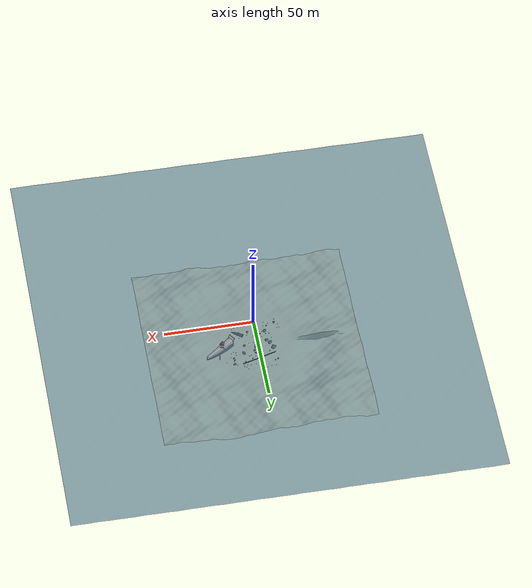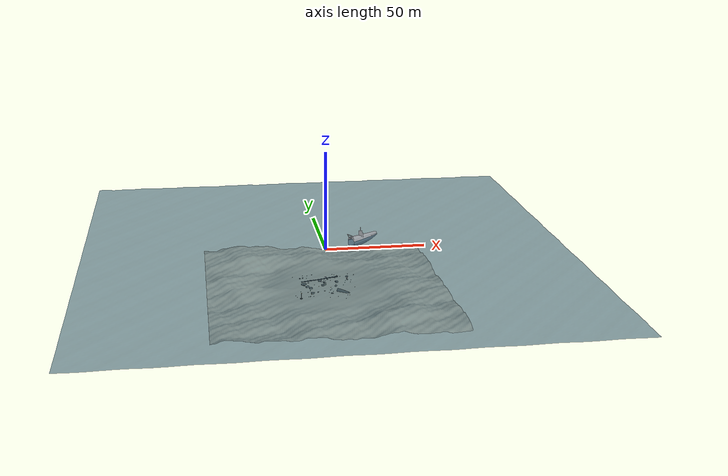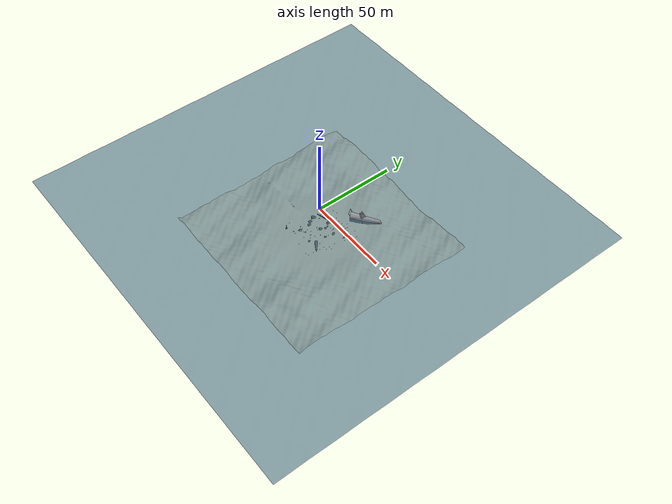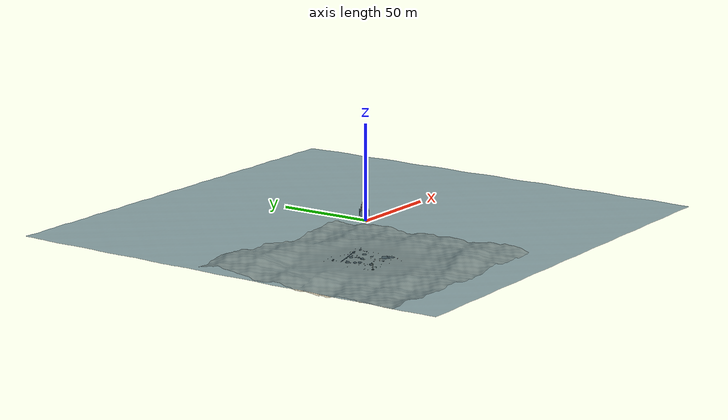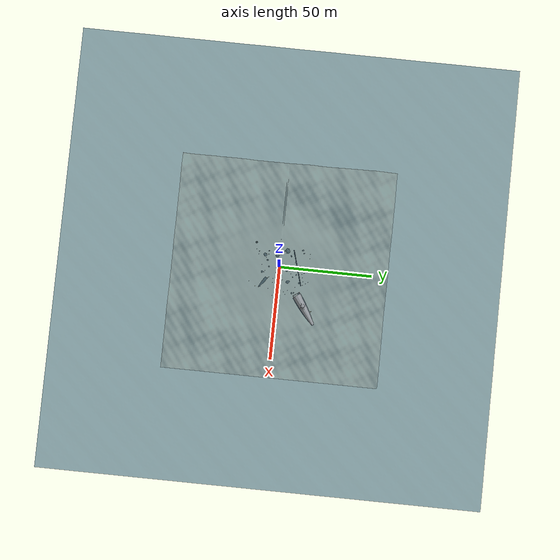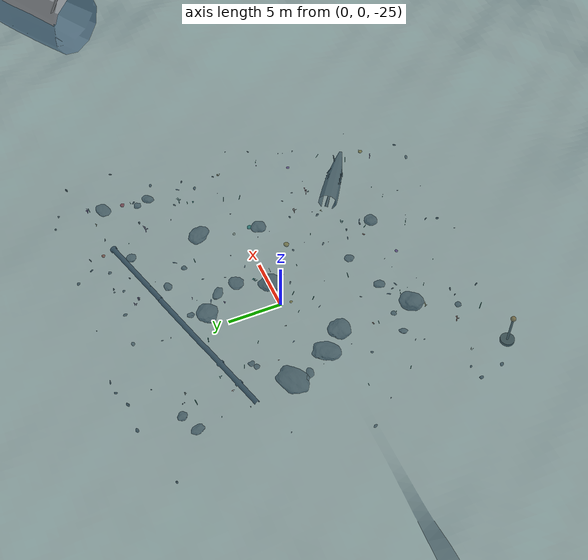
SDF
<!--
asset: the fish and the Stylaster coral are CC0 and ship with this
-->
<sdf version="1.9">
 <world name="mode_aware_survey">
  <physics name="8ms" type="dart">
   <max_step_size>0.008</max_step_size>
   <real_time_factor>1.0</real_time_factor>
  </physics>
  <plugin filename="gz-sim-physics-system" name="gz::sim::systems::Physics"/>
  <plugin filename="gz-sim-user-commands-system" name="gz::sim::systems::UserCommands"/>
  <plugin filename="gz-sim-scene-broadcaster-system" name="gz::sim::systems::SceneBroadcaster"/>
  <plugin filename="gz-sim-sensors-system" name="gz::sim::systems::Sensors">
   <render_engine>ogre2</render_engine>
  </plugin>
  <plugin filename="gz-sim-imu-system" name="gz::sim::systems::Imu"/>
  <scene>
   <ambient>0.34 0.36 0.36 1</ambient>
   <background>0.05 0.16 0.22 1</background>
   <shadows>true</shadows>
   <grid>false</grid>
   <origin_visual>false</origin_visual>
   <fog><color>0.03 0.10 0.12 1</color><type>exp2</type><density>0.075</density></fog>
  </scene>
  <light type="directional" name="filtered_daylight">
   <pose>0 0 12 0 0 0</pose>
   <diffuse>0.72 0.76 0.74 1</diffuse>
   <specular>0.22 0.24 0.24 1</specular>
   <attenuation>
    <range>120</range>
    <constant>0.6</constant>
    <linear>0.02</linear>
    <quadratic>0.001</quadratic>
   </attenuation>
   <direction>0.15 0.2 -0.97</direction>
  </light>
  <light type="point" name="water_column_fill">
   <pose>0 0 -6 0 0 0</pose>
   <diffuse>0.20 0.28 0.30 1</diffuse>
   <specular>0.0 0.0 0.0 1</specular>
   <attenuation>
    <range>60</range>
    <constant>0.5</constant>
    <linear>0.03</linear>
    <quadratic>0.002</quadratic>
   </attenuation>
   <cast_shadows>false</cast_shadows>
  </light>
  <model name="seabed">
   <static>true</static>
   <pose>0 0 -20 0 0 0</pose>
   <link name="link">
    <collision name="collision">
     <geometry><mesh><uri>model://uuv_mode_aware_navigation/models/meshes/seabed.obj</uri></mesh></geometry>
    </collision>
    <visual name="visual">
     <geometry><mesh><uri>model://uuv_mode_aware_navigation/models/meshes/seabed.obj</uri></mesh></geometry>
     <material>
      <ambient>0.42 0.38 0.30 1</ambient>
      <diffuse>1.0 0.95 0.82 1</diffuse>
      <specular>0.05 0.05 0.04 1</specular>
      <pbr>
       <metal>
        <albedo_map>model://uuv_mode_aware_navigation/models/textures/sand_albedo.png</albedo_map>
        <normal_map>model://uuv_mode_aware_navigation/models/textures/sand_normal.png</normal_map>
        <roughness_map>model://uuv_mode_aware_navigation/models/textures/sand_roughness.png</roughness_map>
        <metalness>0.0</metalness>
       </metal>
      </pbr>
     </material>
    </visual>
   </link>
  </model>
  <model name="boulder_field">
   <static>true</static>
   <link name="link">
    <visual name="bo0">
     <pose>-1.24 1.55 -19.65 0 0 3.21</pose>
     <geometry>
      <mesh>
       <uri>model://uuv_mode_aware_navigation/models/meshes/rock_0.obj</uri>
       <scale>0.91 0.92 0.78</scale>
      </mesh>
     </geometry>
     <material>
      <ambient>0.07 0.08 0.07 1</ambient>
      <diffuse>0.46 0.44 0.38 1</diffuse>
      <specular>0.05 0.05 0.05 1</specular>
      <pbr>
       <metal>
        <albedo_map>model://uuv_mode_aware_navigation/models/textures/rock_albedo.png</albedo_map>
        <normal_map>model://uuv_mode_aware_navigation/models/textures/rock_normal.png</normal_map>
        <roughness>0.95</roughness>
        <metalness>0.0</metalness>
       </metal>
      </pbr>
     </material>
    </visual>
    <visual name="bo1">
     <pose>3.38 7.62 -19.88 0 0 0.26</pose>
     <geometry>
      <mesh>
       <uri>model://uuv_mode_aware_navigation/models/meshes/rock_1.obj</uri>
       <scale>0.28 0.25 0.27</scale>
      </mesh>
     </geometry>
     <material>
      <ambient>0.11 0.11 0.10 1</ambient>
      <diffuse>0.46 0.44 0.38 1</diffuse>
      <specular>0.05 0.05 0.05 1</specular>
      <pbr>
       <metal>
        <albedo_map>model://uuv_mode_aware_navigation/models/textures/rock_albedo.png</albedo_map>
        <normal_map>model://uuv_mode_aware_navigation/models/textures/rock_normal.png</normal_map>
        <roughness>0.95</roughness>
        <metalness>0.0</metalness>
       </metal>
      </pbr>
     </material>
    </visual>
    <visual name="bo2">
     <pose>12.54 12.08 -19.78 0 0 0.37</pose>
     <geometry>
      <mesh>
       <uri>model://uuv_mode_aware_navigation/models/meshes/rock_2.obj</uri>
       <scale>0.74 0.63 0.49</scale>
      </mesh>
     </geometry>
     <material>
      <ambient>0.10 0.10 0.09 1</ambient>
      <diffuse>0.46 0.44 0.38 1</diffuse>
      <specular>0.05 0.05 0.05 1</specular>
      <pbr>
       <metal>
        <albedo_map>model://uuv_mode_aware_navigation/models/textures/rock_albedo.png</albedo_map>
        <normal_map>model://uuv_mode_aware_navigation/models/textures/rock_normal.png</normal_map>
        <roughness>0.95</roughness>
        <metalness>0.0</metalness>
       </metal>
      </pbr>
     </material>
    </visual>
    <visual name="bo3">
     <pose>-8.05 -6.71 -19.90 0 0 4.02</pose>
     <geometry>
      <mesh>
       <uri>model://uuv_mode_aware_navigation/models/meshes/rock_3.obj</uri>
       <scale>0.24 0.24 0.23</scale>
      </mesh>
     </geometry>
     <material>
      <ambient>0.10 0.10 0.09 1</ambient>
      <diffuse>0.46 0.44 0.38 1</diffuse>
      <specular>0.05 0.05 0.05 1</specular>
      <pbr>
       <metal>
        <albedo_map>model://uuv_mode_aware_navigation/models/textures/rock_albedo.png</albedo_map>
        <normal_map>model://uuv_mode_aware_navigation/models/textures/rock_normal.png</normal_map>
        <roughness>0.95</roughness>
        <metalness>0.0</metalness>
       </metal>
      </pbr>
     </material>
    </visual>
    <visual name="bo4">
     <pose>-0.01 4.22 -19.75 0 0 4.45</pose>
     <geometry>
      <mesh>
       <uri>model://uuv_mode_aware_navigation/models/meshes/rock_4.obj</uri>
       <scale>0.52 0.66 0.55</scale>
      </mesh>
     </geometry>
     <material>
      <ambient>0.12 0.12 0.11 1</ambient>
      <diffuse>0.46 0.44 0.38 1</diffuse>
      <specular>0.05 0.05 0.05 1</specular>
      <pbr>
       <metal>
        <albedo_map>model://uuv_mode_aware_navigation/models/textures/rock_albedo.png</albedo_map>
        <normal_map>model://uuv_mode_aware_navigation/models/textures/rock_normal.png</normal_map>
        <roughness>0.95</roughness>
        <metalness>0.0</metalness>
       </metal>
      </pbr>
     </material>
    </visual>
    <visual name="bo5">
     <pose>-4.80 -7.03 -19.84 0 0 2.43</pose>
     <geometry>
      <mesh>
       <uri>model://uuv_mode_aware_navigation/models/meshes/rock_5.obj</uri>
       <scale>0.38 0.48 0.35</scale>
      </mesh>
     </geometry>
     <material>
      <ambient>0.12 0.12 0.11 1</ambient>
      <diffuse>0.46 0.44 0.38 1</diffuse>
      <specular>0.05 0.05 0.05 1</specular>
      <pbr>
       <metal>
        <albedo_map>model://uuv_mode_aware_navigation/models/textures/rock_albedo.png</albedo_map>
        <normal_map>model://uuv_mode_aware_navigation/models/textures/rock_normal.png</normal_map>
        <roughness>0.95</roughness>
        <metalness>0.0</metalness>
       </metal>
      </pbr>
     </material>
    </visual>
    <visual name="bo6">
     <pose>11.91 9.03 -19.92 0 0 2.50</pose>
     <geometry>
      <mesh>
       <uri>model://uuv_mode_aware_navigation/models/meshes/rock_6.obj</uri>
       <scale>0.3076 0.3076 0.3076</scale>
      </mesh>
     </geometry>
     <material>
      <ambient>0.12 0.13 0.12 1</ambient>
      <diffuse>0.46 0.44 0.38 1</diffuse>
      <specular>0.05 0.05 0.05 1</specular>
      <pbr>
       <metal>
        <albedo_map>model://uuv_mode_aware_navigation/models/textures/rock_albedo.png</albedo_map>
        <normal_map>model://uuv_mode_aware_navigation/models/textures/rock_normal.png</normal_map>
        <roughness>0.95</roughness>
        <metalness>0.0</metalness>
       </metal>
      </pbr>
     </material>
    </visual>
    <visual name="bo7">
     <pose>-11.10 3.37 -19.72 0 0 4.76</pose>
     <geometry>
      <mesh>
       <uri>model://uuv_mode_aware_navigation/models/meshes/rock_7.obj</uri>
       <scale>0.74 0.69 0.63</scale>
      </mesh>
     </geometry>
     <material>
      <ambient>0.12 0.13 0.12 1</ambient>
      <diffuse>0.46 0.44 0.38 1</diffuse>
      <specular>0.05 0.05 0.05 1</specular>
      <pbr>
       <metal>
        <albedo_map>model://uuv_mode_aware_navigation/models/textures/rock_albedo.png</albedo_map>
        <normal_map>model://uuv_mode_aware_navigation/models/textures/rock_normal.png</normal_map>
        <roughness>0.95</roughness>
        <metalness>0.0</metalness>
       </metal>
      </pbr>
     </material>
    </visual>
    <visual name="bo8">
     <pose>-9.93 -6.59 -19.90 0 0 2.81</pose>
     <geometry>
      <mesh>
       <uri>model://uuv_mode_aware_navigation/models/meshes/rock_0.obj</uri>
       <scale>0.26 0.33 0.22</scale>
      </mesh>
     </geometry>
     <material>
      <ambient>0.10 0.10 0.09 1</ambient>
      <diffuse>0.46 0.44 0.38 1</diffuse>
      <specular>0.05 0.05 0.05 1</specular>
      <pbr>
       <metal>
        <albedo_map>model://uuv_mode_aware_navigation/models/textures/rock_albedo.png</albedo_map>
        <normal_map>model://uuv_mode_aware_navigation/models/textures/rock_normal.png</normal_map>
        <roughness>0.95</roughness>
        <metalness>0.0</metalness>
       </metal>
      </pbr>
     </material>
    </visual>
    <visual name="bo9">
     <pose>-8.04 6.03 -19.88 0 0 1.69</pose>
     <geometry>
      <mesh>
       <uri>model://uuv_mode_aware_navigation/models/meshes/rock_1.obj</uri>
       <scale>0.34 0.28 0.26</scale>
      </mesh>
     </geometry>
     <material>
      <ambient>0.08 0.08 0.07 1</ambient>
      <diffuse>0.46 0.44 0.38 1</diffuse>
      <specular>0.05 0.05 0.05 1</specular>
      <pbr>
       <metal>
        <albedo_map>model://uuv_mode_aware_navigation/models/textures/rock_albedo.png</albedo_map>
        <normal_map>model://uuv_mode_aware_navigation/models/textures/rock_normal.png</normal_map>
        <roughness>0.95</roughness>
        <metalness>0.0</metalness>
       </metal>
      </pbr>
     </material>
    </visual>
    <visual name="bo10">
     <pose>12.24 7.89 -19.84 0 0 4.03</pose>
     <geometry>
      <mesh>
       <uri>model://uuv_mode_aware_navigation/models/meshes/rock_2.obj</uri>
       <scale>0.51 0.41 0.36</scale>
      </mesh>
     </geometry>
     <material>
      <ambient>0.12 0.12 0.11 1</ambient>
      <diffuse>0.46 0.44 0.38 1</diffuse>
      <specular>0.05 0.05 0.05 1</specular>
      <pbr>
       <metal>
        <albedo_map>model://uuv_mode_aware_navigation/models/textures/rock_albedo.png</albedo_map>
        <normal_map>model://uuv_mode_aware_navigation/models/textures/rock_normal.png</normal_map>
        <roughness>0.95</roughness>
        <metalness>0.0</metalness>
       </metal>
      </pbr>
     </material>
    </visual>
    <visual name="bo11">
     <pose>-10.39 12.72 -19.86 0 0 0.46</pose>
     <geometry>
      <mesh>
       <uri>model://uuv_mode_aware_navigation/models/meshes/rock_3.obj</uri>
       <scale>0.35 0.42 0.30</scale>
      </mesh>
     </geometry>
     <material>
      <ambient>0.08 0.09 0.08 1</ambient>
      <diffuse>0.46 0.44 0.38 1</diffuse>
      <specular>0.05 0.05 0.05 1</specular>
      <pbr>
       <metal>
        <albedo_map>model://uuv_mode_aware_navigation/models/textures/rock_albedo.png</albedo_map>
        <normal_map>model://uuv_mode_aware_navigation/models/textures/rock_normal.png</normal_map>
        <roughness>0.95</roughness>
        <metalness>0.0</metalness>
       </metal>
      </pbr>
     </material>
    </visual>
    <visual name="bo12">
     <pose>-10.66 2.15 -19.85 0 0 3.04</pose>
     <geometry>
      <mesh>
       <uri>model://uuv_mode_aware_navigation/models/meshes/rock_4.obj</uri>
       <scale>0.42 0.39 0.33</scale>
      </mesh>
     </geometry>
     <material>
      <ambient>0.12 0.13 0.12 1</ambient>
      <diffuse>0.46 0.44 0.38 1</diffuse>
      <specular>0.05 0.05 0.05 1</specular>
      <pbr>
       <metal>
        <albedo_map>model://uuv_mode_aware_navigation/models/textures/rock_albedo.png</albedo_map>
        <normal_map>model://uuv_mode_aware_navigation/models/textures/rock_normal.png</normal_map>
        <roughness>0.95</roughness>
        <metalness>0.0</metalness>
       </metal>
      </pbr>
     </material>
    </visual>
    <visual name="bo13">
     <pose>1.94 9.53 -19.85 0 0 1.19</pose>
     <geometry>
      <mesh>
       <uri>model://uuv_mode_aware_navigation/models/meshes/rock_5.obj</uri>
       <scale>0.32 0.41 0.33</scale>
      </mesh>
     </geometry>
     <material>
      <ambient>0.08 0.08 0.07 1</ambient>
      <diffuse>0.46 0.44 0.38 1</diffuse>
      <specular>0.05 0.05 0.05 1</specular>
      <pbr>
       <metal>
        <albedo_map>model://uuv_mode_aware_navigation/models/textures/rock_albedo.png</albedo_map>
        <normal_map>model://uuv_mode_aware_navigation/models/textures/rock_normal.png</normal_map>
        <roughness>0.95</roughness>
        <metalness>0.0</metalness>
       </metal>
      </pbr>
     </material>
    </visual>
    <visual name="bo14">
     <pose>6.23 11.45 -19.86 0 0 0.65</pose>
     <geometry>
      <mesh>
       <uri>model://uuv_mode_aware_navigation/models/meshes/rock_6.obj</uri>
       <scale>0.43 0.42 0.32</scale>
      </mesh>
     </geometry>
     <material>
      <ambient>0.09 0.09 0.08 1</ambient>
      <diffuse>0.46 0.44 0.38 1</diffuse>
      <specular>0.05 0.05 0.05 1</specular>
      <pbr>
       <metal>
        <albedo_map>model://uuv_mode_aware_navigation/models/textures/rock_albedo.png</albedo_map>
        <normal_map>model://uuv_mode_aware_navigation/models/textures/rock_normal.png</normal_map>
        <roughness>0.95</roughness>
        <metalness>0.0</metalness>
       </metal>
      </pbr>
     </material>
    </visual>
    <visual name="bo15">
     <pose>-11.99 12.03 -19.83 0 0 1.84</pose>
     <geometry>
      <mesh>
       <uri>model://uuv_mode_aware_navigation/models/meshes/rock_7.obj</uri>
       <scale>0.43 0.37 0.37</scale>
      </mesh>
     </geometry>
     <material>
      <ambient>0.10 0.11 0.09 1</ambient>
      <diffuse>0.46 0.44 0.38 1</diffuse>
      <specular>0.05 0.05 0.05 1</specular>
      <pbr>
       <metal>
        <albedo_map>model://uuv_mode_aware_navigation/models/textures/rock_albedo.png</albedo_map>
        <normal_map>model://uuv_mode_aware_navigation/models/textures/rock_normal.png</normal_map>
        <roughness>0.95</roughness>
        <metalness>0.0</metalness>
       </metal>
      </pbr>
     </material>
    </visual>
    <visual name="bo16">
     <pose>-8.44 5.73 -19.88 0 0 1.76</pose>
     <geometry>
      <mesh>
       <uri>model://uuv_mode_aware_navigation/models/meshes/rock_0.obj</uri>
       <scale>0.25 0.28 0.26</scale>
      </mesh>
     </geometry>
     <material>
      <ambient>0.10 0.11 0.09 1</ambient>
      <diffuse>0.46 0.44 0.38 1</diffuse>
      <specular>0.05 0.05 0.05 1</specular>
      <pbr>
       <metal>
        <albedo_map>model://uuv_mode_aware_navigation/models/textures/rock_albedo.png</albedo_map>
        <normal_map>model://uuv_mode_aware_navigation/models/textures/rock_normal.png</normal_map>
        <roughness>0.95</roughness>
        <metalness>0.0</metalness>
       </metal>
      </pbr>
     </material>
    </visual>
    <visual name="bo17">
     <pose>10.85 -7.70 -19.92 0 0 2.32</pose>
     <geometry>
      <mesh>
       <uri>model://uuv_mode_aware_navigation/models/meshes/rock_1.obj</uri>
       <scale>0.22 0.23 0.17</scale>
      </mesh>
     </geometry>
     <material>
      <ambient>0.07 0.08 0.07 1</ambient>
      <diffuse>0.46 0.44 0.38 1</diffuse>
      <specular>0.05 0.05 0.05 1</specular>
      <pbr>
       <metal>
        <albedo_map>model://uuv_mode_aware_navigation/models/textures/rock_albedo.png</albedo_map>
        <normal_map>model://uuv_mode_aware_navigation/models/textures/rock_normal.png</normal_map>
        <roughness>0.95</roughness>
        <metalness>0.0</metalness>
       </metal>
      </pbr>
     </material>
    </visual>
    <visual name="bo18">
     <pose>1.88 -9.58 -19.80 0 0 3.67</pose>
     <geometry>
      <mesh>
       <uri>model://uuv_mode_aware_navigation/models/meshes/rock_2.obj</uri>
       <scale>0.56 0.58 0.43</scale>
      </mesh>
     </geometry>
     <material>
      <ambient>0.11 0.11 0.10 1</ambient>
      <diffuse>0.46 0.44 0.38 1</diffuse>
      <specular>0.05 0.05 0.05 1</specular>
      <pbr>
       <metal>
        <albedo_map>model://uuv_mode_aware_navigation/models/textures/rock_albedo.png</albedo_map>
        <normal_map>model://uuv_mode_aware_navigation/models/textures/rock_normal.png</normal_map>
        <roughness>0.95</roughness>
        <metalness>0.0</metalness>
       </metal>
      </pbr>
     </material>
    </visual>
    <visual name="bo19">
     <pose>-9.35 -12.09 -19.90 0 0 4.00</pose>
     <geometry>
      <mesh>
       <uri>model://uuv_mode_aware_navigation/models/meshes/rock_3.obj</uri>
       <scale>0.27 0.26 0.23</scale>
      </mesh>
     </geometry>
     <material>
      <ambient>0.06 0.07 0.06 1</ambient>
      <diffuse>0.46 0.44 0.38 1</diffuse>
      <specular>0.05 0.05 0.05 1</specular>
      <pbr>
       <metal>
        <albedo_map>model://uuv_mode_aware_navigation/models/textures/rock_albedo.png</albedo_map>
        <normal_map>model://uuv_mode_aware_navigation/models/textures/rock_normal.png</normal_map>
        <roughness>0.95</roughness>
        <metalness>0.0</metalness>
       </metal>
      </pbr>
     </material>
    </visual>
    <visual name="bo20">
     <pose>-0.46 5.99 -19.82 0 0 5.65</pose>
     <geometry>
      <mesh>
       <uri>model://uuv_mode_aware_navigation/models/meshes/rock_4.obj</uri>
       <scale>0.54 0.40 0.39</scale>
      </mesh>
     </geometry>
     <material>
      <ambient>0.11 0.11 0.10 1</ambient>
      <diffuse>0.46 0.44 0.38 1</diffuse>
      <specular>0.05 0.05 0.05 1</specular>
      <pbr>
       <metal>
        <albedo_map>model://uuv_mode_aware_navigation/models/textures/rock_albedo.png</albedo_map>
        <normal_map>model://uuv_mode_aware_navigation/models/textures/rock_normal.png</normal_map>
        <roughness>0.95</roughness>
        <metalness>0.0</metalness>
       </metal>
      </pbr>
     </material>
    </visual>
    <visual name="bo21">
     <pose>6.16 5.30 -19.67 0 0 5.47</pose>
     <geometry>
      <mesh>
       <uri>model://uuv_mode_aware_navigation/models/meshes/rock_5.obj</uri>
       <scale>0.94 0.78 0.72</scale>
      </mesh>
     </geometry>
     <material>
      <ambient>0.12 0.13 0.11 1</ambient>
      <diffuse>0.46 0.44 0.38 1</diffuse>
      <specular>0.05 0.05 0.05 1</specular>
      <pbr>
       <metal>
        <albedo_map>model://uuv_mode_aware_navigation/models/textures/rock_albedo.png</albedo_map>
        <normal_map>model://uuv_mode_aware_navigation/models/textures/rock_normal.png</normal_map>
        <roughness>0.95</roughness>
        <metalness>0.0</metalness>
       </metal>
      </pbr>
     </material>
    </visual>
    <visual name="bo22">
     <pose>-2.15 7.55 -19.69 0 0 3.82</pose>
     <geometry>
      <mesh>
       <uri>model://uuv_mode_aware_navigation/models/meshes/rock_6.obj</uri>
       <scale>0.89 0.91 0.69</scale>
      </mesh>
     </geometry>
     <material>
      <ambient>0.10 0.10 0.09 1</ambient>
      <diffuse>0.46 0.44 0.38 1</diffuse>
      <specular>0.05 0.05 0.05 1</specular>
      <pbr>
       <metal>
        <albedo_map>model://uuv_mode_aware_navigation/models/textures/rock_albedo.png</albedo_map>
        <normal_map>model://uuv_mode_aware_navigation/models/textures/rock_normal.png</normal_map>
        <roughness>0.95</roughness>
        <metalness>0.0</metalness>
       </metal>
      </pbr>
     </material>
    </visual>
    <visual name="bo23">
     <pose>-10.91 3.62 -19.65 0 0 3.65</pose>
     <geometry>
      <mesh>
       <uri>model://uuv_mode_aware_navigation/models/meshes/rock_7.obj</uri>
       <scale>1.09 1.04 0.77</scale>
      </mesh>
     </geometry>
     <material>
      <ambient>0.11 0.11 0.10 1</ambient>
      <diffuse>0.46 0.44 0.38 1</diffuse>
      <specular>0.05 0.05 0.05 1</specular>
      <pbr>
       <metal>
        <albedo_map>model://uuv_mode_aware_navigation/models/textures/rock_albedo.png</albedo_map>
        <normal_map>model://uuv_mode_aware_navigation/models/textures/rock_normal.png</normal_map>
        <roughness>0.95</roughness>
        <metalness>0.0</metalness>
       </metal>
      </pbr>
     </material>
    </visual>
    <visual name="bo24">
     <pose>-1.55 8.80 -19.89 0 0 1.45</pose>
     <geometry>
      <mesh>
       <uri>model://uuv_mode_aware_navigation/models/meshes/rock_0.obj</uri>
       <scale>0.31 0.24 0.25</scale>
      </mesh>
     </geometry>
     <material>
      <ambient>0.09 0.10 0.09 1</ambient>
      <diffuse>0.46 0.44 0.38 1</diffuse>
      <specular>0.05 0.05 0.05 1</specular>
      <pbr>
       <metal>
        <albedo_map>model://uuv_mode_aware_navigation/models/textures/rock_albedo.png</albedo_map>
        <normal_map>model://uuv_mode_aware_navigation/models/textures/rock_normal.png</normal_map>
        <roughness>0.95</roughness>
        <metalness>0.0</metalness>
       </metal>
      </pbr>
     </material>
    </visual>
    <visual name="bo25">
     <pose>5.16 -0.07 -19.79 0 0 4.26</pose>
     <geometry>
      <mesh>
       <uri>model://uuv_mode_aware_navigation/models/meshes/rock_1.obj</uri>
       <scale>0.78 0.63 0.47</scale>
      </mesh>
     </geometry>
     <material>
      <ambient>0.08 0.09 0.08 1</ambient>
      <diffuse>0.46 0.44 0.38 1</diffuse>
      <specular>0.05 0.05 0.05 1</specular>
      <pbr>
       <metal>
        <albedo_map>model://uuv_mode_aware_navigation/models/textures/rock_albedo.png</albedo_map>
        <normal_map>model://uuv_mode_aware_navigation/models/textures/rock_normal.png</normal_map>
        <roughness>0.95</roughness>
        <metalness>0.0</metalness>
       </metal>
      </pbr>
     </material>
    </visual>
    <visual name="bo26">
     <pose>-7.73 -8.59 -19.62 0 0 4.18</pose>
     <geometry>
      <mesh>
       <uri>model://uuv_mode_aware_navigation/models/meshes/rock_2.obj</uri>
       <scale>0.95 0.89 0.85</scale>
      </mesh>
     </geometry>
     <material>
      <ambient>0.08 0.09 0.08 1</ambient>
      <diffuse>0.46 0.44 0.38 1</diffuse>
      <specular>0.05 0.05 0.05 1</specular>
      <pbr>
       <metal>
        <albedo_map>model://uuv_mode_aware_navigation/models/textures/rock_albedo.png</albedo_map>
        <normal_map>model://uuv_mode_aware_navigation/models/textures/rock_normal.png</normal_map>
        <roughness>0.95</roughness>
        <metalness>0.0</metalness>
       </metal>
      </pbr>
     </material>
    </visual>
    <visual name="bo27">
     <pose>-7.84 -1.80 -19.70 0 0 1.99</pose>
     <geometry>
      <mesh>
       <uri>model://uuv_mode_aware_navigation/models/meshes/rock_3.obj</uri>
       <scale>0.95 0.94 0.66</scale>
      </mesh>
     </geometry>
     <material>
      <ambient>0.10 0.10 0.09 1</ambient>
      <diffuse>0.46 0.44 0.38 1</diffuse>
      <specular>0.05 0.05 0.05 1</specular>
      <pbr>
       <metal>
        <albedo_map>model://uuv_mode_aware_navigation/models/textures/rock_albedo.png</albedo_map>
        <normal_map>model://uuv_mode_aware_navigation/models/textures/rock_normal.png</normal_map>
        <roughness>0.95</roughness>
        <metalness>0.0</metalness>
       </metal>
      </pbr>
     </material>
    </visual>
    <visual name="bo28">
     <pose>-9.46 -0.09 -19.63 0 0 1.06</pose>
     <geometry>
      <mesh>
       <uri>model://uuv_mode_aware_navigation/models/meshes/rock_4.obj</uri>
       <scale>0.95 0.91 0.82</scale>
      </mesh>
     </geometry>
     <material>
      <ambient>0.08 0.08 0.08 1</ambient>
      <diffuse>0.46 0.44 0.38 1</diffuse>
      <specular>0.05 0.05 0.05 1</specular>
      <pbr>
       <metal>
        <albedo_map>model://uuv_mode_aware_navigation/models/textures/rock_albedo.png</albedo_map>
        <normal_map>model://uuv_mode_aware_navigation/models/textures/rock_normal.png</normal_map>
        <roughness>0.95</roughness>
        <metalness>0.0</metalness>
       </metal>
      </pbr>
     </material>
    </visual>
    <visual name="bo29">
     <pose>-1.28 -5.85 -19.86 0 0 5.27</pose>
     <geometry>
      <mesh>
       <uri>model://uuv_mode_aware_navigation/models/meshes/rock_5.obj</uri>
       <scale>0.37 0.40 0.32</scale>
      </mesh>
     </geometry>
     <material>
      <ambient>0.08 0.09 0.08 1</ambient>
      <diffuse>0.46 0.44 0.38 1</diffuse>
      <specular>0.05 0.05 0.05 1</specular>
      <pbr>
       <metal>
        <albedo_map>model://uuv_mode_aware_navigation/models/textures/rock_albedo.png</albedo_map>
        <normal_map>model://uuv_mode_aware_navigation/models/textures/rock_normal.png</normal_map>
        <roughness>0.95</roughness>
        <metalness>0.0</metalness>
       </metal>
      </pbr>
     </material>
    </visual>
   </link>
  </model>
  <model name="growth">
   <static>true</static>
   <link name="link">
    <visual name="g0">
     <pose>-4.69 8.42 -19.63 -0.06 -0.06 0</pose>
     <geometry><cylinder><radius>0.029</radius><length>0.74</length></cylinder></geometry>
     <material><ambient>0.03 0.09 0.05 1</ambient><diffuse>0.18 0.52 0.26 1</diffuse></material>
    </visual>
    <visual name="g1">
     <pose>-9.77 11.34 -19.67 -0.21 0.20 0</pose>
     <geometry><cylinder><radius>0.030</radius><length>0.65</length></cylinder></geometry>
     <material><ambient>0.03 0.09 0.05 1</ambient><diffuse>0.18 0.52 0.26 1</diffuse></material>
    </visual>
    <visual name="g2">
     <pose>-10.33 -13.60 -19.63 0.09 0.02 0</pose>
     <geometry><cylinder><radius>0.029</radius><length>0.74</length></cylinder></geometry>
     <material><ambient>0.03 0.09 0.05 1</ambient><diffuse>0.18 0.52 0.26 1</diffuse></material>
    </visual>
    <visual name="g3">
     <pose>-8.09 -6.95 -19.80 -0.16 0.05 0</pose>
     <geometry><cylinder><radius>0.017</radius><length>0.40</length></cylinder></geometry>
     <material><ambient>0.03 0.09 0.05 1</ambient><diffuse>0.18 0.52 0.26 1</diffuse></material>
    </visual>
    <visual name="g4">
     <pose>-4.09 -1.17 -19.73 0.24 -0.05 0</pose>
     <geometry><cylinder><radius>0.029</radius><length>0.54</length></cylinder></geometry>
     <material><ambient>0.03 0.09 0.05 1</ambient><diffuse>0.18 0.52 0.26 1</diffuse></material>
    </visual>
    <visual name="g5">
     <pose>-13.48 -1.68 -19.83 -0.30 0.18 0</pose>
     <geometry><cylinder><radius>0.015</radius><length>0.34</length></cylinder></geometry>
     <material><ambient>0.03 0.09 0.05 1</ambient><diffuse>0.18 0.52 0.26 1</diffuse></material>
    </visual>
    <visual name="g6">
     <pose>-4.87 0.51 -19.74 0.17 -0.24 0</pose>
     <geometry><cylinder><radius>0.022</radius><length>0.53</length></cylinder></geometry>
     <material><ambient>0.03 0.09 0.05 1</ambient><diffuse>0.18 0.52 0.26 1</diffuse></material>
    </visual>
    <visual name="g7">
     <pose>0.22 1.73 -19.69 0.25 -0.03 0</pose>
     <geometry><cylinder><radius>0.023</radius><length>0.63</length></cylinder></geometry>
     <material><ambient>0.03 0.09 0.05 1</ambient><diffuse>0.18 0.52 0.26 1</diffuse></material>
    </visual>
    <visual name="g8">
     <pose>-1.33 0.93 -19.76 0.26 0.12 0</pose>
     <geometry><cylinder><radius>0.028</radius><length>0.49</length></cylinder></geometry>
     <material><ambient>0.03 0.09 0.05 1</ambient><diffuse>0.18 0.52 0.26 1</diffuse></material>
    </visual>
    <visual name="g9">
     <pose>12.41 9.52 -19.84 -0.23 -0.03 0</pose>
     <geometry><cylinder><radius>0.013</radius><length>0.32</length></cylinder></geometry>
     <material><ambient>0.03 0.09 0.05 1</ambient><diffuse>0.18 0.52 0.26 1</diffuse></material>
    </visual>
    <visual name="g10">
     <pose>7.95 11.12 -19.84 0.13 0.10 0</pose>
     <geometry><cylinder><radius>0.015</radius><length>0.33</length></cylinder></geometry>
     <material><ambient>0.03 0.09 0.05 1</ambient><diffuse>0.18 0.52 0.26 1</diffuse></material>
    </visual>
    <visual name="g11">
     <pose>12.67 -2.85 -19.75 0.29 0.20 0</pose>
     <geometry><cylinder><radius>0.015</radius><length>0.49</length></cylinder></geometry>
     <material><ambient>0.03 0.09 0.05 1</ambient><diffuse>0.18 0.52 0.26 1</diffuse></material>
    </visual>
    <visual name="g12">
     <pose>-8.52 -5.08 -19.69 -0.29 0.03 0</pose>
     <geometry><cylinder><radius>0.020</radius><length>0.61</length></cylinder></geometry>
     <material><ambient>0.03 0.09 0.05 1</ambient><diffuse>0.18 0.52 0.26 1</diffuse></material>
    </visual>
    <visual name="g13">
     <pose>0.34 -12.20 -19.63 0.17 0.28 0</pose>
     <geometry><cylinder><radius>0.014</radius><length>0.74</length></cylinder></geometry>
     <material><ambient>0.03 0.09 0.05 1</ambient><diffuse>0.18 0.52 0.26 1</diffuse></material>
    </visual>
    <visual name="g14">
     <pose>-6.43 -10.37 -19.77 0.25 0.19 0</pose>
     <geometry><cylinder><radius>0.017</radius><length>0.46</length></cylinder></geometry>
     <material><ambient>0.03 0.09 0.05 1</ambient><diffuse>0.18 0.52 0.26 1</diffuse></material>
    </visual>
    <visual name="g15">
     <pose>5.61 -11.50 -19.86 0.11 -0.04 0</pose>
     <geometry><cylinder><radius>0.013</radius><length>0.28</length></cylinder></geometry>
     <material><ambient>0.03 0.09 0.05 1</ambient><diffuse>0.18 0.52 0.26 1</diffuse></material>
    </visual>
    <visual name="g16">
     <pose>-11.66 9.97 -19.86 0.22 -0.03 0</pose>
     <geometry><cylinder><radius>0.018</radius><length>0.28</length></cylinder></geometry>
     <material><ambient>0.03 0.09 0.05 1</ambient><diffuse>0.18 0.52 0.26 1</diffuse></material>
    </visual>
    <visual name="g17">
     <pose>-10.38 0.75 -19.82 -0.23 -0.20 0</pose>
     <geometry><cylinder><radius>0.013</radius><length>0.37</length></cylinder></geometry>
     <material><ambient>0.03 0.09 0.05 1</ambient><diffuse>0.18 0.52 0.26 1</diffuse></material>
    </visual>
    <visual name="g18">
     <pose>7.27 -5.88 -19.75 -0.19 -0.09 0</pose>
     <geometry><cylinder><radius>0.012</radius><length>0.50</length></cylinder></geometry>
     <material><ambient>0.03 0.09 0.05 1</ambient><diffuse>0.18 0.52 0.26 1</diffuse></material>
    </visual>
    <visual name="g19">
     <pose>1.43 -8.70 -19.76 0.26 -0.24 0</pose>
     <geometry><cylinder><radius>0.027</radius><length>0.49</length></cylinder></geometry>
     <material><ambient>0.03 0.09 0.05 1</ambient><diffuse>0.18 0.52 0.26 1</diffuse></material>
    </visual>
    <visual name="g20">
     <pose>-2.99 0.19 -19.70 0.29 -0.09 0</pose>
     <geometry><cylinder><radius>0.027</radius><length>0.59</length></cylinder></geometry>
     <material><ambient>0.03 0.09 0.05 1</ambient><diffuse>0.18 0.52 0.26 1</diffuse></material>
    </visual>
    <visual name="g21">
     <pose>-4.27 -12.48 -19.84 -0.26 0.14 0</pose>
     <geometry><cylinder><radius>0.017</radius><length>0.31</length></cylinder></geometry>
     <material><ambient>0.03 0.09 0.05 1</ambient><diffuse>0.18 0.52 0.26 1</diffuse></material>
    </visual>
    <visual name="g22">
     <pose>10.38 4.78 -19.80 -0.15 -0.12 0</pose>
     <geometry><cylinder><radius>0.020</radius><length>0.39</length></cylinder></geometry>
     <material><ambient>0.03 0.09 0.05 1</ambient><diffuse>0.18 0.52 0.26 1</diffuse></material>
    </visual>
    <visual name="g23">
     <pose>12.93 13.23 -19.74 -0.15 0.28 0</pose>
     <geometry><cylinder><radius>0.018</radius><length>0.52</length></cylinder></geometry>
     <material><ambient>0.03 0.09 0.05 1</ambient><diffuse>0.18 0.52 0.26 1</diffuse></material>
    </visual>
    <visual name="g24">
     <pose>-0.71 0.08 -19.82 0.00 -0.30 0</pose>
     <geometry><cylinder><radius>0.017</radius><length>0.35</length></cylinder></geometry>
     <material><ambient>0.03 0.09 0.05 1</ambient><diffuse>0.18 0.52 0.26 1</diffuse></material>
    </visual>
    <visual name="g25">
     <pose>-13.37 -5.48 -19.82 0.05 0.02 0</pose>
     <geometry><cylinder><radius>0.026</radius><length>0.37</length></cylinder></geometry>
     <material><ambient>0.03 0.09 0.05 1</ambient><diffuse>0.18 0.52 0.26 1</diffuse></material>
    </visual>
    <visual name="g26">
     <pose>-3.09 -4.87 -19.63 -0.21 0.13 0</pose>
     <geometry><cylinder><radius>0.024</radius><length>0.74</length></cylinder></geometry>
     <material><ambient>0.03 0.09 0.05 1</ambient><diffuse>0.18 0.52 0.26 1</diffuse></material>
    </visual>
    <visual name="g27">
     <pose>3.57 6.55 -19.67 -0.22 0.01 0</pose>
     <geometry><cylinder><radius>0.021</radius><length>0.66</length></cylinder></geometry>
     <material><ambient>0.03 0.09 0.05 1</ambient><diffuse>0.18 0.52 0.26 1</diffuse></material>
    </visual>
    <visual name="g28">
     <pose>2.35 11.00 -19.70 0.12 -0.16 0</pose>
     <geometry><cylinder><radius>0.013</radius><length>0.59</length></cylinder></geometry>
     <material><ambient>0.03 0.09 0.05 1</ambient><diffuse>0.18 0.52 0.26 1</diffuse></material>
    </visual>
    <visual name="g29">
     <pose>9.40 1.64 -19.72 0.08 0.11 0</pose>
     <geometry><cylinder><radius>0.021</radius><length>0.56</length></cylinder></geometry>
     <material><ambient>0.03 0.09 0.05 1</ambient><diffuse>0.18 0.52 0.26 1</diffuse></material>
    </visual>
    <visual name="g30">
     <pose>0.08 0.99 -19.71 -0.26 0.14 0</pose>
     <geometry><cylinder><radius>0.017</radius><length>0.58</length></cylinder></geometry>
     <material><ambient>0.03 0.09 0.05 1</ambient><diffuse>0.18 0.52 0.26 1</diffuse></material>
    </visual>
    <visual name="g31">
     <pose>-8.25 6.72 -19.63 -0.00 -0.07 0</pose>
     <geometry><cylinder><radius>0.021</radius><length>0.74</length></cylinder></geometry>
     <material><ambient>0.03 0.09 0.05 1</ambient><diffuse>0.18 0.52 0.26 1</diffuse></material>
    </visual>
    <visual name="g32">
     <pose>4.00 -11.83 -19.84 -0.15 0.15 0</pose>
     <geometry><cylinder><radius>0.017</radius><length>0.32</length></cylinder></geometry>
     <material><ambient>0.03 0.09 0.05 1</ambient><diffuse>0.18 0.52 0.26 1</diffuse></material>
    </visual>
    <visual name="g33">
     <pose>-6.47 4.82 -19.70 0.11 -0.13 0</pose>
     <geometry><cylinder><radius>0.021</radius><length>0.60</length></cylinder></geometry>
     <material><ambient>0.03 0.09 0.05 1</ambient><diffuse>0.18 0.52 0.26 1</diffuse></material>
    </visual>
    <visual name="g34">
     <pose>11.02 -8.42 -19.63 0.26 -0.29 0</pose>
     <geometry><cylinder><radius>0.020</radius><length>0.74</length></cylinder></geometry>
     <material><ambient>0.03 0.09 0.05 1</ambient><diffuse>0.18 0.52 0.26 1</diffuse></material>
    </visual>
    <visual name="g35">
     <pose>-6.48 -8.12 -19.64 -0.17 0.05 0</pose>
     <geometry><cylinder><radius>0.015</radius><length>0.72</length></cylinder></geometry>
     <material><ambient>0.03 0.09 0.05 1</ambient><diffuse>0.18 0.52 0.26 1</diffuse></material>
    </visual>
    <visual name="g36">
     <pose>8.97 0.24 -19.65 0.12 -0.16 0</pose>
     <geometry><cylinder><radius>0.028</radius><length>0.69</length></cylinder></geometry>
     <material><ambient>0.03 0.09 0.05 1</ambient><diffuse>0.18 0.52 0.26 1</diffuse></material>
    </visual>
    <visual name="g37">
     <pose>-0.23 -1.38 -19.80 -0.22 -0.09 0</pose>
     <geometry><cylinder><radius>0.018</radius><length>0.40</length></cylinder></geometry>
     <material><ambient>0.03 0.09 0.05 1</ambient><diffuse>0.18 0.52 0.26 1</diffuse></material>
    </visual>
    <visual name="g38">
     <pose>9.50 -10.64 -19.64 0.13 0.24 0</pose>
     <geometry><cylinder><radius>0.017</radius><length>0.71</length></cylinder></geometry>
     <material><ambient>0.03 0.09 0.05 1</ambient><diffuse>0.18 0.52 0.26 1</diffuse></material>
    </visual>
    <visual name="g39">
     <pose>2.50 -3.90 -19.77 -0.13 -0.27 0</pose>
     <geometry><cylinder><radius>0.014</radius><length>0.46</length></cylinder></geometry>
     <material><ambient>0.03 0.09 0.05 1</ambient><diffuse>0.18 0.52 0.26 1</diffuse></material>
    </visual>
   </link>
  </model>
  <model name="reef">
   <static>true</static>
   <link name="link">
    <visual name="coral_staghorn_0_0">
     <pose>-13.66 -10.85 -20.00 0 0 0.27</pose>
     <geometry>
      <mesh>
       <uri>model://uuv_mode_aware_navigation/models/meshes/coral_staghorn_0.obj</uri>
       <scale>0.84 0.84 0.84</scale>
      </mesh>
     </geometry>
     <material>
      <ambient>0.14 0.12 0.09 1</ambient>
      <diffuse>0.74 0.66 0.48 1</diffuse>
      <specular>0.08 0.08 0.08 1</specular>
      <pbr><metal><roughness>0.92</roughness><metalness>0.0</metalness></metal></pbr>
      <pbr>
       <metal>
        <albedo_map>model://uuv_mode_aware_navigation/models/textures/coral_albedo.png</albedo_map>
        <normal_map>model://uuv_mode_aware_navigation/models/textures/coral_normal.png</normal_map>
        <roughness>0.9</roughness>
        <metalness>0.0</metalness>
       </metal>
      </pbr>
     </material>
    </visual>
    <visual name="coral_staghorn_0_1">
     <pose>12.61 0.99 -20.00 0 0 0.93</pose>
     <geometry>
      <mesh>
       <uri>model://uuv_mode_aware_navigation/models/meshes/coral_staghorn_0.obj</uri>
       <scale>1.08 1.08 1.08</scale>
      </mesh>
     </geometry>
     <material>
      <ambient>0.15 0.11 0.05 1</ambient>
      <diffuse>0.82 0.62 0.16 1</diffuse>
      <specular>0.08 0.08 0.08 1</specular>
      <pbr><metal><roughness>0.92</roughness><metalness>0.0</metalness></metal></pbr>
      <pbr>
       <metal>
        <albedo_map>model://uuv_mode_aware_navigation/models/textures/coral_albedo.png</albedo_map>
        <normal_map>model://uuv_mode_aware_navigation/models/textures/coral_normal.png</normal_map>
        <roughness>0.9</roughness>
        <metalness>0.0</metalness>
       </metal>
      </pbr>
     </material>
    </visual>
    <visual name="coral_staghorn_0_2">
     <pose>6.74 4.54 -20.00 0 0 4.60</pose>
     <geometry>
      <mesh>
       <uri>model://uuv_mode_aware_navigation/models/meshes/coral_staghorn_0.obj</uri>
       <scale>0.65 0.65 0.65</scale>
      </mesh>
     </geometry>
     <material>
      <ambient>0.17 0.07 0.07 1</ambient>
      <diffuse>0.80 0.24 0.20 1</diffuse>
      <specular>0.08 0.08 0.08 1</specular>
      <pbr><metal><roughness>0.92</roughness><metalness>0.0</metalness></metal></pbr>
      <pbr>
       <metal>
        <albedo_map>model://uuv_mode_aware_navigation/models/textures/coral_albedo.png</albedo_map>
        <normal_map>model://uuv_mode_aware_navigation/models/textures/coral_normal.png</normal_map>
        <roughness>0.9</roughness>
        <metalness>0.0</metalness>
       </metal>
      </pbr>
     </material>
    </visual>
    <visual name="coral_staghorn_0_3">
     <pose>0.73 -8.26 -20.00 0 0 0.13</pose>
     <geometry>
      <mesh>
       <uri>model://uuv_mode_aware_navigation/models/meshes/coral_staghorn_0.obj</uri>
       <scale>0.99 0.99 0.99</scale>
      </mesh>
     </geometry>
     <material>
      <ambient>0.16 0.09 0.06 1</ambient>
      <diffuse>0.86 0.38 0.18 1</diffuse>
      <specular>0.08 0.08 0.08 1</specular>
      <pbr><metal><roughness>0.92</roughness><metalness>0.0</metalness></metal></pbr>
      <pbr>
       <metal>
        <albedo_map>model://uuv_mode_aware_navigation/models/textures/coral_albedo.png</albedo_map>
        <normal_map>model://uuv_mode_aware_navigation/models/textures/coral_normal.png</normal_map>
        <roughness>0.9</roughness>
        <metalness>0.0</metalness>
       </metal>
      </pbr>
     </material>
    </visual>
    <visual name="coral_staghorn_0_4">
     <pose>12.31 -2.72 -20.00 0 0 2.46</pose>
     <geometry>
      <mesh>
       <uri>model://uuv_mode_aware_navigation/models/meshes/coral_staghorn_0.obj</uri>
       <scale>0.70 0.70 0.70</scale>
      </mesh>
     </geometry>
     <material>
      <ambient>0.13 0.07 0.11 1</ambient>
      <diffuse>0.62 0.30 0.58 1</diffuse>
      <specular>0.08 0.08 0.08 1</specular>
      <pbr><metal><roughness>0.92</roughness><metalness>0.0</metalness></metal></pbr>
      <pbr>
       <metal>
        <albedo_map>model://uuv_mode_aware_navigation/models/textures/coral_albedo.png</albedo_map>
        <normal_map>model://uuv_mode_aware_navigation/models/textures/coral_normal.png</normal_map>
        <roughness>0.9</roughness>
        <metalness>0.0</metalness>
       </metal>
      </pbr>
     </material>
    </visual>
    <visual name="coral_staghorn_0_5">
     <pose>2.71 -7.10 -20.00 0 0 3.67</pose>
     <geometry>
      <mesh>
       <uri>model://uuv_mode_aware_navigation/models/meshes/coral_staghorn_0.obj</uri>
       <scale>1.09 1.09 1.09</scale>
      </mesh>
     </geometry>
     <material>
      <ambient>0.06 0.12 0.10 1</ambient>
      <diffuse>0.24 0.62 0.46 1</diffuse>
      <specular>0.08 0.08 0.08 1</specular>
      <pbr><metal><roughness>0.92</roughness><metalness>0.0</metalness></metal></pbr>
      <pbr>
       <metal>
        <albedo_map>model://uuv_mode_aware_navigation/models/textures/coral_albedo.png</albedo_map>
        <normal_map>model://uuv_mode_aware_navigation/models/textures/coral_normal.png</normal_map>
        <roughness>0.9</roughness>
        <metalness>0.0</metalness>
       </metal>
      </pbr>
     </material>
    </visual>
    <visual name="coral_staghorn_0_6">
     <pose>1.33 12.70 -20.00 0 0 0.85</pose>
     <geometry>
      <mesh>
       <uri>model://uuv_mode_aware_navigation/models/meshes/coral_staghorn_0.obj</uri>
       <scale>1.18 1.18 1.18</scale>
      </mesh>
     </geometry>
     <material>
      <ambient>0.13 0.07 0.11 1</ambient>
      <diffuse>0.62 0.30 0.58 1</diffuse>
      <specular>0.08 0.08 0.08 1</specular>
      <pbr><metal><roughness>0.92</roughness><metalness>0.0</metalness></metal></pbr>
      <pbr>
       <metal>
        <albedo_map>model://uuv_mode_aware_navigation/models/textures/coral_albedo.png</albedo_map>
        <normal_map>model://uuv_mode_aware_navigation/models/textures/coral_normal.png</normal_map>
        <roughness>0.9</roughness>
        <metalness>0.0</metalness>
       </metal>
      </pbr>
     </material>
    </visual>
    <visual name="coral_staghorn_1_0">
     <pose>-9.87 8.29 -20.00 0 0 4.62</pose>
     <geometry>
      <mesh>
       <uri>model://uuv_mode_aware_navigation/models/meshes/coral_staghorn_1.obj</uri>
       <scale>0.83 0.83 0.83</scale>
      </mesh>
     </geometry>
     <material>
      <ambient>0.16 0.09 0.06 1</ambient>
      <diffuse>0.86 0.38 0.18 1</diffuse>
      <specular>0.08 0.08 0.08 1</specular>
      <pbr><metal><roughness>0.92</roughness><metalness>0.0</metalness></metal></pbr>
      <pbr>
       <metal>
        <albedo_map>model://uuv_mode_aware_navigation/models/textures/coral_albedo.png</albedo_map>
        <normal_map>model://uuv_mode_aware_navigation/models/textures/coral_normal.png</normal_map>
        <roughness>0.9</roughness>
        <metalness>0.0</metalness>
       </metal>
      </pbr>
     </material>
    </visual>
    <visual name="coral_staghorn_1_1">
     <pose>10.31 4.23 -20.00 0 0 4.58</pose>
     <geometry>
      <mesh>
       <uri>model://uuv_mode_aware_navigation/models/meshes/coral_staghorn_1.obj</uri>
       <scale>0.71 0.71 0.71</scale>
      </mesh>
     </geometry>
     <material>
      <ambient>0.06 0.12 0.10 1</ambient>
      <diffuse>0.24 0.62 0.46 1</diffuse>
      <specular>0.08 0.08 0.08 1</specular>
      <pbr><metal><roughness>0.92</roughness><metalness>0.0</metalness></metal></pbr>
      <pbr>
       <metal>
        <albedo_map>model://uuv_mode_aware_navigation/models/textures/coral_albedo.png</albedo_map>
        <normal_map>model://uuv_mode_aware_navigation/models/textures/coral_normal.png</normal_map>
        <roughness>0.9</roughness>
        <metalness>0.0</metalness>
       </metal>
      </pbr>
     </material>
    </visual>
    <visual name="coral_staghorn_1_2">
     <pose>-8.57 3.94 -20.00 0 0 1.65</pose>
     <geometry>
      <mesh>
       <uri>model://uuv_mode_aware_navigation/models/meshes/coral_staghorn_1.obj</uri>
       <scale>0.71 0.71 0.71</scale>
      </mesh>
     </geometry>
     <material>
      <ambient>0.16 0.09 0.06 1</ambient>
      <diffuse>0.86 0.38 0.18 1</diffuse>
      <specular>0.08 0.08 0.08 1</specular>
      <pbr><metal><roughness>0.92</roughness><metalness>0.0</metalness></metal></pbr>
      <pbr>
       <metal>
        <albedo_map>model://uuv_mode_aware_navigation/models/textures/coral_albedo.png</albedo_map>
        <normal_map>model://uuv_mode_aware_navigation/models/textures/coral_normal.png</normal_map>
        <roughness>0.9</roughness>
        <metalness>0.0</metalness>
       </metal>
      </pbr>
     </material>
    </visual>
    <visual name="coral_staghorn_1_3">
     <pose>-5.79 2.01 -20.00 0 0 5.25</pose>
     <geometry>
      <mesh>
       <uri>model://uuv_mode_aware_navigation/models/meshes/coral_staghorn_1.obj</uri>
       <scale>0.91 0.91 0.91</scale>
      </mesh>
     </geometry>
     <material>
      <ambient>0.14 0.12 0.09 1</ambient>
      <diffuse>0.74 0.66 0.48 1</diffuse>
      <specular>0.08 0.08 0.08 1</specular>
      <pbr><metal><roughness>0.92</roughness><metalness>0.0</metalness></metal></pbr>
      <pbr>
       <metal>
        <albedo_map>model://uuv_mode_aware_navigation/models/textures/coral_albedo.png</albedo_map>
        <normal_map>model://uuv_mode_aware_navigation/models/textures/coral_normal.png</normal_map>
        <roughness>0.9</roughness>
        <metalness>0.0</metalness>
       </metal>
      </pbr>
     </material>
    </visual>
    <visual name="coral_staghorn_1_4">
     <pose>12.92 13.34 -20.00 0 0 5.63</pose>
     <geometry>
      <mesh>
       <uri>model://uuv_mode_aware_navigation/models/meshes/coral_staghorn_1.obj</uri>
       <scale>1.30 1.30 1.30</scale>
      </mesh>
     </geometry>
     <material>
      <ambient>0.13 0.07 0.11 1</ambient>
      <diffuse>0.62 0.30 0.58 1</diffuse>
      <specular>0.08 0.08 0.08 1</specular>
      <pbr><metal><roughness>0.92</roughness><metalness>0.0</metalness></metal></pbr>
      <pbr>
       <metal>
        <albedo_map>model://uuv_mode_aware_navigation/models/textures/coral_albedo.png</albedo_map>
        <normal_map>model://uuv_mode_aware_navigation/models/textures/coral_normal.png</normal_map>
        <roughness>0.9</roughness>
        <metalness>0.0</metalness>
       </metal>
      </pbr>
     </material>
    </visual>
    <visual name="coral_staghorn_1_5">
     <pose>1.68 12.21 -20.00 0 0 0.59</pose>
     <geometry>
      <mesh>
       <uri>model://uuv_mode_aware_navigation/models/meshes/coral_staghorn_1.obj</uri>
       <scale>1.18 1.18 1.18</scale>
      </mesh>
     </geometry>
     <material>
      <ambient>0.13 0.07 0.11 1</ambient>
      <diffuse>0.62 0.30 0.58 1</diffuse>
      <specular>0.08 0.08 0.08 1</specular>
      <pbr><metal><roughness>0.92</roughness><metalness>0.0</metalness></metal></pbr>
      <pbr>
       <metal>
        <albedo_map>model://uuv_mode_aware_navigation/models/textures/coral_albedo.png</albedo_map>
        <normal_map>model://uuv_mode_aware_navigation/models/textures/coral_normal.png</normal_map>
        <roughness>0.9</roughness>
        <metalness>0.0</metalness>
       </metal>
      </pbr>
     </material>
    </visual>
    <visual name="coral_staghorn_1_6">
     <pose>-8.60 11.79 -20.00 0 0 6.01</pose>
     <geometry>
      <mesh>
       <uri>model://uuv_mode_aware_navigation/models/meshes/coral_staghorn_1.obj</uri>
       <scale>1.00 1.00 1.00</scale>
      </mesh>
     </geometry>
     <material>
      <ambient>0.14 0.12 0.09 1</ambient>
      <diffuse>0.74 0.66 0.48 1</diffuse>
      <specular>0.08 0.08 0.08 1</specular>
      <pbr><metal><roughness>0.92</roughness><metalness>0.0</metalness></metal></pbr>
      <pbr>
       <metal>
        <albedo_map>model://uuv_mode_aware_navigation/models/textures/coral_albedo.png</albedo_map>
        <normal_map>model://uuv_mode_aware_navigation/models/textures/coral_normal.png</normal_map>
        <roughness>0.9</roughness>
        <metalness>0.0</metalness>
       </metal>
      </pbr>
     </material>
    </visual>
    <visual name="coral_staghorn_2_0">
     <pose>4.75 -6.03 -20.00 0 0 0.72</pose>
     <geometry>
      <mesh>
       <uri>model://uuv_mode_aware_navigation/models/meshes/coral_staghorn_2.obj</uri>
       <scale>0.78 0.78 0.78</scale>
      </mesh>
     </geometry>
     <material>
      <ambient>0.15 0.11 0.05 1</ambient>
      <diffuse>0.82 0.62 0.16 1</diffuse>
      <specular>0.08 0.08 0.08 1</specular>
      <pbr><metal><roughness>0.92</roughness><metalness>0.0</metalness></metal></pbr>
      <pbr>
       <metal>
        <albedo_map>model://uuv_mode_aware_navigation/models/textures/coral_albedo.png</albedo_map>
        <normal_map>model://uuv_mode_aware_navigation/models/textures/coral_normal.png</normal_map>
        <roughness>0.9</roughness>
        <metalness>0.0</metalness>
       </metal>
      </pbr>
     </material>
    </visual>
    <visual name="coral_staghorn_2_1">
     <pose>-8.33 -4.65 -20.00 0 0 3.53</pose>
     <geometry>
      <mesh>
       <uri>model://uuv_mode_aware_navigation/models/meshes/coral_staghorn_2.obj</uri>
       <scale>0.85 0.85 0.85</scale>
      </mesh>
     </geometry>
     <material>
      <ambient>0.16 0.09 0.06 1</ambient>
      <diffuse>0.86 0.38 0.18 1</diffuse>
      <specular>0.08 0.08 0.08 1</specular>
      <pbr><metal><roughness>0.92</roughness><metalness>0.0</metalness></metal></pbr>
      <pbr>
       <metal>
        <albedo_map>model://uuv_mode_aware_navigation/models/textures/coral_albedo.png</albedo_map>
        <normal_map>model://uuv_mode_aware_navigation/models/textures/coral_normal.png</normal_map>
        <roughness>0.9</roughness>
        <metalness>0.0</metalness>
       </metal>
      </pbr>
     </material>
    </visual>
    <visual name="coral_staghorn_2_2">
     <pose>-10.69 -11.23 -20.00 0 0 6.03</pose>
     <geometry>
      <mesh>
       <uri>model://uuv_mode_aware_navigation/models/meshes/coral_staghorn_2.obj</uri>
       <scale>1.29 1.29 1.29</scale>
      </mesh>
     </geometry>
     <material>
      <ambient>0.16 0.09 0.06 1</ambient>
      <diffuse>0.86 0.38 0.18 1</diffuse>
      <specular>0.08 0.08 0.08 1</specular>
      <pbr><metal><roughness>0.92</roughness><metalness>0.0</metalness></metal></pbr>
      <pbr>
       <metal>
        <albedo_map>model://uuv_mode_aware_navigation/models/textures/coral_albedo.png</albedo_map>
        <normal_map>model://uuv_mode_aware_navigation/models/textures/coral_normal.png</normal_map>
        <roughness>0.9</roughness>
        <metalness>0.0</metalness>
       </metal>
      </pbr>
     </material>
    </visual>
    <visual name="coral_staghorn_2_3">
     <pose>-8.37 -9.45 -20.00 0 0 2.99</pose>
     <geometry>
      <mesh>
       <uri>model://uuv_mode_aware_navigation/models/meshes/coral_staghorn_2.obj</uri>
       <scale>1.29 1.29 1.29</scale>
      </mesh>
     </geometry>
     <material>
      <ambient>0.15 0.11 0.05 1</ambient>
      <diffuse>0.82 0.62 0.16 1</diffuse>
      <specular>0.08 0.08 0.08 1</specular>
      <pbr><metal><roughness>0.92</roughness><metalness>0.0</metalness></metal></pbr>
      <pbr>
       <metal>
        <albedo_map>model://uuv_mode_aware_navigation/models/textures/coral_albedo.png</albedo_map>
        <normal_map>model://uuv_mode_aware_navigation/models/textures/coral_normal.png</normal_map>
        <roughness>0.9</roughness>
        <metalness>0.0</metalness>
       </metal>
      </pbr>
     </material>
    </visual>
    <visual name="coral_staghorn_2_4">
     <pose>-0.05 8.08 -20.00 0 0 6.16</pose>
     <geometry>
      <mesh>
       <uri>model://uuv_mode_aware_navigation/models/meshes/coral_staghorn_2.obj</uri>
       <scale>0.76 0.76 0.76</scale>
      </mesh>
     </geometry>
     <material>
      <ambient>0.13 0.07 0.11 1</ambient>
      <diffuse>0.62 0.30 0.58 1</diffuse>
      <specular>0.08 0.08 0.08 1</specular>
      <pbr><metal><roughness>0.92</roughness><metalness>0.0</metalness></metal></pbr>
      <pbr>
       <metal>
        <albedo_map>model://uuv_mode_aware_navigation/models/textures/coral_albedo.png</albedo_map>
        <normal_map>model://uuv_mode_aware_navigation/models/textures/coral_normal.png</normal_map>
        <roughness>0.9</roughness>
        <metalness>0.0</metalness>
       </metal>
      </pbr>
     </material>
    </visual>
    <visual name="coral_staghorn_2_5">
     <pose>-0.27 2.54 -20.00 0 0 0.87</pose>
     <geometry>
      <mesh>
       <uri>model://uuv_mode_aware_navigation/models/meshes/coral_staghorn_2.obj</uri>
       <scale>1.19 1.19 1.19</scale>
      </mesh>
     </geometry>
     <material>
      <ambient>0.06 0.12 0.10 1</ambient>
      <diffuse>0.24 0.62 0.46 1</diffuse>
      <specular>0.08 0.08 0.08 1</specular>
      <pbr><metal><roughness>0.92</roughness><metalness>0.0</metalness></metal></pbr>
      <pbr>
       <metal>
        <albedo_map>model://uuv_mode_aware_navigation/models/textures/coral_albedo.png</albedo_map>
        <normal_map>model://uuv_mode_aware_navigation/models/textures/coral_normal.png</normal_map>
        <roughness>0.9</roughness>
        <metalness>0.0</metalness>
       </metal>
      </pbr>
     </material>
    </visual>
    <visual name="coral_staghorn_2_6">
     <pose>6.30 5.40 -20.00 0 0 1.60</pose>
     <geometry>
      <mesh>
       <uri>model://uuv_mode_aware_navigation/models/meshes/coral_staghorn_2.obj</uri>
       <scale>1.28 1.28 1.28</scale>
      </mesh>
     </geometry>
     <material>
      <ambient>0.16 0.09 0.06 1</ambient>
      <diffuse>0.86 0.38 0.18 1</diffuse>
      <specular>0.08 0.08 0.08 1</specular>
      <pbr><metal><roughness>0.92</roughness><metalness>0.0</metalness></metal></pbr>
      <pbr>
       <metal>
        <albedo_map>model://uuv_mode_aware_navigation/models/textures/coral_albedo.png</albedo_map>
        <normal_map>model://uuv_mode_aware_navigation/models/textures/coral_normal.png</normal_map>
        <roughness>0.9</roughness>
        <metalness>0.0</metalness>
       </metal>
      </pbr>
     </material>
    </visual>
    <visual name="coral_brain_0_0">
     <pose>7.43 13.58 -20.00 0 0 0.61</pose>
     <geometry>
      <mesh>
       <uri>model://uuv_mode_aware_navigation/models/meshes/coral_brain_0.obj</uri>
       <scale>0.88 0.88 0.88</scale>
      </mesh>
     </geometry>
     <material>
      <ambient>0.16 0.09 0.06 1</ambient>
      <diffuse>0.86 0.38 0.18 1</diffuse>
      <specular>0.08 0.08 0.08 1</specular>
      <pbr><metal><roughness>0.92</roughness><metalness>0.0</metalness></metal></pbr>
      <pbr>
       <metal>
        <albedo_map>model://uuv_mode_aware_navigation/models/textures/coral_albedo.png</albedo_map>
        <normal_map>model://uuv_mode_aware_navigation/models/textures/coral_normal.png</normal_map>
        <roughness>0.9</roughness>
        <metalness>0.0</metalness>
       </metal>
      </pbr>
     </material>
    </visual>
    <visual name="coral_brain_0_1">
     <pose>2.32 -1.52 -20.00 0 0 0.78</pose>
     <geometry>
      <mesh>
       <uri>model://uuv_mode_aware_navigation/models/meshes/coral_brain_0.obj</uri>
       <scale>1.39 1.39 1.39</scale>
      </mesh>
     </geometry>
     <material>
      <ambient>0.15 0.11 0.05 1</ambient>
      <diffuse>0.82 0.62 0.16 1</diffuse>
      <specular>0.08 0.08 0.08 1</specular>
      <pbr><metal><roughness>0.92</roughness><metalness>0.0</metalness></metal></pbr>
      <pbr>
       <metal>
        <albedo_map>model://uuv_mode_aware_navigation/models/textures/coral_albedo.png</albedo_map>
        <normal_map>model://uuv_mode_aware_navigation/models/textures/coral_normal.png</normal_map>
        <roughness>0.9</roughness>
        <metalness>0.0</metalness>
       </metal>
      </pbr>
     </material>
    </visual>
    <visual name="coral_brain_0_2">
     <pose>10.23 -12.60 -20.00 0 0 4.95</pose>
     <geometry>
      <mesh>
       <uri>model://uuv_mode_aware_navigation/models/meshes/coral_brain_0.obj</uri>
       <scale>1.09 1.09 1.09</scale>
      </mesh>
     </geometry>
     <material>
      <ambient>0.15 0.11 0.05 1</ambient>
      <diffuse>0.82 0.62 0.16 1</diffuse>
      <specular>0.08 0.08 0.08 1</specular>
      <pbr><metal><roughness>0.92</roughness><metalness>0.0</metalness></metal></pbr>
      <pbr>
       <metal>
        <albedo_map>model://uuv_mode_aware_navigation/models/textures/coral_albedo.png</albedo_map>
        <normal_map>model://uuv_mode_aware_navigation/models/textures/coral_normal.png</normal_map>
        <roughness>0.9</roughness>
        <metalness>0.0</metalness>
       </metal>
      </pbr>
     </material>
    </visual>
    <visual name="coral_brain_0_3">
     <pose>12.51 10.26 -20.00 0 0 2.86</pose>
     <geometry>
      <mesh>
       <uri>model://uuv_mode_aware_navigation/models/meshes/coral_brain_0.obj</uri>
       <scale>1.15 1.15 1.15</scale>
      </mesh>
     </geometry>
     <material>
      <ambient>0.17 0.07 0.07 1</ambient>
      <diffuse>0.80 0.24 0.20 1</diffuse>
      <specular>0.08 0.08 0.08 1</specular>
      <pbr><metal><roughness>0.92</roughness><metalness>0.0</metalness></metal></pbr>
      <pbr>
       <metal>
        <albedo_map>model://uuv_mode_aware_navigation/models/textures/coral_albedo.png</albedo_map>
        <normal_map>model://uuv_mode_aware_navigation/models/textures/coral_normal.png</normal_map>
        <roughness>0.9</roughness>
        <metalness>0.0</metalness>
       </metal>
      </pbr>
     </material>
    </visual>
    <visual name="coral_brain_0_4">
     <pose>5.46 0.68 -20.00 0 0 1.43</pose>
     <geometry>
      <mesh>
       <uri>model://uuv_mode_aware_navigation/models/meshes/coral_brain_0.obj</uri>
       <scale>1.29 1.29 1.29</scale>
      </mesh>
     </geometry>
     <material>
      <ambient>0.06 0.12 0.10 1</ambient>
      <diffuse>0.24 0.62 0.46 1</diffuse>
      <specular>0.08 0.08 0.08 1</specular>
      <pbr><metal><roughness>0.92</roughness><metalness>0.0</metalness></metal></pbr>
      <pbr>
       <metal>
        <albedo_map>model://uuv_mode_aware_navigation/models/textures/coral_albedo.png</albedo_map>
        <normal_map>model://uuv_mode_aware_navigation/models/textures/coral_normal.png</normal_map>
        <roughness>0.9</roughness>
        <metalness>0.0</metalness>
       </metal>
      </pbr>
     </material>
    </visual>
    <visual name="coral_brain_1_0">
     <pose>-8.55 3.21 -20.00 0 0 2.05</pose>
     <geometry>
      <mesh>
       <uri>model://uuv_mode_aware_navigation/models/meshes/coral_brain_1.obj</uri>
       <scale>0.85 0.85 0.85</scale>
      </mesh>
     </geometry>
     <material>
      <ambient>0.06 0.12 0.10 1</ambient>
      <diffuse>0.24 0.62 0.46 1</diffuse>
      <specular>0.08 0.08 0.08 1</specular>
      <pbr><metal><roughness>0.92</roughness><metalness>0.0</metalness></metal></pbr>
      <pbr>
       <metal>
        <albedo_map>model://uuv_mode_aware_navigation/models/textures/coral_albedo.png</albedo_map>
        <normal_map>model://uuv_mode_aware_navigation/models/textures/coral_normal.png</normal_map>
        <roughness>0.9</roughness>
        <metalness>0.0</metalness>
       </metal>
      </pbr>
     </material>
    </visual>
    <visual name="coral_brain_1_1">
     <pose>-3.60 0.63 -20.00 0 0 5.92</pose>
     <geometry>
      <mesh>
       <uri>model://uuv_mode_aware_navigation/models/meshes/coral_brain_1.obj</uri>
       <scale>0.88 0.88 0.88</scale>
      </mesh>
     </geometry>
     <material>
      <ambient>0.15 0.11 0.05 1</ambient>
      <diffuse>0.82 0.62 0.16 1</diffuse>
      <specular>0.08 0.08 0.08 1</specular>
      <pbr><metal><roughness>0.92</roughness><metalness>0.0</metalness></metal></pbr>
      <pbr>
       <metal>
        <albedo_map>model://uuv_mode_aware_navigation/models/textures/coral_albedo.png</albedo_map>
        <normal_map>model://uuv_mode_aware_navigation/models/textures/coral_normal.png</normal_map>
        <roughness>0.9</roughness>
        <metalness>0.0</metalness>
       </metal>
      </pbr>
     </material>
    </visual>
    <visual name="coral_brain_1_2">
     <pose>5.32 2.23 -20.00 0 0 0.75</pose>
     <geometry>
      <mesh>
       <uri>model://uuv_mode_aware_navigation/models/meshes/coral_brain_1.obj</uri>
       <scale>0.73 0.73 0.73</scale>
      </mesh>
     </geometry>
     <material>
      <ambient>0.14 0.12 0.09 1</ambient>
      <diffuse>0.74 0.66 0.48 1</diffuse>
      <specular>0.08 0.08 0.08 1</specular>
      <pbr><metal><roughness>0.92</roughness><metalness>0.0</metalness></metal></pbr>
      <pbr>
       <metal>
        <albedo_map>model://uuv_mode_aware_navigation/models/textures/coral_albedo.png</albedo_map>
        <normal_map>model://uuv_mode_aware_navigation/models/textures/coral_normal.png</normal_map>
        <roughness>0.9</roughness>
        <metalness>0.0</metalness>
       </metal>
      </pbr>
     </material>
    </visual>
    <visual name="coral_brain_1_3">
     <pose>-2.10 -10.06 -20.00 0 0 1.29</pose>
     <geometry>
      <mesh>
       <uri>model://uuv_mode_aware_navigation/models/meshes/coral_brain_1.obj</uri>
       <scale>0.90 0.90 0.90</scale>
      </mesh>
     </geometry>
     <material>
      <ambient>0.13 0.07 0.11 1</ambient>
      <diffuse>0.62 0.30 0.58 1</diffuse>
      <specular>0.08 0.08 0.08 1</specular>
      <pbr><metal><roughness>0.92</roughness><metalness>0.0</metalness></metal></pbr>
      <pbr>
       <metal>
        <albedo_map>model://uuv_mode_aware_navigation/models/textures/coral_albedo.png</albedo_map>
        <normal_map>model://uuv_mode_aware_navigation/models/textures/coral_normal.png</normal_map>
        <roughness>0.9</roughness>
        <metalness>0.0</metalness>
       </metal>
      </pbr>
     </material>
    </visual>
    <visual name="coral_brain_1_4">
     <pose>10.93 -5.41 -20.00 0 0 4.62</pose>
     <geometry>
      <mesh>
       <uri>model://uuv_mode_aware_navigation/models/meshes/coral_brain_1.obj</uri>
       <scale>1.07 1.07 1.07</scale>
      </mesh>
     </geometry>
     <material>
      <ambient>0.13 0.07 0.11 1</ambient>
      <diffuse>0.62 0.30 0.58 1</diffuse>
      <specular>0.08 0.08 0.08 1</specular>
      <pbr><metal><roughness>0.92</roughness><metalness>0.0</metalness></metal></pbr>
      <pbr>
       <metal>
        <albedo_map>model://uuv_mode_aware_navigation/models/textures/coral_albedo.png</albedo_map>
        <normal_map>model://uuv_mode_aware_navigation/models/textures/coral_normal.png</normal_map>
        <roughness>0.9</roughness>
        <metalness>0.0</metalness>
       </metal>
      </pbr>
     </material>
    </visual>
    <visual name="coral_fan_0_0">
     <pose>9.16 -13.08 -20.00 0 0 1.63</pose>
     <geometry>
      <mesh>
       <uri>model://uuv_mode_aware_navigation/models/meshes/coral_fan_0.obj</uri>
       <scale>1.25 1.25 1.25</scale>
      </mesh>
     </geometry>
     <material>
      <ambient>0.13 0.07 0.11 1</ambient>
      <diffuse>0.62 0.30 0.58 1</diffuse>
      <specular>0.08 0.08 0.08 1</specular>
      <pbr><metal><roughness>0.92</roughness><metalness>0.0</metalness></metal></pbr>
      <pbr>
       <metal>
        <albedo_map>model://uuv_mode_aware_navigation/models/textures/coral_albedo.png</albedo_map>
        <normal_map>model://uuv_mode_aware_navigation/models/textures/coral_normal.png</normal_map>
        <roughness>0.9</roughness>
        <metalness>0.0</metalness>
       </metal>
      </pbr>
     </material>
    </visual>
    <visual name="coral_fan_0_1">
     <pose>-8.34 8.79 -20.00 0 0 0.21</pose>
     <geometry>
      <mesh>
       <uri>model://uuv_mode_aware_navigation/models/meshes/coral_fan_0.obj</uri>
       <scale>1.03 1.03 1.03</scale>
      </mesh>
     </geometry>
     <material>
      <ambient>0.06 0.12 0.10 1</ambient>
      <diffuse>0.24 0.62 0.46 1</diffuse>
      <specular>0.08 0.08 0.08 1</specular>
      <pbr><metal><roughness>0.92</roughness><metalness>0.0</metalness></metal></pbr>
      <pbr>
       <metal>
        <albedo_map>model://uuv_mode_aware_navigation/models/textures/coral_albedo.png</albedo_map>
        <normal_map>model://uuv_mode_aware_navigation/models/textures/coral_normal.png</normal_map>
        <roughness>0.9</roughness>
        <metalness>0.0</metalness>
       </metal>
      </pbr>
     </material>
    </visual>
    <visual name="coral_fan_0_2">
     <pose>-1.58 5.80 -20.00 0 0 2.17</pose>
     <geometry>
      <mesh>
       <uri>model://uuv_mode_aware_navigation/models/meshes/coral_fan_0.obj</uri>
       <scale>0.92 0.92 0.92</scale>
      </mesh>
     </geometry>
     <material>
      <ambient>0.13 0.07 0.11 1</ambient>
      <diffuse>0.62 0.30 0.58 1</diffuse>
      <specular>0.08 0.08 0.08 1</specular>
      <pbr><metal><roughness>0.92</roughness><metalness>0.0</metalness></metal></pbr>
      <pbr>
       <metal>
        <albedo_map>model://uuv_mode_aware_navigation/models/textures/coral_albedo.png</albedo_map>
        <normal_map>model://uuv_mode_aware_navigation/models/textures/coral_normal.png</normal_map>
        <roughness>0.9</roughness>
        <metalness>0.0</metalness>
       </metal>
      </pbr>
     </material>
    </visual>
    <visual name="coral_fan_0_3">
     <pose>5.54 -3.69 -20.00 0 0 6.09</pose>
     <geometry>
      <mesh>
       <uri>model://uuv_mode_aware_navigation/models/meshes/coral_fan_0.obj</uri>
       <scale>1.39 1.39 1.39</scale>
      </mesh>
     </geometry>
     <material>
      <ambient>0.16 0.09 0.06 1</ambient>
      <diffuse>0.86 0.38 0.18 1</diffuse>
      <specular>0.08 0.08 0.08 1</specular>
      <pbr><metal><roughness>0.92</roughness><metalness>0.0</metalness></metal></pbr>
      <pbr>
       <metal>
        <albedo_map>model://uuv_mode_aware_navigation/models/textures/coral_albedo.png</albedo_map>
        <normal_map>model://uuv_mode_aware_navigation/models/textures/coral_normal.png</normal_map>
        <roughness>0.9</roughness>
        <metalness>0.0</metalness>
       </metal>
      </pbr>
     </material>
    </visual>
    <visual name="coral_fan_0_4">
     <pose>10.77 5.42 -20.00 0 0 5.87</pose>
     <geometry>
      <mesh>
       <uri>model://uuv_mode_aware_navigation/models/meshes/coral_fan_0.obj</uri>
       <scale>1.50 1.50 1.50</scale>
      </mesh>
     </geometry>
     <material>
      <ambient>0.06 0.12 0.10 1</ambient>
      <diffuse>0.24 0.62 0.46 1</diffuse>
      <specular>0.08 0.08 0.08 1</specular>
      <pbr><metal><roughness>0.92</roughness><metalness>0.0</metalness></metal></pbr>
      <pbr>
       <metal>
        <albedo_map>model://uuv_mode_aware_navigation/models/textures/coral_albedo.png</albedo_map>
        <normal_map>model://uuv_mode_aware_navigation/models/textures/coral_normal.png</normal_map>
        <roughness>0.9</roughness>
        <metalness>0.0</metalness>
       </metal>
      </pbr>
     </material>
    </visual>
    <visual name="coral_fan_1_0">
     <pose>-6.23 -8.92 -20.00 0 0 0.97</pose>
     <geometry>
      <mesh>
       <uri>model://uuv_mode_aware_navigation/models/meshes/coral_fan_1.obj</uri>
       <scale>0.73 0.73 0.73</scale>
      </mesh>
     </geometry>
     <material>
      <ambient>0.06 0.12 0.10 1</ambient>
      <diffuse>0.24 0.62 0.46 1</diffuse>
      <specular>0.08 0.08 0.08 1</specular>
      <pbr><metal><roughness>0.92</roughness><metalness>0.0</metalness></metal></pbr>
      <pbr>
       <metal>
        <albedo_map>model://uuv_mode_aware_navigation/models/textures/coral_albedo.png</albedo_map>
        <normal_map>model://uuv_mode_aware_navigation/models/textures/coral_normal.png</normal_map>
        <roughness>0.9</roughness>
        <metalness>0.0</metalness>
       </metal>
      </pbr>
     </material>
    </visual>
    <visual name="coral_fan_1_1">
     <pose>8.63 9.29 -20.00 0 0 2.38</pose>
     <geometry>
      <mesh>
       <uri>model://uuv_mode_aware_navigation/models/meshes/coral_fan_1.obj</uri>
       <scale>1.58 1.58 1.58</scale>
      </mesh>
     </geometry>
     <material>
      <ambient>0.13 0.07 0.11 1</ambient>
      <diffuse>0.62 0.30 0.58 1</diffuse>
      <specular>0.08 0.08 0.08 1</specular>
      <pbr><metal><roughness>0.92</roughness><metalness>0.0</metalness></metal></pbr>
      <pbr>
       <metal>
        <albedo_map>model://uuv_mode_aware_navigation/models/textures/coral_albedo.png</albedo_map>
        <normal_map>model://uuv_mode_aware_navigation/models/textures/coral_normal.png</normal_map>
        <roughness>0.9</roughness>
        <metalness>0.0</metalness>
       </metal>
      </pbr>
     </material>
    </visual>
    <visual name="coral_fan_1_2">
     <pose>7.21 -5.59 -20.00 0 0 1.93</pose>
     <geometry>
      <mesh>
       <uri>model://uuv_mode_aware_navigation/models/meshes/coral_fan_1.obj</uri>
       <scale>1.52 1.52 1.52</scale>
      </mesh>
     </geometry>
     <material>
      <ambient>0.17 0.07 0.07 1</ambient>
      <diffuse>0.80 0.24 0.20 1</diffuse>
      <specular>0.08 0.08 0.08 1</specular>
      <pbr><metal><roughness>0.92</roughness><metalness>0.0</metalness></metal></pbr>
      <pbr>
       <metal>
        <albedo_map>model://uuv_mode_aware_navigation/models/textures/coral_albedo.png</albedo_map>
        <normal_map>model://uuv_mode_aware_navigation/models/textures/coral_normal.png</normal_map>
        <roughness>0.9</roughness>
        <metalness>0.0</metalness>
       </metal>
      </pbr>
     </material>
    </visual>
    <visual name="coral_fan_1_3">
     <pose>11.03 13.14 -20.00 0 0 5.32</pose>
     <geometry>
      <mesh>
       <uri>model://uuv_mode_aware_navigation/models/meshes/coral_fan_1.obj</uri>
       <scale>0.92 0.92 0.92</scale>
      </mesh>
     </geometry>
     <material>
      <ambient>0.15 0.11 0.05 1</ambient>
      <diffuse>0.82 0.62 0.16 1</diffuse>
      <specular>0.08 0.08 0.08 1</specular>
      <pbr><metal><roughness>0.92</roughness><metalness>0.0</metalness></metal></pbr>
      <pbr>
       <metal>
        <albedo_map>model://uuv_mode_aware_navigation/models/textures/coral_albedo.png</albedo_map>
        <normal_map>model://uuv_mode_aware_navigation/models/textures/coral_normal.png</normal_map>
        <roughness>0.9</roughness>
        <metalness>0.0</metalness>
       </metal>
      </pbr>
     </material>
    </visual>
    <visual name="coral_fan_1_4">
     <pose>1.15 -5.05 -20.00 0 0 4.45</pose>
     <geometry>
      <mesh>
       <uri>model://uuv_mode_aware_navigation/models/meshes/coral_fan_1.obj</uri>
       <scale>0.79 0.79 0.79</scale>
      </mesh>
     </geometry>
     <material>
      <ambient>0.17 0.07 0.07 1</ambient>
      <diffuse>0.80 0.24 0.20 1</diffuse>
      <specular>0.08 0.08 0.08 1</specular>
      <pbr><metal><roughness>0.92</roughness><metalness>0.0</metalness></metal></pbr>
      <pbr>
       <metal>
        <albedo_map>model://uuv_mode_aware_navigation/models/textures/coral_albedo.png</albedo_map>
        <normal_map>model://uuv_mode_aware_navigation/models/textures/coral_normal.png</normal_map>
        <roughness>0.9</roughness>
        <metalness>0.0</metalness>
       </metal>
      </pbr>
     </material>
    </visual>
   </link>
  </model>
  <model name="fish_0">
   <static>false</static>
   <pose>2.58 8.58 -17.81 0 -0.09 1.06</pose>
   <link name="link">
    <gravity>false</gravity>
    <inertial>
     <mass>0.4</mass>
     <inertia><ixx>0.002</ixx><iyy>0.002</iyy><izz>0.002</izz><ixy>0</ixy><ixz>0</ixz><iyz>0</iyz></inertia>
    </inertial>
    <visual name="v">
     <geometry>
      <mesh>
       <uri>model://uuv_mode_aware_navigation/models/meshes/fish_1.obj</uri>
       <scale>1.24 1.24 1.24</scale>
      </mesh>
     </geometry>
     <material>
      <ambient>0.20 0.23 0.26 1</ambient>
      <diffuse>0.66 0.72 0.76 1</diffuse>
      <specular>0.35 0.38 0.40 1</specular>
      <pbr><metal><roughness>0.35</roughness><metalness>0.25</metalness></metal></pbr>
     </material>
    </visual>
   </link>
   <plugin filename="gz-sim-velocity-control-system" name="gz::sim::systems::VelocityControl">
    <topic>/model/fish_0/cmd_vel</topic>
   </plugin>
  </model>
  <model name="fish_1">
   <static>false</static>
   <pose>10.93 5.43 -18.32 0 -0.05 0.87</pose>
   <link name="link">
    <gravity>false</gravity>
    <inertial>
     <mass>0.4</mass>
     <inertia><ixx>0.002</ixx><iyy>0.002</iyy><izz>0.002</izz><ixy>0</ixy><ixz>0</ixz><iyz>0</iyz></inertia>
    </inertial>
    <visual name="v">
     <geometry>
      <mesh>
       <uri>model://uuv_mode_aware_navigation/models/meshes/fish_0.obj</uri>
       <scale>1.27 1.27 1.27</scale>
      </mesh>
     </geometry>
     <material>
      <ambient>0.20 0.23 0.26 1</ambient>
      <diffuse>0.66 0.72 0.76 1</diffuse>
      <specular>0.35 0.38 0.40 1</specular>
      <pbr><metal><roughness>0.35</roughness><metalness>0.25</metalness></metal></pbr>
     </material>
    </visual>
   </link>
   <plugin filename="gz-sim-velocity-control-system" name="gz::sim::systems::VelocityControl">
    <topic>/model/fish_1/cmd_vel</topic>
   </plugin>
  </model>
  <model name="fish_2">
   <static>false</static>
   <pose>0.17 3.23 -18.17 0 0.04 2.59</pose>
   <link name="link">
    <gravity>false</gravity>
    <inertial>
     <mass>0.4</mass>
     <inertia><ixx>0.002</ixx><iyy>0.002</iyy><izz>0.002</izz><ixy>0</ixy><ixz>0</ixz><iyz>0</iyz></inertia>
    </inertial>
    <visual name="v">
     <geometry>
      <mesh>
       <uri>model://uuv_mode_aware_navigation/models/meshes/fish_0.obj</uri>
       <scale>1.19 1.19 1.19</scale>
      </mesh>
     </geometry>
     <material>
      <ambient>0.20 0.23 0.26 1</ambient>
      <diffuse>0.66 0.72 0.76 1</diffuse>
      <specular>0.35 0.38 0.40 1</specular>
      <pbr><metal><roughness>0.35</roughness><metalness>0.25</metalness></metal></pbr>
     </material>
    </visual>
   </link>
   <plugin filename="gz-sim-velocity-control-system" name="gz::sim::systems::VelocityControl">
    <topic>/model/fish_2/cmd_vel</topic>
   </plugin>
  </model>
  <model name="fish_3">
   <static>false</static>
   <pose>-1.33 -5.56 -16.98 0 -0.03 6.01</pose>
   <link name="link">
    <gravity>false</gravity>
    <inertial>
     <mass>0.4</mass>
     <inertia><ixx>0.002</ixx><iyy>0.002</iyy><izz>0.002</izz><ixy>0</ixy><ixz>0</ixz><iyz>0</iyz></inertia>
    </inertial>
    <visual name="v">
     <geometry>
      <mesh>
       <uri>model://uuv_mode_aware_navigation/models/meshes/fish_1.obj</uri>
       <scale>1.28 1.28 1.28</scale>
      </mesh>
     </geometry>
     <material>
      <ambient>0.20 0.23 0.26 1</ambient>
      <diffuse>0.66 0.72 0.76 1</diffuse>
      <specular>0.35 0.38 0.40 1</specular>
      <pbr><metal><roughness>0.35</roughness><metalness>0.25</metalness></metal></pbr>
     </material>
    </visual>
   </link>
   <plugin filename="gz-sim-velocity-control-system" name="gz::sim::systems::VelocityControl">
    <topic>/model/fish_3/cmd_vel</topic>
   </plugin>
  </model>
  <model name="fish_4">
   <static>false</static>
   <pose>-5.98 -7.83 -18.92 0 -0.05 0.35</pose>
   <link name="link">
    <gravity>false</gravity>
    <inertial>
     <mass>0.4</mass>
     <inertia><ixx>0.002</ixx><iyy>0.002</iyy><izz>0.002</izz><ixy>0</ixy><ixz>0</ixz><iyz>0</iyz></inertia>
    </inertial>
    <visual name="v">
     <geometry>
      <mesh>
       <uri>model://uuv_mode_aware_navigation/models/meshes/fish_0.obj</uri>
       <scale>1.21 1.21 1.21</scale>
      </mesh>
     </geometry>
     <material>
      <ambient>0.20 0.23 0.26 1</ambient>
      <diffuse>0.66 0.72 0.76 1</diffuse>
      <specular>0.35 0.38 0.40 1</specular>
      <pbr><metal><roughness>0.35</roughness><metalness>0.25</metalness></metal></pbr>
     </material>
    </visual>
   </link>
   <plugin filename="gz-sim-velocity-control-system" name="gz::sim::systems::VelocityControl">
    <topic>/model/fish_4/cmd_vel</topic>
   </plugin>
  </model>
  <model name="fish_5">
   <static>false</static>
   <pose>-1.83 7.05 -18.52 0 0.00 5.88</pose>
   <link name="link">
    <gravity>false</gravity>
    <inertial>
     <mass>0.4</mass>
     <inertia><ixx>0.002</ixx><iyy>0.002</iyy><izz>0.002</izz><ixy>0</ixy><ixz>0</ixz><iyz>0</iyz></inertia>
    </inertial>
    <visual name="v">
     <geometry>
      <mesh>
       <uri>model://uuv_mode_aware_navigation/models/meshes/fish_1.obj</uri>
       <scale>1.48 1.48 1.48</scale>
      </mesh>
     </geometry>
     <material>
      <ambient>0.20 0.23 0.26 1</ambient>
      <diffuse>0.66 0.72 0.76 1</diffuse>
      <specular>0.35 0.38 0.40 1</specular>
      <pbr><metal><roughness>0.35</roughness><metalness>0.25</metalness></metal></pbr>
     </material>
    </visual>
   </link>
   <plugin filename="gz-sim-velocity-control-system" name="gz::sim::systems::VelocityControl">
    <topic>/model/fish_5/cmd_vel</topic>
   </plugin>
  </model>
  <model name="fish_6">
   <static>false</static>
   <pose>-7.18 -6.59 -18.21 0 -0.07 4.09</pose>
   <link name="link">
    <gravity>false</gravity>
    <inertial>
     <mass>0.4</mass>
     <inertia><ixx>0.002</ixx><iyy>0.002</iyy><izz>0.002</izz><ixy>0</ixy><ixz>0</ixz><iyz>0</iyz></inertia>
    </inertial>
    <visual name="v">
     <geometry>
      <mesh>
       <uri>model://uuv_mode_aware_navigation/models/meshes/fish_1.obj</uri>
       <scale>1.27 1.27 1.27</scale>
      </mesh>
     </geometry>
     <material>
      <ambient>0.20 0.23 0.26 1</ambient>
      <diffuse>0.66 0.72 0.76 1</diffuse>
      <specular>0.35 0.38 0.40 1</specular>
      <pbr><metal><roughness>0.35</roughness><metalness>0.25</metalness></metal></pbr>
     </material>
    </visual>
   </link>
   <plugin filename="gz-sim-velocity-control-system" name="gz::sim::systems::VelocityControl">
    <topic>/model/fish_6/cmd_vel</topic>
   </plugin>
  </model>
  <model name="fish_7">
   <static>false</static>
   <pose>-5.96 -0.87 -18.38 0 -0.05 5.25</pose>
   <link name="link">
    <gravity>false</gravity>
    <inertial>
     <mass>0.4</mass>
     <inertia><ixx>0.002</ixx><iyy>0.002</iyy><izz>0.002</izz><ixy>0</ixy><ixz>0</ixz><iyz>0</iyz></inertia>
    </inertial>
    <visual name="v">
     <geometry>
      <mesh>
       <uri>model://uuv_mode_aware_navigation/models/meshes/fish_0.obj</uri>
       <scale>0.88 0.88 0.88</scale>
      </mesh>
     </geometry>
     <material>
      <ambient>0.20 0.23 0.26 1</ambient>
      <diffuse>0.66 0.72 0.76 1</diffuse>
      <specular>0.35 0.38 0.40 1</specular>
      <pbr><metal><roughness>0.35</roughness><metalness>0.25</metalness></metal></pbr>
     </material>
    </visual>
   </link>
   <plugin filename="gz-sim-velocity-control-system" name="gz::sim::systems::VelocityControl">
    <topic>/model/fish_7/cmd_vel</topic>
   </plugin>
  </model>
  <model name="fish_8">
   <static>false</static>
   <pose>1.35 -8.06 -18.53 0 -0.10 5.64</pose>
   <link name="link">
    <gravity>false</gravity>
    <inertial>
     <mass>0.4</mass>
     <inertia><ixx>0.002</ixx><iyy>0.002</iyy><izz>0.002</izz><ixy>0</ixy><ixz>0</ixz><iyz>0</iyz></inertia>
    </inertial>
    <visual name="v">
     <geometry>
      <mesh>
       <uri>model://uuv_mode_aware_navigation/models/meshes/fish_1.obj</uri>
       <scale>1.46 1.46 1.46</scale>
      </mesh>
     </geometry>
     <material>
      <ambient>0.20 0.23 0.26 1</ambient>
      <diffuse>0.66 0.72 0.76 1</diffuse>
      <specular>0.35 0.38 0.40 1</specular>
      <pbr><metal><roughness>0.35</roughness><metalness>0.25</metalness></metal></pbr>
     </material>
    </visual>
   </link>
   <plugin filename="gz-sim-velocity-control-system" name="gz::sim::systems::VelocityControl">
    <topic>/model/fish_8/cmd_vel</topic>
   </plugin>
  </model>
  <model name="fish_9">
   <static>false</static>
   <pose>-9.21 2.89 -16.98 0 -0.01 5.10</pose>
   <link name="link">
    <gravity>false</gravity>
    <inertial>
     <mass>0.4</mass>
     <inertia><ixx>0.002</ixx><iyy>0.002</iyy><izz>0.002</izz><ixy>0</ixy><ixz>0</ixz><iyz>0</iyz></inertia>
    </inertial>
    <visual name="v">
     <geometry>
      <mesh>
       <uri>model://uuv_mode_aware_navigation/models/meshes/fish_0.obj</uri>
       <scale>0.92 0.92 0.92</scale>
      </mesh>
     </geometry>
     <material>
      <ambient>0.20 0.23 0.26 1</ambient>
      <diffuse>0.66 0.72 0.76 1</diffuse>
      <specular>0.35 0.38 0.40 1</specular>
      <pbr><metal><roughness>0.35</roughness><metalness>0.25</metalness></metal></pbr>
     </material>
    </visual>
   </link>
   <plugin filename="gz-sim-velocity-control-system" name="gz::sim::systems::VelocityControl">
    <topic>/model/fish_9/cmd_vel</topic>
   </plugin>
  </model>
  <model name="snow_0">
   <static>false</static>
   <pose>8.90 -3.98 -15.62 0 0 0</pose>
   <link name="link">
    <inertial>
     <mass>0.001</mass>
     <inertia><ixx>1e-6</ixx><iyy>1e-6</iyy><izz>1e-6</izz><ixy>0</ixy><ixz>0</ixz><iyz>0</iyz></inertia>
    </inertial>
    <visual name="v">
     <geometry><sphere><radius>0.011</radius></sphere></geometry>
     <material>
      <ambient>0.22 0.24 0.24 1</ambient>
      <diffuse>0.62 0.66 0.66 1</diffuse>
      <emissive>0.10 0.11 0.11 1</emissive>
     </material>
    </visual>
   </link>
   <plugin filename="gz-sim-velocity-control-system" name="gz::sim::systems::VelocityControl">
    <initial_linear>0.05 -0.02 0</initial_linear>
   </plugin>
  </model>
  <model name="snow_1">
   <static>false</static>
   <pose>1.29 5.84 -19.14 0 0 0</pose>
   <link name="link">
    <inertial>
     <mass>0.001</mass>
     <inertia><ixx>1e-6</ixx><iyy>1e-6</iyy><izz>1e-6</izz><ixy>0</ixy><ixz>0</ixz><iyz>0</iyz></inertia>
    </inertial>
    <visual name="v">
     <geometry><sphere><radius>0.017</radius></sphere></geometry>
     <material>
      <ambient>0.22 0.24 0.24 1</ambient>
      <diffuse>0.62 0.66 0.66 1</diffuse>
      <emissive>0.10 0.11 0.11 1</emissive>
     </material>
    </visual>
   </link>
   <plugin filename="gz-sim-velocity-control-system" name="gz::sim::systems::VelocityControl">
    <initial_linear>0.05 -0.02 0</initial_linear>
   </plugin>
  </model>
  <model name="snow_2">
   <static>false</static>
   <pose>-2.91 6.61 -19.42 0 0 0</pose>
   <link name="link">
    <inertial>
     <mass>0.001</mass>
     <inertia><ixx>1e-6</ixx><iyy>1e-6</iyy><izz>1e-6</izz><ixy>0</ixy><ixz>0</ixz><iyz>0</iyz></inertia>
    </inertial>
    <visual name="v">
     <geometry><sphere><radius>0.017</radius></sphere></geometry>
     <material>
      <ambient>0.22 0.24 0.24 1</ambient>
      <diffuse>0.62 0.66 0.66 1</diffuse>
      <emissive>0.10 0.11 0.11 1</emissive>
     </material>
    </visual>
   </link>
   <plugin filename="gz-sim-velocity-control-system" name="gz::sim::systems::VelocityControl">
    <initial_linear>0.05 -0.02 0</initial_linear>
   </plugin>
  </model>
  <model name="snow_3">
   <static>false</static>
   <pose>10.82 -0.91 -18.92 0 0 0</pose>
   <link name="link">
    <inertial>
     <mass>0.001</mass>
     <inertia><ixx>1e-6</ixx><iyy>1e-6</iyy><izz>1e-6</izz><ixy>0</ixy><ixz>0</ixz><iyz>0</iyz></inertia>
    </inertial>
    <visual name="v">
     <geometry><sphere><radius>0.018</radius></sphere></geometry>
     <material>
      <ambient>0.22 0.24 0.24 1</ambient>
      <diffuse>0.62 0.66 0.66 1</diffuse>
      <emissive>0.10 0.11 0.11 1</emissive>
     </material>
    </visual>
   </link>
   <plugin filename="gz-sim-velocity-control-system" name="gz::sim::systems::VelocityControl">
    <initial_linear>0.05 -0.02 0</initial_linear>
   </plugin>
  </model>
  <model name="snow_4">
   <static>false</static>
   <pose>-2.41 8.38 -17.09 0 0 0</pose>
   <link name="link">
    <inertial>
     <mass>0.001</mass>
     <inertia><ixx>1e-6</ixx><iyy>1e-6</iyy><izz>1e-6</izz><ixy>0</ixy><ixz>0</ixz><iyz>0</iyz></inertia>
    </inertial>
    <visual name="v">
     <geometry><sphere><radius>0.013</radius></sphere></geometry>
     <material>
      <ambient>0.22 0.24 0.24 1</ambient>
      <diffuse>0.62 0.66 0.66 1</diffuse>
      <emissive>0.10 0.11 0.11 1</emissive>
     </material>
    </visual>
   </link>
   <plugin filename="gz-sim-velocity-control-system" name="gz::sim::systems::VelocityControl">
    <initial_linear>0.05 -0.02 0</initial_linear>
   </plugin>
  </model>
  <model name="snow_5">
   <static>false</static>
   <pose>-6.06 -2.06 -16.47 0 0 0</pose>
   <link name="link">
    <inertial>
     <mass>0.001</mass>
     <inertia><ixx>1e-6</ixx><iyy>1e-6</iyy><izz>1e-6</izz><ixy>0</ixy><ixz>0</ixz><iyz>0</iyz></inertia>
    </inertial>
    <visual name="v">
     <geometry><sphere><radius>0.015</radius></sphere></geometry>
     <material>
      <ambient>0.22 0.24 0.24 1</ambient>
      <diffuse>0.62 0.66 0.66 1</diffuse>
      <emissive>0.10 0.11 0.11 1</emissive>
     </material>
    </visual>
   </link>
   <plugin filename="gz-sim-velocity-control-system" name="gz::sim::systems::VelocityControl">
    <initial_linear>0.05 -0.02 0</initial_linear>
   </plugin>
  </model>
  <model name="snow_6">
   <static>false</static>
   <pose>11.71 -11.48 -18.45 0 0 0</pose>
   <link name="link">
    <inertial>
     <mass>0.001</mass>
     <inertia><ixx>1e-6</ixx><iyy>1e-6</iyy><izz>1e-6</izz><ixy>0</ixy><ixz>0</ixz><iyz>0</iyz></inertia>
    </inertial>
    <visual name="v">
     <geometry><sphere><radius>0.020</radius></sphere></geometry>
     <material>
      <ambient>0.22 0.24 0.24 1</ambient>
      <diffuse>0.62 0.66 0.66 1</diffuse>
      <emissive>0.10 0.11 0.11 1</emissive>
     </material>
    </visual>
   </link>
   <plugin filename="gz-sim-velocity-control-system" name="gz::sim::systems::VelocityControl">
    <initial_linear>0.05 -0.02 0</initial_linear>
   </plugin>
  </model>
  <model name="snow_7">
   <static>false</static>
   <pose>4.75 2.12 -16.90 0 0 0</pose>
   <link name="link">
    <inertial>
     <mass>0.001</mass>
     <inertia><ixx>1e-6</ixx><iyy>1e-6</iyy><izz>1e-6</izz><ixy>0</ixy><ixz>0</ixz><iyz>0</iyz></inertia>
    </inertial>
    <visual name="v">
     <geometry><sphere><radius>0.009</radius></sphere></geometry>
     <material>
      <ambient>0.22 0.24 0.24 1</ambient>
      <diffuse>0.62 0.66 0.66 1</diffuse>
      <emissive>0.10 0.11 0.11 1</emissive>
     </material>
    </visual>
   </link>
   <plugin filename="gz-sim-velocity-control-system" name="gz::sim::systems::VelocityControl">
    <initial_linear>0.05 -0.02 0</initial_linear>
   </plugin>
  </model>
  <model name="snow_8">
   <static>false</static>
   <pose>-11.24 -2.61 -16.42 0 0 0</pose>
   <link name="link">
    <inertial>
     <mass>0.001</mass>
     <inertia><ixx>1e-6</ixx><iyy>1e-6</iyy><izz>1e-6</izz><ixy>0</ixy><ixz>0</ixz><iyz>0</iyz></inertia>
    </inertial>
    <visual name="v">
     <geometry><sphere><radius>0.018</radius></sphere></geometry>
     <material>
      <ambient>0.22 0.24 0.24 1</ambient>
      <diffuse>0.62 0.66 0.66 1</diffuse>
      <emissive>0.10 0.11 0.11 1</emissive>
     </material>
    </visual>
   </link>
   <plugin filename="gz-sim-velocity-control-system" name="gz::sim::systems::VelocityControl">
    <initial_linear>0.05 -0.02 0</initial_linear>
   </plugin>
  </model>
  <model name="snow_9">
   <static>false</static>
   <pose>-11.25 11.28 -16.53 0 0 0</pose>
   <link name="link">
    <inertial>
     <mass>0.001</mass>
     <inertia><ixx>1e-6</ixx><iyy>1e-6</iyy><izz>1e-6</izz><ixy>0</ixy><ixz>0</ixz><iyz>0</iyz></inertia>
    </inertial>
    <visual name="v">
     <geometry><sphere><radius>0.010</radius></sphere></geometry>
     <material>
      <ambient>0.22 0.24 0.24 1</ambient>
      <diffuse>0.62 0.66 0.66 1</diffuse>
      <emissive>0.10 0.11 0.11 1</emissive>
     </material>
    </visual>
   </link>
   <plugin filename="gz-sim-velocity-control-system" name="gz::sim::systems::VelocityControl">
    <initial_linear>0.05 -0.02 0</initial_linear>
   </plugin>
  </model>
  <model name="snow_10">
   <static>false</static>
   <pose>0.38 -2.32 -17.86 0 0 0</pose>
   <link name="link">
    <inertial>
     <mass>0.001</mass>
     <inertia><ixx>1e-6</ixx><iyy>1e-6</iyy><izz>1e-6</izz><ixy>0</ixy><ixz>0</ixz><iyz>0</iyz></inertia>
    </inertial>
    <visual name="v">
     <geometry><sphere><radius>0.019</radius></sphere></geometry>
     <material>
      <ambient>0.22 0.24 0.24 1</ambient>
      <diffuse>0.62 0.66 0.66 1</diffuse>
      <emissive>0.10 0.11 0.11 1</emissive>
     </material>
    </visual>
   </link>
   <plugin filename="gz-sim-velocity-control-system" name="gz::sim::systems::VelocityControl">
    <initial_linear>0.05 -0.02 0</initial_linear>
   </plugin>
  </model>
  <model name="snow_11">
   <static>false</static>
   <pose>9.95 1.98 -19.29 0 0 0</pose>
   <link name="link">
    <inertial>
     <mass>0.001</mass>
     <inertia><ixx>1e-6</ixx><iyy>1e-6</iyy><izz>1e-6</izz><ixy>0</ixy><ixz>0</ixz><iyz>0</iyz></inertia>
    </inertial>
    <visual name="v">
     <geometry><sphere><radius>0.016</radius></sphere></geometry>
     <material>
      <ambient>0.22 0.24 0.24 1</ambient>
      <diffuse>0.62 0.66 0.66 1</diffuse>
      <emissive>0.10 0.11 0.11 1</emissive>
     </material>
    </visual>
   </link>
   <plugin filename="gz-sim-velocity-control-system" name="gz::sim::systems::VelocityControl">
    <initial_linear>0.05 -0.02 0</initial_linear>
   </plugin>
  </model>
  <model name="snow_12">
   <static>false</static>
   <pose>-2.06 0.11 -17.33 0 0 0</pose>
   <link name="link">
    <inertial>
     <mass>0.001</mass>
     <inertia><ixx>1e-6</ixx><iyy>1e-6</iyy><izz>1e-6</izz><ixy>0</ixy><ixz>0</ixz><iyz>0</iyz></inertia>
    </inertial>
    <visual name="v">
     <geometry><sphere><radius>0.009</radius></sphere></geometry>
     <material>
      <ambient>0.22 0.24 0.24 1</ambient>
      <diffuse>0.62 0.66 0.66 1</diffuse>
      <emissive>0.10 0.11 0.11 1</emissive>
     </material>
    </visual>
   </link>
   <plugin filename="gz-sim-velocity-control-system" name="gz::sim::systems::VelocityControl">
    <initial_linear>0.05 -0.02 0</initial_linear>
   </plugin>
  </model>
  <model name="snow_13">
   <static>false</static>
   <pose>-5.92 -7.32 -16.48 0 0 0</pose>
   <link name="link">
    <inertial>
     <mass>0.001</mass>
     <inertia><ixx>1e-6</ixx><iyy>1e-6</iyy><izz>1e-6</izz><ixy>0</ixy><ixz>0</ixz><iyz>0</iyz></inertia>
    </inertial>
    <visual name="v">
     <geometry><sphere><radius>0.013</radius></sphere></geometry>
     <material>
      <ambient>0.22 0.24 0.24 1</ambient>
      <diffuse>0.62 0.66 0.66 1</diffuse>
      <emissive>0.10 0.11 0.11 1</emissive>
     </material>
    </visual>
   </link>
   <plugin filename="gz-sim-velocity-control-system" name="gz::sim::systems::VelocityControl">
    <initial_linear>0.05 -0.02 0</initial_linear>
   </plugin>
  </model>
  <model name="snow_14">
   <static>false</static>
   <pose>-6.99 -9.11 -17.58 0 0 0</pose>
   <link name="link">
    <inertial>
     <mass>0.001</mass>
     <inertia><ixx>1e-6</ixx><iyy>1e-6</iyy><izz>1e-6</izz><ixy>0</ixy><ixz>0</ixz><iyz>0</iyz></inertia>
    </inertial>
    <visual name="v">
     <geometry><sphere><radius>0.018</radius></sphere></geometry>
     <material>
      <ambient>0.22 0.24 0.24 1</ambient>
      <diffuse>0.62 0.66 0.66 1</diffuse>
      <emissive>0.10 0.11 0.11 1</emissive>
     </material>
    </visual>
   </link>
   <plugin filename="gz-sim-velocity-control-system" name="gz::sim::systems::VelocityControl">
    <initial_linear>0.05 -0.02 0</initial_linear>
   </plugin>
  </model>
  <model name="snow_15">
   <static>false</static>
   <pose>7.45 0.14 -15.93 0 0 0</pose>
   <link name="link">
    <inertial>
     <mass>0.001</mass>
     <inertia><ixx>1e-6</ixx><iyy>1e-6</iyy><izz>1e-6</izz><ixy>0</ixy><ixz>0</ixz><iyz>0</iyz></inertia>
    </inertial>
    <visual name="v">
     <geometry><sphere><radius>0.013</radius></sphere></geometry>
     <material>
      <ambient>0.22 0.24 0.24 1</ambient>
      <diffuse>0.62 0.66 0.66 1</diffuse>
      <emissive>0.10 0.11 0.11 1</emissive>
     </material>
    </visual>
   </link>
   <plugin filename="gz-sim-velocity-control-system" name="gz::sim::systems::VelocityControl">
    <initial_linear>0.05 -0.02 0</initial_linear>
   </plugin>
  </model>
  <model name="snow_16">
   <static>false</static>
   <pose>-8.99 -2.29 -18.29 0 0 0</pose>
   <link name="link">
    <inertial>
     <mass>0.001</mass>
     <inertia><ixx>1e-6</ixx><iyy>1e-6</iyy><izz>1e-6</izz><ixy>0</ixy><ixz>0</ixz><iyz>0</iyz></inertia>
    </inertial>
    <visual name="v">
     <geometry><sphere><radius>0.013</radius></sphere></geometry>
     <material>
      <ambient>0.22 0.24 0.24 1</ambient>
      <diffuse>0.62 0.66 0.66 1</diffuse>
      <emissive>0.10 0.11 0.11 1</emissive>
     </material>
    </visual>
   </link>
   <plugin filename="gz-sim-velocity-control-system" name="gz::sim::systems::VelocityControl">
    <initial_linear>0.05 -0.02 0</initial_linear>
   </plugin>
  </model>
  <model name="snow_17">
   <static>false</static>
   <pose>4.55 -6.12 -15.71 0 0 0</pose>
   <link name="link">
    <inertial>
     <mass>0.001</mass>
     <inertia><ixx>1e-6</ixx><iyy>1e-6</iyy><izz>1e-6</izz><ixy>0</ixy><ixz>0</ixz><iyz>0</iyz></inertia>
    </inertial>
    <visual name="v">
     <geometry><sphere><radius>0.010</radius></sphere></geometry>
     <material>
      <ambient>0.22 0.24 0.24 1</ambient>
      <diffuse>0.62 0.66 0.66 1</diffuse>
      <emissive>0.10 0.11 0.11 1</emissive>
     </material>
    </visual>
   </link>
   <plugin filename="gz-sim-velocity-control-system" name="gz::sim::systems::VelocityControl">
    <initial_linear>0.05 -0.02 0</initial_linear>
   </plugin>
  </model>
  <model name="snow_18">
   <static>false</static>
   <pose>-6.18 3.52 -18.79 0 0 0</pose>
   <link name="link">
    <inertial>
     <mass>0.001</mass>
     <inertia><ixx>1e-6</ixx><iyy>1e-6</iyy><izz>1e-6</izz><ixy>0</ixy><ixz>0</ixz><iyz>0</iyz></inertia>
    </inertial>
    <visual name="v">
     <geometry><sphere><radius>0.009</radius></sphere></geometry>
     <material>
      <ambient>0.22 0.24 0.24 1</ambient>
      <diffuse>0.62 0.66 0.66 1</diffuse>
      <emissive>0.10 0.11 0.11 1</emissive>
     </material>
    </visual>
   </link>
   <plugin filename="gz-sim-velocity-control-system" name="gz::sim::systems::VelocityControl">
    <initial_linear>0.05 -0.02 0</initial_linear>
   </plugin>
  </model>
  <model name="snow_19">
   <static>false</static>
   <pose>0.28 10.01 -18.62 0 0 0</pose>
   <link name="link">
    <inertial>
     <mass>0.001</mass>
     <inertia><ixx>1e-6</ixx><iyy>1e-6</iyy><izz>1e-6</izz><ixy>0</ixy><ixz>0</ixz><iyz>0</iyz></inertia>
    </inertial>
    <visual name="v">
     <geometry><sphere><radius>0.010</radius></sphere></geometry>
     <material>
      <ambient>0.22 0.24 0.24 1</ambient>
      <diffuse>0.62 0.66 0.66 1</diffuse>
      <emissive>0.10 0.11 0.11 1</emissive>
     </material>
    </visual>
   </link>
   <plugin filename="gz-sim-velocity-control-system" name="gz::sim::systems::VelocityControl">
    <initial_linear>0.05 -0.02 0</initial_linear>
   </plugin>
  </model>
  <model name="snow_20">
   <static>false</static>
   <pose>-5.28 -10.13 -18.85 0 0 0</pose>
   <link name="link">
    <inertial>
     <mass>0.001</mass>
     <inertia><ixx>1e-6</ixx><iyy>1e-6</iyy><izz>1e-6</izz><ixy>0</ixy><ixz>0</ixz><iyz>0</iyz></inertia>
    </inertial>
    <visual name="v">
     <geometry><sphere><radius>0.009</radius></sphere></geometry>
     <material>
      <ambient>0.22 0.24 0.24 1</ambient>
      <diffuse>0.62 0.66 0.66 1</diffuse>
      <emissive>0.10 0.11 0.11 1</emissive>
     </material>
    </visual>
   </link>
   <plugin filename="gz-sim-velocity-control-system" name="gz::sim::systems::VelocityControl">
    <initial_linear>0.05 -0.02 0</initial_linear>
   </plugin>
  </model>
  <model name="snow_21">
   <static>false</static>
   <pose>-5.23 10.43 -19.22 0 0 0</pose>
   <link name="link">
    <inertial>
     <mass>0.001</mass>
     <inertia><ixx>1e-6</ixx><iyy>1e-6</iyy><izz>1e-6</izz><ixy>0</ixy><ixz>0</ixz><iyz>0</iyz></inertia>
    </inertial>
    <visual name="v">
     <geometry><sphere><radius>0.009</radius></sphere></geometry>
     <material>
      <ambient>0.22 0.24 0.24 1</ambient>
      <diffuse>0.62 0.66 0.66 1</diffuse>
      <emissive>0.10 0.11 0.11 1</emissive>
     </material>
    </visual>
   </link>
   <plugin filename="gz-sim-velocity-control-system" name="gz::sim::systems::VelocityControl">
    <initial_linear>0.05 -0.02 0</initial_linear>
   </plugin>
  </model>
  <model name="snow_22">
   <static>false</static>
   <pose>7.43 7.24 -16.50 0 0 0</pose>
   <link name="link">
    <inertial>
     <mass>0.001</mass>
     <inertia><ixx>1e-6</ixx><iyy>1e-6</iyy><izz>1e-6</izz><ixy>0</ixy><ixz>0</ixz><iyz>0</iyz></inertia>
    </inertial>
    <visual name="v">
     <geometry><sphere><radius>0.009</radius></sphere></geometry>
     <material>
      <ambient>0.22 0.24 0.24 1</ambient>
      <diffuse>0.62 0.66 0.66 1</diffuse>
      <emissive>0.10 0.11 0.11 1</emissive>
     </material>
    </visual>
   </link>
   <plugin filename="gz-sim-velocity-control-system" name="gz::sim::systems::VelocityControl">
    <initial_linear>0.05 -0.02 0</initial_linear>
   </plugin>
  </model>
  <model name="snow_23">
   <static>false</static>
   <pose>8.61 -11.49 -17.80 0 0 0</pose>
   <link name="link">
    <inertial>
     <mass>0.001</mass>
     <inertia><ixx>1e-6</ixx><iyy>1e-6</iyy><izz>1e-6</izz><ixy>0</ixy><ixz>0</ixz><iyz>0</iyz></inertia>
    </inertial>
    <visual name="v">
     <geometry><sphere><radius>0.014</radius></sphere></geometry>
     <material>
      <ambient>0.22 0.24 0.24 1</ambient>
      <diffuse>0.62 0.66 0.66 1</diffuse>
      <emissive>0.10 0.11 0.11 1</emissive>
     </material>
    </visual>
   </link>
   <plugin filename="gz-sim-velocity-control-system" name="gz::sim::systems::VelocityControl">
    <initial_linear>0.05 -0.02 0</initial_linear>
   </plugin>
  </model>
  <model name="snow_24">
   <static>false</static>
   <pose>-8.88 -7.16 -19.01 0 0 0</pose>
   <link name="link">
    <inertial>
     <mass>0.001</mass>
     <inertia><ixx>1e-6</ixx><iyy>1e-6</iyy><izz>1e-6</izz><ixy>0</ixy><ixz>0</ixz><iyz>0</iyz></inertia>
    </inertial>
    <visual name="v">
     <geometry><sphere><radius>0.017</radius></sphere></geometry>
     <material>
      <ambient>0.22 0.24 0.24 1</ambient>
      <diffuse>0.62 0.66 0.66 1</diffuse>
      <emissive>0.10 0.11 0.11 1</emissive>
     </material>
    </visual>
   </link>
   <plugin filename="gz-sim-velocity-control-system" name="gz::sim::systems::VelocityControl">
    <initial_linear>0.05 -0.02 0</initial_linear>
   </plugin>
  </model>
  <model name="snow_25">
   <static>false</static>
   <pose>8.64 6.09 -17.01 0 0 0</pose>
   <link name="link">
    <inertial>
     <mass>0.001</mass>
     <inertia><ixx>1e-6</ixx><iyy>1e-6</iyy><izz>1e-6</izz><ixy>0</ixy><ixz>0</ixz><iyz>0</iyz></inertia>
    </inertial>
    <visual name="v">
     <geometry><sphere><radius>0.010</radius></sphere></geometry>
     <material>
      <ambient>0.22 0.24 0.24 1</ambient>
      <diffuse>0.62 0.66 0.66 1</diffuse>
      <emissive>0.10 0.11 0.11 1</emissive>
     </material>
    </visual>
   </link>
   <plugin filename="gz-sim-velocity-control-system" name="gz::sim::systems::VelocityControl">
    <initial_linear>0.05 -0.02 0</initial_linear>
   </plugin>
  </model>
  <model name="wreck">
   <static>true</static>
   <pose>7.5 -8.5 -19.45 0.13 0.06 -0.62</pose>
   <link name="link">
    <visual name="v">
     <geometry>
      <mesh><uri>model://uuv_mode_aware_navigation/models/meshes/wreck.obj</uri><scale>1 1 1</scale></mesh>
     </geometry>
     <material>
      <ambient>0.09 0.10 0.09 1</ambient>
      <diffuse>0.46 0.44 0.38 1</diffuse>
      <specular>0.06 0.06 0.06 1</specular>
      <pbr><metal><roughness>0.95</roughness><metalness>0.35</metalness></metal></pbr>
     </material>
    </visual>
   </link>
  </model>
  <model name="pipeline">
   <static>true</static>
   <pose>-3.0 9.5 -19.75 0 0 0.28</pose>
   <link name="link">
    <visual name="v">
     <geometry>
      <mesh><uri>model://uuv_mode_aware_navigation/models/meshes/pipeline.obj</uri><scale>1 1 1</scale></mesh>
     </geometry>
     <material>
      <ambient>0.10 0.10 0.10 1</ambient>
      <diffuse>0.30 0.30 0.29 1</diffuse>
      <specular>0.12 0.12 0.12 1</specular>
      <pbr><metal><roughness>0.85</roughness><metalness>0.5</metalness></metal></pbr>
     </material>
    </visual>
   </link>
  </model>
  <model name="sea_surface">
   <static>true</static>
   <link name="link">
    <visual name="visual">
     <geometry><mesh><uri>model://uuv_mode_aware_navigation/models/meshes/sea_surface.obj</uri></mesh></geometry>
     <transparency>0.45</transparency>
     <material>
      <ambient>0.10 0.22 0.28 1</ambient>
      <diffuse>0.16 0.34 0.44 1</diffuse>
      <specular>0.60 0.72 0.80 1</specular>
      <emissive>0.10 0.20 0.26 1</emissive>
      <pbr>
       <metal>
        <albedo_map>model://uuv_mode_aware_navigation/models/textures/water_albedo.png</albedo_map>
        <normal_map>model://uuv_mode_aware_navigation/models/textures/water_normal.png</normal_map>
        <roughness>0.08</roughness>
        <metalness>0.55</metalness>
       </metal>
      </pbr>
     </material>
    </visual>
   </link>
  </model>
  <model name="support_vessel">
   <static>true</static>
   <pose>22 16 -1.1 0 0 0.6</pose>
   <link name="link">
    <visual name="hull">
     <geometry><mesh><uri>model://uuv_mode_aware_navigation/models/meshes/ship.obj</uri></mesh></geometry>
     <material>
      <ambient>0.20 0.20 0.21 1</ambient>
      <diffuse>0.56 0.58 0.60 1</diffuse>
      <specular>0.3 0.3 0.3 1</specular>
      <pbr><metal><roughness>0.45</roughness><metalness>0.35</metalness></metal></pbr>
     </material>
    </visual>
    <visual name="usbl_pole">
     <pose>2.0 2.6 -1.6 0 0 0</pose>
     <geometry><cylinder><radius>0.10</radius><length>3.4</length></cylinder></geometry>
     <material><ambient>0.10 0.10 0.11 1</ambient><diffuse>0.46 0.44 0.38 1</diffuse></material>
    </visual>
    <visual name="usbl_head">
     <pose>2.0 2.6 -3.4 0 0 0</pose>
     <geometry><cylinder><radius>0.22</radius><length>0.36</length></cylinder></geometry>
     <material>
      <ambient>0.32 0.24 0.06 1</ambient>
      <diffuse>0.84 0.66 0.15 1</diffuse>
      <emissive>0.22 0.16 0.03 1</emissive>
     </material>
    </visual>
   </link>
  </model>
  <model name="gravel">
   <static>true</static>
   <link name="link">
    <visual name="g0">
     <pose>16.18 -11.43 -19.98 1.44 1.11 1.47</pose>
     <geometry>
      <mesh>
       <uri>model://uuv_mode_aware_navigation/models/meshes/rock_0.obj</uri>
       <scale>0.051 0.057 0.031</scale>
      </mesh>
     </geometry>
     <material>
      <ambient>0.16 0.15 0.13 1</ambient>
      <diffuse>0.46 0.44 0.38 1</diffuse>
      <pbr>
       <metal>
        <albedo_map>model://uuv_mode_aware_navigation/models/textures/rock_albedo.png</albedo_map>
        <normal_map>model://uuv_mode_aware_navigation/models/textures/rock_normal.png</normal_map>
        <roughness>0.95</roughness>
        <metalness>0.0</metalness>
       </metal>
      </pbr>
     </material>
    </visual>
    <visual name="g1">
     <pose>-14.94 5.56 -19.98 0.33 2.46 1.04</pose>
     <geometry>
      <mesh>
       <uri>model://uuv_mode_aware_navigation/models/meshes/rock_1.obj</uri>
       <scale>0.062 0.062 0.037</scale>
      </mesh>
     </geometry>
     <material>
      <ambient>0.16 0.15 0.13 1</ambient>
      <diffuse>0.46 0.44 0.38 1</diffuse>
      <pbr>
       <metal>
        <albedo_map>model://uuv_mode_aware_navigation/models/textures/rock_albedo.png</albedo_map>
        <normal_map>model://uuv_mode_aware_navigation/models/textures/rock_normal.png</normal_map>
        <roughness>0.95</roughness>
        <metalness>0.0</metalness>
       </metal>
      </pbr>
     </material>
    </visual>
    <visual name="g2">
     <pose>11.91 -5.62 -19.98 0.72 2.13 3.14</pose>
     <geometry>
      <mesh>
       <uri>model://uuv_mode_aware_navigation/models/meshes/rock_2.obj</uri>
       <scale>0.078 0.086 0.047</scale>
      </mesh>
     </geometry>
     <material>
      <ambient>0.16 0.15 0.13 1</ambient>
      <diffuse>0.46 0.44 0.38 1</diffuse>
      <pbr>
       <metal>
        <albedo_map>model://uuv_mode_aware_navigation/models/textures/rock_albedo.png</albedo_map>
        <normal_map>model://uuv_mode_aware_navigation/models/textures/rock_normal.png</normal_map>
        <roughness>0.95</roughness>
        <metalness>0.0</metalness>
       </metal>
      </pbr>
     </material>
    </visual>
    <visual name="g3">
     <pose>7.68 1.61 -19.97 0.59 2.38 3.31</pose>
     <geometry>
      <mesh>
       <uri>model://uuv_mode_aware_navigation/models/meshes/rock_3.obj</uri>
       <scale>0.114 0.141 0.068</scale>
      </mesh>
     </geometry>
     <material>
      <ambient>0.16 0.15 0.13 1</ambient>
      <diffuse>0.46 0.44 0.38 1</diffuse>
      <pbr>
       <metal>
        <albedo_map>model://uuv_mode_aware_navigation/models/textures/rock_albedo.png</albedo_map>
        <normal_map>model://uuv_mode_aware_navigation/models/textures/rock_normal.png</normal_map>
        <roughness>0.95</roughness>
        <metalness>0.0</metalness>
       </metal>
      </pbr>
     </material>
    </visual>
    <visual name="g4">
     <pose>12.66 -7.87 -19.96 1.56 0.30 3.84</pose>
     <geometry>
      <mesh>
       <uri>model://uuv_mode_aware_navigation/models/meshes/rock_4.obj</uri>
       <scale>0.121 0.105 0.072</scale>
      </mesh>
     </geometry>
     <material>
      <ambient>0.16 0.15 0.13 1</ambient>
      <diffuse>0.46 0.44 0.38 1</diffuse>
      <pbr>
       <metal>
        <albedo_map>model://uuv_mode_aware_navigation/models/textures/rock_albedo.png</albedo_map>
        <normal_map>model://uuv_mode_aware_navigation/models/textures/rock_normal.png</normal_map>
        <roughness>0.95</roughness>
        <metalness>0.0</metalness>
       </metal>
      </pbr>
     </material>
    </visual>
    <visual name="g5">
     <pose>-8.31 -12.37 -19.96 1.43 1.25 1.86</pose>
     <geometry>
      <mesh>
       <uri>model://uuv_mode_aware_navigation/models/meshes/rock_5.obj</uri>
       <scale>0.128 0.120 0.077</scale>
      </mesh>
     </geometry>
     <material>
      <ambient>0.16 0.15 0.13 1</ambient>
      <diffuse>0.46 0.44 0.38 1</diffuse>
      <pbr>
       <metal>
        <albedo_map>model://uuv_mode_aware_navigation/models/textures/rock_albedo.png</albedo_map>
        <normal_map>model://uuv_mode_aware_navigation/models/textures/rock_normal.png</normal_map>
        <roughness>0.95</roughness>
        <metalness>0.0</metalness>
       </metal>
      </pbr>
     </material>
    </visual>
    <visual name="g6">
     <pose>12.09 16.58 -19.97 0.78 1.89 1.12</pose>
     <geometry>
      <mesh>
       <uri>model://uuv_mode_aware_navigation/models/meshes/rock_6.obj</uri>
       <scale>0.111 0.085 0.066</scale>
      </mesh>
     </geometry>
     <material>
      <ambient>0.16 0.15 0.13 1</ambient>
      <diffuse>0.46 0.44 0.38 1</diffuse>
      <pbr>
       <metal>
        <albedo_map>model://uuv_mode_aware_navigation/models/textures/rock_albedo.png</albedo_map>
        <normal_map>model://uuv_mode_aware_navigation/models/textures/rock_normal.png</normal_map>
        <roughness>0.95</roughness>
        <metalness>0.0</metalness>
       </metal>
      </pbr>
     </material>
    </visual>
    <visual name="g7">
     <pose>11.57 -9.34 -19.97 2.24 0.39 0.79</pose>
     <geometry>
      <mesh>
       <uri>model://uuv_mode_aware_navigation/models/meshes/rock_7.obj</uri>
       <scale>0.105 0.112 0.063</scale>
      </mesh>
     </geometry>
     <material>
      <ambient>0.16 0.15 0.13 1</ambient>
      <diffuse>0.46 0.44 0.38 1</diffuse>
      <pbr>
       <metal>
        <albedo_map>model://uuv_mode_aware_navigation/models/textures/rock_albedo.png</albedo_map>
        <normal_map>model://uuv_mode_aware_navigation/models/textures/rock_normal.png</normal_map>
        <roughness>0.95</roughness>
        <metalness>0.0</metalness>
       </metal>
      </pbr>
     </material>
    </visual>
    <visual name="g8">
     <pose>-5.18 16.88 -19.95 1.21 1.32 2.70</pose>
     <geometry>
      <mesh>
       <uri>model://uuv_mode_aware_navigation/models/meshes/rock_0.obj</uri>
       <scale>0.157 0.162 0.094</scale>
      </mesh>
     </geometry>
     <material>
      <ambient>0.16 0.15 0.13 1</ambient>
      <diffuse>0.46 0.44 0.38 1</diffuse>
      <pbr>
       <metal>
        <albedo_map>model://uuv_mode_aware_navigation/models/textures/rock_albedo.png</albedo_map>
        <normal_map>model://uuv_mode_aware_navigation/models/textures/rock_normal.png</normal_map>
        <roughness>0.95</roughness>
        <metalness>0.0</metalness>
       </metal>
      </pbr>
     </material>
    </visual>
    <visual name="g9">
     <pose>7.20 -0.97 -19.98 0.04 2.68 6.08</pose>
     <geometry>
      <mesh>
       <uri>model://uuv_mode_aware_navigation/models/meshes/rock_1.obj</uri>
       <scale>0.079 0.072 0.048</scale>
      </mesh>
     </geometry>
     <material>
      <ambient>0.16 0.15 0.13 1</ambient>
      <diffuse>0.46 0.44 0.38 1</diffuse>
      <pbr>
       <metal>
        <albedo_map>model://uuv_mode_aware_navigation/models/textures/rock_albedo.png</albedo_map>
        <normal_map>model://uuv_mode_aware_navigation/models/textures/rock_normal.png</normal_map>
        <roughness>0.95</roughness>
        <metalness>0.0</metalness>
       </metal>
      </pbr>
     </material>
    </visual>
    <visual name="g10">
     <pose>-11.07 -7.15 -19.98 2.75 1.46 3.50</pose>
     <geometry>
      <mesh>
       <uri>model://uuv_mode_aware_navigation/models/meshes/rock_2.obj</uri>
       <scale>0.082 0.096 0.049</scale>
      </mesh>
     </geometry>
     <material>
      <ambient>0.16 0.15 0.13 1</ambient>
      <diffuse>0.46 0.44 0.38 1</diffuse>
      <pbr>
       <metal>
        <albedo_map>model://uuv_mode_aware_navigation/models/textures/rock_albedo.png</albedo_map>
        <normal_map>model://uuv_mode_aware_navigation/models/textures/rock_normal.png</normal_map>
        <roughness>0.95</roughness>
        <metalness>0.0</metalness>
       </metal>
      </pbr>
     </material>
    </visual>
    <visual name="g11">
     <pose>13.89 7.15 -19.95 0.33 0.62 2.50</pose>
     <geometry>
      <mesh>
       <uri>model://uuv_mode_aware_navigation/models/meshes/rock_3.obj</uri>
       <scale>0.157 0.126 0.094</scale>
      </mesh>
     </geometry>
     <material>
      <ambient>0.16 0.15 0.13 1</ambient>
      <diffuse>0.46 0.44 0.38 1</diffuse>
      <pbr>
       <metal>
        <albedo_map>model://uuv_mode_aware_navigation/models/textures/rock_albedo.png</albedo_map>
        <normal_map>model://uuv_mode_aware_navigation/models/textures/rock_normal.png</normal_map>
        <roughness>0.95</roughness>
        <metalness>0.0</metalness>
       </metal>
      </pbr>
     </material>
    </visual>
    <visual name="g12">
     <pose>7.94 -16.33 -19.96 2.59 0.61 2.90</pose>
     <geometry>
      <mesh>
       <uri>model://uuv_mode_aware_navigation/models/meshes/rock_4.obj</uri>
       <scale>0.140 0.164 0.084</scale>
      </mesh>
     </geometry>
     <material>
      <ambient>0.16 0.15 0.13 1</ambient>
      <diffuse>0.46 0.44 0.38 1</diffuse>
      <pbr>
       <metal>
        <albedo_map>model://uuv_mode_aware_navigation/models/textures/rock_albedo.png</albedo_map>
        <normal_map>model://uuv_mode_aware_navigation/models/textures/rock_normal.png</normal_map>
        <roughness>0.95</roughness>
        <metalness>0.0</metalness>
       </metal>
      </pbr>
     </material>
    </visual>
    <visual name="g13">
     <pose>4.17 0.42 -19.98 1.65 0.02 5.82</pose>
     <geometry>
      <mesh>
       <uri>model://uuv_mode_aware_navigation/models/meshes/rock_5.obj</uri>
       <scale>0.073 0.077 0.044</scale>
      </mesh>
     </geometry>
     <material>
      <ambient>0.16 0.15 0.13 1</ambient>
      <diffuse>0.46 0.44 0.38 1</diffuse>
      <pbr>
       <metal>
        <albedo_map>model://uuv_mode_aware_navigation/models/textures/rock_albedo.png</albedo_map>
        <normal_map>model://uuv_mode_aware_navigation/models/textures/rock_normal.png</normal_map>
        <roughness>0.95</roughness>
        <metalness>0.0</metalness>
       </metal>
      </pbr>
     </material>
    </visual>
    <visual name="g14">
     <pose>-7.72 16.24 -19.95 1.14 1.81 0.16</pose>
     <geometry>
      <mesh>
       <uri>model://uuv_mode_aware_navigation/models/meshes/rock_6.obj</uri>
       <scale>0.163 0.185 0.098</scale>
      </mesh>
     </geometry>
     <material>
      <ambient>0.16 0.15 0.13 1</ambient>
      <diffuse>0.46 0.44 0.38 1</diffuse>
      <pbr>
       <metal>
        <albedo_map>model://uuv_mode_aware_navigation/models/textures/rock_albedo.png</albedo_map>
        <normal_map>model://uuv_mode_aware_navigation/models/textures/rock_normal.png</normal_map>
        <roughness>0.95</roughness>
        <metalness>0.0</metalness>
       </metal>
      </pbr>
     </material>
    </visual>
    <visual name="g15">
     <pose>9.18 12.92 -19.97 1.30 1.19 2.61</pose>
     <geometry>
      <mesh>
       <uri>model://uuv_mode_aware_navigation/models/meshes/rock_7.obj</uri>
       <scale>0.102 0.118 0.061</scale>
      </mesh>
     </geometry>
     <material>
      <ambient>0.16 0.15 0.13 1</ambient>
      <diffuse>0.46 0.44 0.38 1</diffuse>
      <pbr>
       <metal>
        <albedo_map>model://uuv_mode_aware_navigation/models/textures/rock_albedo.png</albedo_map>
        <normal_map>model://uuv_mode_aware_navigation/models/textures/rock_normal.png</normal_map>
        <roughness>0.95</roughness>
        <metalness>0.0</metalness>
       </metal>
      </pbr>
     </material>
    </visual>
    <visual name="g16">
     <pose>-2.65 -2.90 -19.97 1.74 2.23 5.53</pose>
     <geometry>
      <mesh>
       <uri>model://uuv_mode_aware_navigation/models/meshes/rock_0.obj</uri>
       <scale>0.088 0.109 0.053</scale>
      </mesh>
     </geometry>
     <material>
      <ambient>0.16 0.15 0.13 1</ambient>
      <diffuse>0.46 0.44 0.38 1</diffuse>
      <pbr>
       <metal>
        <albedo_map>model://uuv_mode_aware_navigation/models/textures/rock_albedo.png</albedo_map>
        <normal_map>model://uuv_mode_aware_navigation/models/textures/rock_normal.png</normal_map>
        <roughness>0.95</roughness>
        <metalness>0.0</metalness>
       </metal>
      </pbr>
     </material>
    </visual>
    <visual name="g17">
     <pose>15.26 -2.32 -19.97 0.30 2.70 2.19</pose>
     <geometry>
      <mesh>
       <uri>model://uuv_mode_aware_navigation/models/meshes/rock_1.obj</uri>
       <scale>0.088 0.102 0.053</scale>
      </mesh>
     </geometry>
     <material>
      <ambient>0.16 0.15 0.13 1</ambient>
      <diffuse>0.46 0.44 0.38 1</diffuse>
      <pbr>
       <metal>
        <albedo_map>model://uuv_mode_aware_navigation/models/textures/rock_albedo.png</albedo_map>
        <normal_map>model://uuv_mode_aware_navigation/models/textures/rock_normal.png</normal_map>
        <roughness>0.95</roughness>
        <metalness>0.0</metalness>
       </metal>
      </pbr>
     </material>
    </visual>
    <visual name="g18">
     <pose>-6.62 7.46 -19.96 1.06 0.12 4.53</pose>
     <geometry>
      <mesh>
       <uri>model://uuv_mode_aware_navigation/models/meshes/rock_2.obj</uri>
       <scale>0.117 0.093 0.070</scale>
      </mesh>
     </geometry>
     <material>
      <ambient>0.16 0.15 0.13 1</ambient>
      <diffuse>0.46 0.44 0.38 1</diffuse>
      <pbr>
       <metal>
        <albedo_map>model://uuv_mode_aware_navigation/models/textures/rock_albedo.png</albedo_map>
        <normal_map>model://uuv_mode_aware_navigation/models/textures/rock_normal.png</normal_map>
        <roughness>0.95</roughness>
        <metalness>0.0</metalness>
       </metal>
      </pbr>
     </material>
    </visual>
    <visual name="g19">
     <pose>13.20 4.34 -19.96 2.18 1.83 6.18</pose>
     <geometry>
      <mesh>
       <uri>model://uuv_mode_aware_navigation/models/meshes/rock_3.obj</uri>
       <scale>0.136 0.109 0.082</scale>
      </mesh>
     </geometry>
     <material>
      <ambient>0.16 0.15 0.13 1</ambient>
      <diffuse>0.46 0.44 0.38 1</diffuse>
      <pbr>
       <metal>
        <albedo_map>model://uuv_mode_aware_navigation/models/textures/rock_albedo.png</albedo_map>
        <normal_map>model://uuv_mode_aware_navigation/models/textures/rock_normal.png</normal_map>
        <roughness>0.95</roughness>
        <metalness>0.0</metalness>
       </metal>
      </pbr>
     </material>
    </visual>
    <visual name="g20">
     <pose>15.24 -0.80 -19.96 1.58 2.59 2.21</pose>
     <geometry>
      <mesh>
       <uri>model://uuv_mode_aware_navigation/models/meshes/rock_4.obj</uri>
       <scale>0.120 0.140 0.072</scale>
      </mesh>
     </geometry>
     <material>
      <ambient>0.16 0.15 0.13 1</ambient>
      <diffuse>0.46 0.44 0.38 1</diffuse>
      <pbr>
       <metal>
        <albedo_map>model://uuv_mode_aware_navigation/models/textures/rock_albedo.png</albedo_map>
        <normal_map>model://uuv_mode_aware_navigation/models/textures/rock_normal.png</normal_map>
        <roughness>0.95</roughness>
        <metalness>0.0</metalness>
       </metal>
      </pbr>
     </material>
    </visual>
    <visual name="g21">
     <pose>-3.04 11.81 -19.97 0.74 2.37 0.79</pose>
     <geometry>
      <mesh>
       <uri>model://uuv_mode_aware_navigation/models/meshes/rock_5.obj</uri>
       <scale>0.086 0.093 0.051</scale>
      </mesh>
     </geometry>
     <material>
      <ambient>0.16 0.15 0.13 1</ambient>
      <diffuse>0.46 0.44 0.38 1</diffuse>
      <pbr>
       <metal>
        <albedo_map>model://uuv_mode_aware_navigation/models/textures/rock_albedo.png</albedo_map>
        <normal_map>model://uuv_mode_aware_navigation/models/textures/rock_normal.png</normal_map>
        <roughness>0.95</roughness>
        <metalness>0.0</metalness>
       </metal>
      </pbr>
     </material>
    </visual>
    <visual name="g22">
     <pose>-0.11 -15.22 -19.96 1.88 0.79 1.33</pose>
     <geometry>
      <mesh>
       <uri>model://uuv_mode_aware_navigation/models/meshes/rock_6.obj</uri>
       <scale>0.130 0.115 0.078</scale>
      </mesh>
     </geometry>
     <material>
      <ambient>0.16 0.15 0.13 1</ambient>
      <diffuse>0.46 0.44 0.38 1</diffuse>
      <pbr>
       <metal>
        <albedo_map>model://uuv_mode_aware_navigation/models/textures/rock_albedo.png</albedo_map>
        <normal_map>model://uuv_mode_aware_navigation/models/textures/rock_normal.png</normal_map>
        <roughness>0.95</roughness>
        <metalness>0.0</metalness>
       </metal>
      </pbr>
     </material>
    </visual>
    <visual name="g23">
     <pose>12.66 1.45 -19.97 1.91 1.32 4.19</pose>
     <geometry>
      <mesh>
       <uri>model://uuv_mode_aware_navigation/models/meshes/rock_7.obj</uri>
       <scale>0.112 0.107 0.067</scale>
      </mesh>
     </geometry>
     <material>
      <ambient>0.16 0.15 0.13 1</ambient>
      <diffuse>0.46 0.44 0.38 1</diffuse>
      <pbr>
       <metal>
        <albedo_map>model://uuv_mode_aware_navigation/models/textures/rock_albedo.png</albedo_map>
        <normal_map>model://uuv_mode_aware_navigation/models/textures/rock_normal.png</normal_map>
        <roughness>0.95</roughness>
        <metalness>0.0</metalness>
       </metal>
      </pbr>
     </material>
    </visual>
    <visual name="g24">
     <pose>-16.97 -0.55 -19.96 3.00 0.96 3.20</pose>
     <geometry>
      <mesh>
       <uri>model://uuv_mode_aware_navigation/models/meshes/rock_0.obj</uri>
       <scale>0.136 0.149 0.081</scale>
      </mesh>
     </geometry>
     <material>
      <ambient>0.16 0.15 0.13 1</ambient>
      <diffuse>0.46 0.44 0.38 1</diffuse>
      <pbr>
       <metal>
        <albedo_map>model://uuv_mode_aware_navigation/models/textures/rock_albedo.png</albedo_map>
        <normal_map>model://uuv_mode_aware_navigation/models/textures/rock_normal.png</normal_map>
        <roughness>0.95</roughness>
        <metalness>0.0</metalness>
       </metal>
      </pbr>
     </material>
    </visual>
    <visual name="g25">
     <pose>-2.53 -5.26 -19.98 1.54 0.13 5.20</pose>
     <geometry>
      <mesh>
       <uri>model://uuv_mode_aware_navigation/models/meshes/rock_1.obj</uri>
       <scale>0.077 0.078 0.046</scale>
      </mesh>
     </geometry>
     <material>
      <ambient>0.16 0.15 0.13 1</ambient>
      <diffuse>0.46 0.44 0.38 1</diffuse>
      <pbr>
       <metal>
        <albedo_map>model://uuv_mode_aware_navigation/models/textures/rock_albedo.png</albedo_map>
        <normal_map>model://uuv_mode_aware_navigation/models/textures/rock_normal.png</normal_map>
        <roughness>0.95</roughness>
        <metalness>0.0</metalness>
       </metal>
      </pbr>
     </material>
    </visual>
    <visual name="g26">
     <pose>13.04 -5.31 -19.96 1.69 0.68 6.05</pose>
     <geometry>
      <mesh>
       <uri>model://uuv_mode_aware_navigation/models/meshes/rock_2.obj</uri>
       <scale>0.131 0.150 0.079</scale>
      </mesh>
     </geometry>
     <material>
      <ambient>0.16 0.15 0.13 1</ambient>
      <diffuse>0.46 0.44 0.38 1</diffuse>
      <pbr>
       <metal>
        <albedo_map>model://uuv_mode_aware_navigation/models/textures/rock_albedo.png</albedo_map>
        <normal_map>model://uuv_mode_aware_navigation/models/textures/rock_normal.png</normal_map>
        <roughness>0.95</roughness>
        <metalness>0.0</metalness>
       </metal>
      </pbr>
     </material>
    </visual>
    <visual name="g27">
     <pose>-4.66 0.46 -19.97 1.36 2.84 2.68</pose>
     <geometry>
      <mesh>
       <uri>model://uuv_mode_aware_navigation/models/meshes/rock_3.obj</uri>
       <scale>0.091 0.096 0.054</scale>
      </mesh>
     </geometry>
     <material>
      <ambient>0.16 0.15 0.13 1</ambient>
      <diffuse>0.46 0.44 0.38 1</diffuse>
      <pbr>
       <metal>
        <albedo_map>model://uuv_mode_aware_navigation/models/textures/rock_albedo.png</albedo_map>
        <normal_map>model://uuv_mode_aware_navigation/models/textures/rock_normal.png</normal_map>
        <roughness>0.95</roughness>
        <metalness>0.0</metalness>
       </metal>
      </pbr>
     </material>
    </visual>
    <visual name="g28">
     <pose>1.13 -4.56 -19.95 2.40 2.43 6.16</pose>
     <geometry>
      <mesh>
       <uri>model://uuv_mode_aware_navigation/models/meshes/rock_4.obj</uri>
       <scale>0.152 0.171 0.091</scale>
      </mesh>
     </geometry>
     <material>
      <ambient>0.16 0.15 0.13 1</ambient>
      <diffuse>0.46 0.44 0.38 1</diffuse>
      <pbr>
       <metal>
        <albedo_map>model://uuv_mode_aware_navigation/models/textures/rock_albedo.png</albedo_map>
        <normal_map>model://uuv_mode_aware_navigation/models/textures/rock_normal.png</normal_map>
        <roughness>0.95</roughness>
        <metalness>0.0</metalness>
       </metal>
      </pbr>
     </material>
    </visual>
    <visual name="g29">
     <pose>8.78 -6.05 -19.96 2.41 0.41 3.61</pose>
     <geometry>
      <mesh>
       <uri>model://uuv_mode_aware_navigation/models/meshes/rock_5.obj</uri>
       <scale>0.132 0.158 0.079</scale>
      </mesh>
     </geometry>
     <material>
      <ambient>0.16 0.15 0.13 1</ambient>
      <diffuse>0.46 0.44 0.38 1</diffuse>
      <pbr>
       <metal>
        <albedo_map>model://uuv_mode_aware_navigation/models/textures/rock_albedo.png</albedo_map>
        <normal_map>model://uuv_mode_aware_navigation/models/textures/rock_normal.png</normal_map>
        <roughness>0.95</roughness>
        <metalness>0.0</metalness>
       </metal>
      </pbr>
     </material>
    </visual>
    <visual name="g30">
     <pose>-6.23 4.59 -19.96 0.74 2.40 1.18</pose>
     <geometry>
      <mesh>
       <uri>model://uuv_mode_aware_navigation/models/meshes/rock_6.obj</uri>
       <scale>0.124 0.126 0.074</scale>
      </mesh>
     </geometry>
     <material>
      <ambient>0.16 0.15 0.13 1</ambient>
      <diffuse>0.46 0.44 0.38 1</diffuse>
      <pbr>
       <metal>
        <albedo_map>model://uuv_mode_aware_navigation/models/textures/rock_albedo.png</albedo_map>
        <normal_map>model://uuv_mode_aware_navigation/models/textures/rock_normal.png</normal_map>
        <roughness>0.95</roughness>
        <metalness>0.0</metalness>
       </metal>
      </pbr>
     </material>
    </visual>
    <visual name="g31">
     <pose>7.96 -4.37 -19.98 0.17 0.87 5.57</pose>
     <geometry>
      <mesh>
       <uri>model://uuv_mode_aware_navigation/models/meshes/rock_7.obj</uri>
       <scale>0.081 0.091 0.048</scale>
      </mesh>
     </geometry>
     <material>
      <ambient>0.16 0.15 0.13 1</ambient>
      <diffuse>0.46 0.44 0.38 1</diffuse>
      <pbr>
       <metal>
        <albedo_map>model://uuv_mode_aware_navigation/models/textures/rock_albedo.png</albedo_map>
        <normal_map>model://uuv_mode_aware_navigation/models/textures/rock_normal.png</normal_map>
        <roughness>0.95</roughness>
        <metalness>0.0</metalness>
       </metal>
      </pbr>
     </material>
    </visual>
    <visual name="g32">
     <pose>-9.37 7.50 -19.97 1.18 1.20 5.10</pose>
     <geometry>
      <mesh>
       <uri>model://uuv_mode_aware_navigation/models/meshes/rock_0.obj</uri>
       <scale>0.086 0.099 0.051</scale>
      </mesh>
     </geometry>
     <material>
      <ambient>0.16 0.15 0.13 1</ambient>
      <diffuse>0.46 0.44 0.38 1</diffuse>
      <pbr>
       <metal>
        <albedo_map>model://uuv_mode_aware_navigation/models/textures/rock_albedo.png</albedo_map>
        <normal_map>model://uuv_mode_aware_navigation/models/textures/rock_normal.png</normal_map>
        <roughness>0.95</roughness>
        <metalness>0.0</metalness>
       </metal>
      </pbr>
     </material>
    </visual>
    <visual name="g33">
     <pose>-5.69 -7.80 -19.95 1.73 2.02 1.74</pose>
     <geometry>
      <mesh>
       <uri>model://uuv_mode_aware_navigation/models/meshes/rock_1.obj</uri>
       <scale>0.158 0.179 0.095</scale>
      </mesh>
     </geometry>
     <material>
      <ambient>0.16 0.15 0.13 1</ambient>
      <diffuse>0.46 0.44 0.38 1</diffuse>
      <pbr>
       <metal>
        <albedo_map>model://uuv_mode_aware_navigation/models/textures/rock_albedo.png</albedo_map>
        <normal_map>model://uuv_mode_aware_navigation/models/textures/rock_normal.png</normal_map>
        <roughness>0.95</roughness>
        <metalness>0.0</metalness>
       </metal>
      </pbr>
     </material>
    </visual>
    <visual name="g34">
     <pose>-3.00 -0.79 -19.98 2.41 2.28 1.83</pose>
     <geometry>
      <mesh>
       <uri>model://uuv_mode_aware_navigation/models/meshes/rock_2.obj</uri>
       <scale>0.063 0.050 0.038</scale>
      </mesh>
     </geometry>
     <material>
      <ambient>0.16 0.15 0.13 1</ambient>
      <diffuse>0.46 0.44 0.38 1</diffuse>
      <pbr>
       <metal>
        <albedo_map>model://uuv_mode_aware_navigation/models/textures/rock_albedo.png</albedo_map>
        <normal_map>model://uuv_mode_aware_navigation/models/textures/rock_normal.png</normal_map>
        <roughness>0.95</roughness>
        <metalness>0.0</metalness>
       </metal>
      </pbr>
     </material>
    </visual>
    <visual name="g35">
     <pose>-9.27 12.14 -19.98 1.81 2.13 1.29</pose>
     <geometry>
      <mesh>
       <uri>model://uuv_mode_aware_navigation/models/meshes/rock_3.obj</uri>
       <scale>0.066 0.060 0.039</scale>
      </mesh>
     </geometry>
     <material>
      <ambient>0.16 0.15 0.13 1</ambient>
      <diffuse>0.46 0.44 0.38 1</diffuse>
      <pbr>
       <metal>
        <albedo_map>model://uuv_mode_aware_navigation/models/textures/rock_albedo.png</albedo_map>
        <normal_map>model://uuv_mode_aware_navigation/models/textures/rock_normal.png</normal_map>
        <roughness>0.95</roughness>
        <metalness>0.0</metalness>
       </metal>
      </pbr>
     </material>
    </visual>
    <visual name="g36">
     <pose>11.97 3.54 -19.95 0.51 0.40 2.51</pose>
     <geometry>
      <mesh>
       <uri>model://uuv_mode_aware_navigation/models/meshes/rock_4.obj</uri>
       <scale>0.155 0.174 0.093</scale>
      </mesh>
     </geometry>
     <material>
      <ambient>0.16 0.15 0.13 1</ambient>
      <diffuse>0.46 0.44 0.38 1</diffuse>
      <pbr>
       <metal>
        <albedo_map>model://uuv_mode_aware_navigation/models/textures/rock_albedo.png</albedo_map>
        <normal_map>model://uuv_mode_aware_navigation/models/textures/rock_normal.png</normal_map>
        <roughness>0.95</roughness>
        <metalness>0.0</metalness>
       </metal>
      </pbr>
     </material>
    </visual>
    <visual name="g37">
     <pose>-16.34 -10.24 -19.96 1.96 2.80 4.67</pose>
     <geometry>
      <mesh>
       <uri>model://uuv_mode_aware_navigation/models/meshes/rock_5.obj</uri>
       <scale>0.150 0.164 0.090</scale>
      </mesh>
     </geometry>
     <material>
      <ambient>0.16 0.15 0.13 1</ambient>
      <diffuse>0.46 0.44 0.38 1</diffuse>
      <pbr>
       <metal>
        <albedo_map>model://uuv_mode_aware_navigation/models/textures/rock_albedo.png</albedo_map>
        <normal_map>model://uuv_mode_aware_navigation/models/textures/rock_normal.png</normal_map>
        <roughness>0.95</roughness>
        <metalness>0.0</metalness>
       </metal>
      </pbr>
     </material>
    </visual>
    <visual name="g38">
     <pose>-10.16 16.28 -19.96 2.20 0.55 1.10</pose>
     <geometry>
      <mesh>
       <uri>model://uuv_mode_aware_navigation/models/meshes/rock_6.obj</uri>
       <scale>0.145 0.178 0.087</scale>
      </mesh>
     </geometry>
     <material>
      <ambient>0.16 0.15 0.13 1</ambient>
      <diffuse>0.46 0.44 0.38 1</diffuse>
      <pbr>
       <metal>
        <albedo_map>model://uuv_mode_aware_navigation/models/textures/rock_albedo.png</albedo_map>
        <normal_map>model://uuv_mode_aware_navigation/models/textures/rock_normal.png</normal_map>
        <roughness>0.95</roughness>
        <metalness>0.0</metalness>
       </metal>
      </pbr>
     </material>
    </visual>
    <visual name="g39">
     <pose>16.38 14.42 -19.95 1.07 1.00 6.22</pose>
     <geometry>
      <mesh>
       <uri>model://uuv_mode_aware_navigation/models/meshes/rock_7.obj</uri>
       <scale>0.168 0.167 0.101</scale>
      </mesh>
     </geometry>
     <material>
      <ambient>0.16 0.15 0.13 1</ambient>
      <diffuse>0.46 0.44 0.38 1</diffuse>
      <pbr>
       <metal>
        <albedo_map>model://uuv_mode_aware_navigation/models/textures/rock_albedo.png</albedo_map>
        <normal_map>model://uuv_mode_aware_navigation/models/textures/rock_normal.png</normal_map>
        <roughness>0.95</roughness>
        <metalness>0.0</metalness>
       </metal>
      </pbr>
     </material>
    </visual>
    <visual name="g40">
     <pose>3.14 3.42 -19.97 0.17 1.33 1.53</pose>
     <geometry>
      <mesh>
       <uri>model://uuv_mode_aware_navigation/models/meshes/rock_0.obj</uri>
       <scale>0.105 0.083 0.063</scale>
      </mesh>
     </geometry>
     <material>
      <ambient>0.16 0.15 0.13 1</ambient>
      <diffuse>0.46 0.44 0.38 1</diffuse>
      <pbr>
       <metal>
        <albedo_map>model://uuv_mode_aware_navigation/models/textures/rock_albedo.png</albedo_map>
        <normal_map>model://uuv_mode_aware_navigation/models/textures/rock_normal.png</normal_map>
        <roughness>0.95</roughness>
        <metalness>0.0</metalness>
       </metal>
      </pbr>
     </material>
    </visual>
    <visual name="g41">
     <pose>4.21 12.24 -19.97 0.66 2.46 3.09</pose>
     <geometry>
      <mesh>
       <uri>model://uuv_mode_aware_navigation/models/meshes/rock_1.obj</uri>
       <scale>0.105 0.093 0.063</scale>
      </mesh>
     </geometry>
     <material>
      <ambient>0.16 0.15 0.13 1</ambient>
      <diffuse>0.46 0.44 0.38 1</diffuse>
      <pbr>
       <metal>
        <albedo_map>model://uuv_mode_aware_navigation/models/textures/rock_albedo.png</albedo_map>
        <normal_map>model://uuv_mode_aware_navigation/models/textures/rock_normal.png</normal_map>
        <roughness>0.95</roughness>
        <metalness>0.0</metalness>
       </metal>
      </pbr>
     </material>
    </visual>
    <visual name="g42">
     <pose>-1.74 -16.05 -19.98 1.95 2.35 4.28</pose>
     <geometry>
      <mesh>
       <uri>model://uuv_mode_aware_navigation/models/meshes/rock_2.obj</uri>
       <scale>0.070 0.062 0.042</scale>
      </mesh>
     </geometry>
     <material>
      <ambient>0.16 0.15 0.13 1</ambient>
      <diffuse>0.46 0.44 0.38 1</diffuse>
      <pbr>
       <metal>
        <albedo_map>model://uuv_mode_aware_navigation/models/textures/rock_albedo.png</albedo_map>
        <normal_map>model://uuv_mode_aware_navigation/models/textures/rock_normal.png</normal_map>
        <roughness>0.95</roughness>
        <metalness>0.0</metalness>
       </metal>
      </pbr>
     </material>
    </visual>
    <visual name="g43">
     <pose>7.83 -4.45 -19.96 2.74 1.20 2.26</pose>
     <geometry>
      <mesh>
       <uri>model://uuv_mode_aware_navigation/models/meshes/rock_3.obj</uri>
       <scale>0.128 0.114 0.077</scale>
      </mesh>
     </geometry>
     <material>
      <ambient>0.16 0.15 0.13 1</ambient>
      <diffuse>0.46 0.44 0.38 1</diffuse>
      <pbr>
       <metal>
        <albedo_map>model://uuv_mode_aware_navigation/models/textures/rock_albedo.png</albedo_map>
        <normal_map>model://uuv_mode_aware_navigation/models/textures/rock_normal.png</normal_map>
        <roughness>0.95</roughness>
        <metalness>0.0</metalness>
       </metal>
      </pbr>
     </material>
    </visual>
    <visual name="g44">
     <pose>-11.33 -7.81 -19.98 2.03 0.78 1.72</pose>
     <geometry>
      <mesh>
       <uri>model://uuv_mode_aware_navigation/models/meshes/rock_4.obj</uri>
       <scale>0.079 0.063 0.047</scale>
      </mesh>
     </geometry>
     <material>
      <ambient>0.16 0.15 0.13 1</ambient>
      <diffuse>0.46 0.44 0.38 1</diffuse>
      <pbr>
       <metal>
        <albedo_map>model://uuv_mode_aware_navigation/models/textures/rock_albedo.png</albedo_map>
        <normal_map>model://uuv_mode_aware_navigation/models/textures/rock_normal.png</normal_map>
        <roughness>0.95</roughness>
        <metalness>0.0</metalness>
       </metal>
      </pbr>
     </material>
    </visual>
    <visual name="g45">
     <pose>-5.50 -4.92 -19.96 2.36 0.05 0.80</pose>
     <geometry>
      <mesh>
       <uri>model://uuv_mode_aware_navigation/models/meshes/rock_5.obj</uri>
       <scale>0.146 0.163 0.088</scale>
      </mesh>
     </geometry>
     <material>
      <ambient>0.16 0.15 0.13 1</ambient>
      <diffuse>0.46 0.44 0.38 1</diffuse>
      <pbr>
       <metal>
        <albedo_map>model://uuv_mode_aware_navigation/models/textures/rock_albedo.png</albedo_map>
        <normal_map>model://uuv_mode_aware_navigation/models/textures/rock_normal.png</normal_map>
        <roughness>0.95</roughness>
        <metalness>0.0</metalness>
       </metal>
      </pbr>
     </material>
    </visual>
    <visual name="g46">
     <pose>-6.32 16.78 -19.97 2.72 1.48 2.25</pose>
     <geometry>
      <mesh>
       <uri>model://uuv_mode_aware_navigation/models/meshes/rock_6.obj</uri>
       <scale>0.117 0.137 0.070</scale>
      </mesh>
     </geometry>
     <material>
      <ambient>0.16 0.15 0.13 1</ambient>
      <diffuse>0.46 0.44 0.38 1</diffuse>
      <pbr>
       <metal>
        <albedo_map>model://uuv_mode_aware_navigation/models/textures/rock_albedo.png</albedo_map>
        <normal_map>model://uuv_mode_aware_navigation/models/textures/rock_normal.png</normal_map>
        <roughness>0.95</roughness>
        <metalness>0.0</metalness>
       </metal>
      </pbr>
     </material>
    </visual>
    <visual name="g47">
     <pose>4.45 -5.51 -19.95 1.02 2.42 1.73</pose>
     <geometry>
      <mesh>
       <uri>model://uuv_mode_aware_navigation/models/meshes/rock_7.obj</uri>
       <scale>0.164 0.151 0.098</scale>
      </mesh>
     </geometry>
     <material>
      <ambient>0.16 0.15 0.13 1</ambient>
      <diffuse>0.46 0.44 0.38 1</diffuse>
      <pbr>
       <metal>
        <albedo_map>model://uuv_mode_aware_navigation/models/textures/rock_albedo.png</albedo_map>
        <normal_map>model://uuv_mode_aware_navigation/models/textures/rock_normal.png</normal_map>
        <roughness>0.95</roughness>
        <metalness>0.0</metalness>
       </metal>
      </pbr>
     </material>
    </visual>
    <visual name="g48">
     <pose>9.50 -3.32 -19.98 0.42 1.11 4.18</pose>
     <geometry>
      <mesh>
       <uri>model://uuv_mode_aware_navigation/models/meshes/rock_0.obj</uri>
       <scale>0.074 0.086 0.044</scale>
      </mesh>
     </geometry>
     <material>
      <ambient>0.16 0.15 0.13 1</ambient>
      <diffuse>0.46 0.44 0.38 1</diffuse>
      <pbr>
       <metal>
        <albedo_map>model://uuv_mode_aware_navigation/models/textures/rock_albedo.png</albedo_map>
        <normal_map>model://uuv_mode_aware_navigation/models/textures/rock_normal.png</normal_map>
        <roughness>0.95</roughness>
        <metalness>0.0</metalness>
       </metal>
      </pbr>
     </material>
    </visual>
    <visual name="g49">
     <pose>-5.53 -14.55 -19.97 0.09 1.86 5.03</pose>
     <geometry>
      <mesh>
       <uri>model://uuv_mode_aware_navigation/models/meshes/rock_1.obj</uri>
       <scale>0.092 0.090 0.055</scale>
      </mesh>
     </geometry>
     <material>
      <ambient>0.16 0.15 0.13 1</ambient>
      <diffuse>0.46 0.44 0.38 1</diffuse>
      <pbr>
       <metal>
        <albedo_map>model://uuv_mode_aware_navigation/models/textures/rock_albedo.png</albedo_map>
        <normal_map>model://uuv_mode_aware_navigation/models/textures/rock_normal.png</normal_map>
        <roughness>0.95</roughness>
        <metalness>0.0</metalness>
       </metal>
      </pbr>
     </material>
    </visual>
    <visual name="g50">
     <pose>5.20 -3.09 -19.96 2.87 1.20 1.64</pose>
     <geometry>
      <mesh>
       <uri>model://uuv_mode_aware_navigation/models/meshes/rock_2.obj</uri>
       <scale>0.122 0.142 0.073</scale>
      </mesh>
     </geometry>
     <material>
      <ambient>0.16 0.15 0.13 1</ambient>
      <diffuse>0.46 0.44 0.38 1</diffuse>
      <pbr>
       <metal>
        <albedo_map>model://uuv_mode_aware_navigation/models/textures/rock_albedo.png</albedo_map>
        <normal_map>model://uuv_mode_aware_navigation/models/textures/rock_normal.png</normal_map>
        <roughness>0.95</roughness>
        <metalness>0.0</metalness>
       </metal>
      </pbr>
     </material>
    </visual>
    <visual name="g51">
     <pose>2.03 -8.54 -19.95 1.22 0.38 5.86</pose>
     <geometry>
      <mesh>
       <uri>model://uuv_mode_aware_navigation/models/meshes/rock_3.obj</uri>
       <scale>0.156 0.185 0.094</scale>
      </mesh>
     </geometry>
     <material>
      <ambient>0.16 0.15 0.13 1</ambient>
      <diffuse>0.46 0.44 0.38 1</diffuse>
      <pbr>
       <metal>
        <albedo_map>model://uuv_mode_aware_navigation/models/textures/rock_albedo.png</albedo_map>
        <normal_map>model://uuv_mode_aware_navigation/models/textures/rock_normal.png</normal_map>
        <roughness>0.95</roughness>
        <metalness>0.0</metalness>
       </metal>
      </pbr>
     </material>
    </visual>
    <visual name="g52">
     <pose>-3.06 11.08 -19.97 1.62 1.00 5.97</pose>
     <geometry>
      <mesh>
       <uri>model://uuv_mode_aware_navigation/models/meshes/rock_4.obj</uri>
       <scale>0.090 0.096 0.054</scale>
      </mesh>
     </geometry>
     <material>
      <ambient>0.16 0.15 0.13 1</ambient>
      <diffuse>0.46 0.44 0.38 1</diffuse>
      <pbr>
       <metal>
        <albedo_map>model://uuv_mode_aware_navigation/models/textures/rock_albedo.png</albedo_map>
        <normal_map>model://uuv_mode_aware_navigation/models/textures/rock_normal.png</normal_map>
        <roughness>0.95</roughness>
        <metalness>0.0</metalness>
       </metal>
      </pbr>
     </material>
    </visual>
    <visual name="g53">
     <pose>13.51 15.93 -19.98 2.33 0.48 1.85</pose>
     <geometry>
      <mesh>
       <uri>model://uuv_mode_aware_navigation/models/meshes/rock_5.obj</uri>
       <scale>0.078 0.084 0.047</scale>
      </mesh>
     </geometry>
     <material>
      <ambient>0.16 0.15 0.13 1</ambient>
      <diffuse>0.46 0.44 0.38 1</diffuse>
      <pbr>
       <metal>
        <albedo_map>model://uuv_mode_aware_navigation/models/textures/rock_albedo.png</albedo_map>
        <normal_map>model://uuv_mode_aware_navigation/models/textures/rock_normal.png</normal_map>
        <roughness>0.95</roughness>
        <metalness>0.0</metalness>
       </metal>
      </pbr>
     </material>
    </visual>
    <visual name="g54">
     <pose>9.11 6.80 -19.97 1.41 0.99 5.85</pose>
     <geometry>
      <mesh>
       <uri>model://uuv_mode_aware_navigation/models/meshes/rock_6.obj</uri>
       <scale>0.084 0.089 0.051</scale>
      </mesh>
     </geometry>
     <material>
      <ambient>0.16 0.15 0.13 1</ambient>
      <diffuse>0.46 0.44 0.38 1</diffuse>
      <pbr>
       <metal>
        <albedo_map>model://uuv_mode_aware_navigation/models/textures/rock_albedo.png</albedo_map>
        <normal_map>model://uuv_mode_aware_navigation/models/textures/rock_normal.png</normal_map>
        <roughness>0.95</roughness>
        <metalness>0.0</metalness>
       </metal>
      </pbr>
     </material>
    </visual>
    <visual name="g55">
     <pose>12.28 -5.30 -19.98 2.87 2.44 5.61</pose>
     <geometry>
      <mesh>
       <uri>model://uuv_mode_aware_navigation/models/meshes/rock_7.obj</uri>
       <scale>0.065 0.049 0.039</scale>
      </mesh>
     </geometry>
     <material>
      <ambient>0.16 0.15 0.13 1</ambient>
      <diffuse>0.46 0.44 0.38 1</diffuse>
      <pbr>
       <metal>
        <albedo_map>model://uuv_mode_aware_navigation/models/textures/rock_albedo.png</albedo_map>
        <normal_map>model://uuv_mode_aware_navigation/models/textures/rock_normal.png</normal_map>
        <roughness>0.95</roughness>
        <metalness>0.0</metalness>
       </metal>
      </pbr>
     </material>
    </visual>
    <visual name="g56">
     <pose>2.41 -9.87 -19.98 2.06 0.14 1.98</pose>
     <geometry>
      <mesh>
       <uri>model://uuv_mode_aware_navigation/models/meshes/rock_0.obj</uri>
       <scale>0.071 0.084 0.043</scale>
      </mesh>
     </geometry>
     <material>
      <ambient>0.16 0.15 0.13 1</ambient>
      <diffuse>0.46 0.44 0.38 1</diffuse>
      <pbr>
       <metal>
        <albedo_map>model://uuv_mode_aware_navigation/models/textures/rock_albedo.png</albedo_map>
        <normal_map>model://uuv_mode_aware_navigation/models/textures/rock_normal.png</normal_map>
        <roughness>0.95</roughness>
        <metalness>0.0</metalness>
       </metal>
      </pbr>
     </material>
    </visual>
    <visual name="g57">
     <pose>1.52 -1.80 -19.95 2.26 2.29 4.45</pose>
     <geometry>
      <mesh>
       <uri>model://uuv_mode_aware_navigation/models/meshes/rock_1.obj</uri>
       <scale>0.157 0.135 0.094</scale>
      </mesh>
     </geometry>
     <material>
      <ambient>0.16 0.15 0.13 1</ambient>
      <diffuse>0.46 0.44 0.38 1</diffuse>
      <pbr>
       <metal>
        <albedo_map>model://uuv_mode_aware_navigation/models/textures/rock_albedo.png</albedo_map>
        <normal_map>model://uuv_mode_aware_navigation/models/textures/rock_normal.png</normal_map>
        <roughness>0.95</roughness>
        <metalness>0.0</metalness>
       </metal>
      </pbr>
     </material>
    </visual>
    <visual name="g58">
     <pose>-15.13 -9.97 -19.97 2.58 1.01 1.95</pose>
     <geometry>
      <mesh>
       <uri>model://uuv_mode_aware_navigation/models/meshes/rock_2.obj</uri>
       <scale>0.104 0.086 0.062</scale>
      </mesh>
     </geometry>
     <material>
      <ambient>0.16 0.15 0.13 1</ambient>
      <diffuse>0.46 0.44 0.38 1</diffuse>
      <pbr>
       <metal>
        <albedo_map>model://uuv_mode_aware_navigation/models/textures/rock_albedo.png</albedo_map>
        <normal_map>model://uuv_mode_aware_navigation/models/textures/rock_normal.png</normal_map>
        <roughness>0.95</roughness>
        <metalness>0.0</metalness>
       </metal>
      </pbr>
     </material>
    </visual>
    <visual name="g59">
     <pose>-15.43 14.96 -19.96 0.50 1.83 5.69</pose>
     <geometry>
      <mesh>
       <uri>model://uuv_mode_aware_navigation/models/meshes/rock_3.obj</uri>
       <scale>0.132 0.106 0.079</scale>
      </mesh>
     </geometry>
     <material>
      <ambient>0.16 0.15 0.13 1</ambient>
      <diffuse>0.46 0.44 0.38 1</diffuse>
      <pbr>
       <metal>
        <albedo_map>model://uuv_mode_aware_navigation/models/textures/rock_albedo.png</albedo_map>
        <normal_map>model://uuv_mode_aware_navigation/models/textures/rock_normal.png</normal_map>
        <roughness>0.95</roughness>
        <metalness>0.0</metalness>
       </metal>
      </pbr>
     </material>
    </visual>
    <visual name="g60">
     <pose>4.37 -0.78 -19.98 1.71 0.22 1.51</pose>
     <geometry>
      <mesh>
       <uri>model://uuv_mode_aware_navigation/models/meshes/rock_4.obj</uri>
       <scale>0.059 0.066 0.035</scale>
      </mesh>
     </geometry>
     <material>
      <ambient>0.16 0.15 0.13 1</ambient>
      <diffuse>0.46 0.44 0.38 1</diffuse>
      <pbr>
       <metal>
        <albedo_map>model://uuv_mode_aware_navigation/models/textures/rock_albedo.png</albedo_map>
        <normal_map>model://uuv_mode_aware_navigation/models/textures/rock_normal.png</normal_map>
        <roughness>0.95</roughness>
        <metalness>0.0</metalness>
       </metal>
      </pbr>
     </material>
    </visual>
    <visual name="g61">
     <pose>1.03 4.75 -19.97 0.82 1.43 3.45</pose>
     <geometry>
      <mesh>
       <uri>model://uuv_mode_aware_navigation/models/meshes/rock_5.obj</uri>
       <scale>0.108 0.112 0.065</scale>
      </mesh>
     </geometry>
     <material>
      <ambient>0.16 0.15 0.13 1</ambient>
      <diffuse>0.46 0.44 0.38 1</diffuse>
      <pbr>
       <metal>
        <albedo_map>model://uuv_mode_aware_navigation/models/textures/rock_albedo.png</albedo_map>
        <normal_map>model://uuv_mode_aware_navigation/models/textures/rock_normal.png</normal_map>
        <roughness>0.95</roughness>
        <metalness>0.0</metalness>
       </metal>
      </pbr>
     </material>
    </visual>
    <visual name="g62">
     <pose>-7.12 14.13 -19.98 2.03 1.77 1.38</pose>
     <geometry>
      <mesh>
       <uri>model://uuv_mode_aware_navigation/models/meshes/rock_6.obj</uri>
       <scale>0.061 0.046 0.037</scale>
      </mesh>
     </geometry>
     <material>
      <ambient>0.16 0.15 0.13 1</ambient>
      <diffuse>0.46 0.44 0.38 1</diffuse>
      <pbr>
       <metal>
        <albedo_map>model://uuv_mode_aware_navigation/models/textures/rock_albedo.png</albedo_map>
        <normal_map>model://uuv_mode_aware_navigation/models/textures/rock_normal.png</normal_map>
        <roughness>0.95</roughness>
        <metalness>0.0</metalness>
       </metal>
      </pbr>
     </material>
    </visual>
    <visual name="g63">
     <pose>-7.02 6.28 -19.98 0.22 0.98 2.60</pose>
     <geometry>
      <mesh>
       <uri>model://uuv_mode_aware_navigation/models/meshes/rock_7.obj</uri>
       <scale>0.062 0.047 0.037</scale>
      </mesh>
     </geometry>
     <material>
      <ambient>0.16 0.15 0.13 1</ambient>
      <diffuse>0.46 0.44 0.38 1</diffuse>
      <pbr>
       <metal>
        <albedo_map>model://uuv_mode_aware_navigation/models/textures/rock_albedo.png</albedo_map>
        <normal_map>model://uuv_mode_aware_navigation/models/textures/rock_normal.png</normal_map>
        <roughness>0.95</roughness>
        <metalness>0.0</metalness>
       </metal>
      </pbr>
     </material>
    </visual>
    <visual name="g64">
     <pose>0.03 16.43 -19.98 1.74 1.36 4.77</pose>
     <geometry>
      <mesh>
       <uri>model://uuv_mode_aware_navigation/models/meshes/rock_0.obj</uri>
       <scale>0.064 0.048 0.038</scale>
      </mesh>
     </geometry>
     <material>
      <ambient>0.16 0.15 0.13 1</ambient>
      <diffuse>0.46 0.44 0.38 1</diffuse>
      <pbr>
       <metal>
        <albedo_map>model://uuv_mode_aware_navigation/models/textures/rock_albedo.png</albedo_map>
        <normal_map>model://uuv_mode_aware_navigation/models/textures/rock_normal.png</normal_map>
        <roughness>0.95</roughness>
        <metalness>0.0</metalness>
       </metal>
      </pbr>
     </material>
    </visual>
    <visual name="g65">
     <pose>-9.32 12.32 -19.97 1.85 2.36 2.56</pose>
     <geometry>
      <mesh>
       <uri>model://uuv_mode_aware_navigation/models/meshes/rock_1.obj</uri>
       <scale>0.086 0.098 0.051</scale>
      </mesh>
     </geometry>
     <material>
      <ambient>0.16 0.15 0.13 1</ambient>
      <diffuse>0.46 0.44 0.38 1</diffuse>
      <pbr>
       <metal>
        <albedo_map>model://uuv_mode_aware_navigation/models/textures/rock_albedo.png</albedo_map>
        <normal_map>model://uuv_mode_aware_navigation/models/textures/rock_normal.png</normal_map>
        <roughness>0.95</roughness>
        <metalness>0.0</metalness>
       </metal>
      </pbr>
     </material>
    </visual>
    <visual name="g66">
     <pose>-11.65 7.61 -19.96 1.98 0.92 0.37</pose>
     <geometry>
      <mesh>
       <uri>model://uuv_mode_aware_navigation/models/meshes/rock_2.obj</uri>
       <scale>0.122 0.100 0.073</scale>
      </mesh>
     </geometry>
     <material>
      <ambient>0.16 0.15 0.13 1</ambient>
      <diffuse>0.46 0.44 0.38 1</diffuse>
      <pbr>
       <metal>
        <albedo_map>model://uuv_mode_aware_navigation/models/textures/rock_albedo.png</albedo_map>
        <normal_map>model://uuv_mode_aware_navigation/models/textures/rock_normal.png</normal_map>
        <roughness>0.95</roughness>
        <metalness>0.0</metalness>
       </metal>
      </pbr>
     </material>
    </visual>
    <visual name="g67">
     <pose>-15.19 -2.78 -19.98 2.62 0.95 3.11</pose>
     <geometry>
      <mesh>
       <uri>model://uuv_mode_aware_navigation/models/meshes/rock_3.obj</uri>
       <scale>0.057 0.051 0.034</scale>
      </mesh>
     </geometry>
     <material>
      <ambient>0.16 0.15 0.13 1</ambient>
      <diffuse>0.46 0.44 0.38 1</diffuse>
      <pbr>
       <metal>
        <albedo_map>model://uuv_mode_aware_navigation/models/textures/rock_albedo.png</albedo_map>
        <normal_map>model://uuv_mode_aware_navigation/models/textures/rock_normal.png</normal_map>
        <roughness>0.95</roughness>
        <metalness>0.0</metalness>
       </metal>
      </pbr>
     </material>
    </visual>
    <visual name="g68">
     <pose>0.21 -14.22 -19.95 2.48 1.76 3.03</pose>
     <geometry>
      <mesh>
       <uri>model://uuv_mode_aware_navigation/models/meshes/rock_4.obj</uri>
       <scale>0.168 0.133 0.101</scale>
      </mesh>
     </geometry>
     <material>
      <ambient>0.16 0.15 0.13 1</ambient>
      <diffuse>0.46 0.44 0.38 1</diffuse>
      <pbr>
       <metal>
        <albedo_map>model://uuv_mode_aware_navigation/models/textures/rock_albedo.png</albedo_map>
        <normal_map>model://uuv_mode_aware_navigation/models/textures/rock_normal.png</normal_map>
        <roughness>0.95</roughness>
        <metalness>0.0</metalness>
       </metal>
      </pbr>
     </material>
    </visual>
    <visual name="g69">
     <pose>4.05 -15.78 -19.98 0.78 2.19 2.73</pose>
     <geometry>
      <mesh>
       <uri>model://uuv_mode_aware_navigation/models/meshes/rock_5.obj</uri>
       <scale>0.055 0.043 0.033</scale>
      </mesh>
     </geometry>
     <material>
      <ambient>0.16 0.15 0.13 1</ambient>
      <diffuse>0.46 0.44 0.38 1</diffuse>
      <pbr>
       <metal>
        <albedo_map>model://uuv_mode_aware_navigation/models/textures/rock_albedo.png</albedo_map>
        <normal_map>model://uuv_mode_aware_navigation/models/textures/rock_normal.png</normal_map>
        <roughness>0.95</roughness>
        <metalness>0.0</metalness>
       </metal>
      </pbr>
     </material>
    </visual>
    <visual name="g70">
     <pose>-1.70 -0.15 -19.96 0.73 1.85 1.74</pose>
     <geometry>
      <mesh>
       <uri>model://uuv_mode_aware_navigation/models/meshes/rock_6.obj</uri>
       <scale>0.147 0.181 0.088</scale>
      </mesh>
     </geometry>
     <material>
      <ambient>0.16 0.15 0.13 1</ambient>
      <diffuse>0.46 0.44 0.38 1</diffuse>
      <pbr>
       <metal>
        <albedo_map>model://uuv_mode_aware_navigation/models/textures/rock_albedo.png</albedo_map>
        <normal_map>model://uuv_mode_aware_navigation/models/textures/rock_normal.png</normal_map>
        <roughness>0.95</roughness>
        <metalness>0.0</metalness>
       </metal>
      </pbr>
     </material>
    </visual>
    <visual name="g71">
     <pose>-6.87 -4.81 -19.98 1.25 2.49 1.88</pose>
     <geometry>
      <mesh>
       <uri>model://uuv_mode_aware_navigation/models/meshes/rock_7.obj</uri>
       <scale>0.067 0.071 0.040</scale>
      </mesh>
     </geometry>
     <material>
      <ambient>0.16 0.15 0.13 1</ambient>
      <diffuse>0.46 0.44 0.38 1</diffuse>
      <pbr>
       <metal>
        <albedo_map>model://uuv_mode_aware_navigation/models/textures/rock_albedo.png</albedo_map>
        <normal_map>model://uuv_mode_aware_navigation/models/textures/rock_normal.png</normal_map>
        <roughness>0.95</roughness>
        <metalness>0.0</metalness>
       </metal>
      </pbr>
     </material>
    </visual>
    <visual name="g72">
     <pose>-5.06 -1.65 -19.98 1.87 2.46 1.10</pose>
     <geometry>
      <mesh>
       <uri>model://uuv_mode_aware_navigation/models/meshes/rock_0.obj</uri>
       <scale>0.064 0.062 0.039</scale>
      </mesh>
     </geometry>
     <material>
      <ambient>0.16 0.15 0.13 1</ambient>
      <diffuse>0.46 0.44 0.38 1</diffuse>
      <pbr>
       <metal>
        <albedo_map>model://uuv_mode_aware_navigation/models/textures/rock_albedo.png</albedo_map>
        <normal_map>model://uuv_mode_aware_navigation/models/textures/rock_normal.png</normal_map>
        <roughness>0.95</roughness>
        <metalness>0.0</metalness>
       </metal>
      </pbr>
     </material>
    </visual>
    <visual name="g73">
     <pose>-7.93 -6.72 -19.98 0.68 1.99 6.00</pose>
     <geometry>
      <mesh>
       <uri>model://uuv_mode_aware_navigation/models/meshes/rock_1.obj</uri>
       <scale>0.072 0.057 0.043</scale>
      </mesh>
     </geometry>
     <material>
      <ambient>0.16 0.15 0.13 1</ambient>
      <diffuse>0.46 0.44 0.38 1</diffuse>
      <pbr>
       <metal>
        <albedo_map>model://uuv_mode_aware_navigation/models/textures/rock_albedo.png</albedo_map>
        <normal_map>model://uuv_mode_aware_navigation/models/textures/rock_normal.png</normal_map>
        <roughness>0.95</roughness>
        <metalness>0.0</metalness>
       </metal>
      </pbr>
     </material>
    </visual>
    <visual name="g74">
     <pose>7.27 -3.29 -19.96 2.21 2.41 1.26</pose>
     <geometry>
      <mesh>
       <uri>model://uuv_mode_aware_navigation/models/meshes/rock_2.obj</uri>
       <scale>0.144 0.143 0.087</scale>
      </mesh>
     </geometry>
     <material>
      <ambient>0.16 0.15 0.13 1</ambient>
      <diffuse>0.46 0.44 0.38 1</diffuse>
      <pbr>
       <metal>
        <albedo_map>model://uuv_mode_aware_navigation/models/textures/rock_albedo.png</albedo_map>
        <normal_map>model://uuv_mode_aware_navigation/models/textures/rock_normal.png</normal_map>
        <roughness>0.95</roughness>
        <metalness>0.0</metalness>
       </metal>
      </pbr>
     </material>
    </visual>
    <visual name="g75">
     <pose>10.73 5.89 -19.96 2.29 2.89 0.59</pose>
     <geometry>
      <mesh>
       <uri>model://uuv_mode_aware_navigation/models/meshes/rock_3.obj</uri>
       <scale>0.140 0.126 0.084</scale>
      </mesh>
     </geometry>
     <material>
      <ambient>0.16 0.15 0.13 1</ambient>
      <diffuse>0.46 0.44 0.38 1</diffuse>
      <pbr>
       <metal>
        <albedo_map>model://uuv_mode_aware_navigation/models/textures/rock_albedo.png</albedo_map>
        <normal_map>model://uuv_mode_aware_navigation/models/textures/rock_normal.png</normal_map>
        <roughness>0.95</roughness>
        <metalness>0.0</metalness>
       </metal>
      </pbr>
     </material>
    </visual>
    <visual name="g76">
     <pose>7.42 14.76 -19.95 1.31 2.82 3.43</pose>
     <geometry>
      <mesh>
       <uri>model://uuv_mode_aware_navigation/models/meshes/rock_4.obj</uri>
       <scale>0.153 0.122 0.092</scale>
      </mesh>
     </geometry>
     <material>
      <ambient>0.16 0.15 0.13 1</ambient>
      <diffuse>0.46 0.44 0.38 1</diffuse>
      <pbr>
       <metal>
        <albedo_map>model://uuv_mode_aware_navigation/models/textures/rock_albedo.png</albedo_map>
        <normal_map>model://uuv_mode_aware_navigation/models/textures/rock_normal.png</normal_map>
        <roughness>0.95</roughness>
        <metalness>0.0</metalness>
       </metal>
      </pbr>
     </material>
    </visual>
    <visual name="g77">
     <pose>15.56 -5.87 -19.98 2.98 1.89 6.15</pose>
     <geometry>
      <mesh>
       <uri>model://uuv_mode_aware_navigation/models/meshes/rock_5.obj</uri>
       <scale>0.050 0.056 0.030</scale>
      </mesh>
     </geometry>
     <material>
      <ambient>0.16 0.15 0.13 1</ambient>
      <diffuse>0.46 0.44 0.38 1</diffuse>
      <pbr>
       <metal>
        <albedo_map>model://uuv_mode_aware_navigation/models/textures/rock_albedo.png</albedo_map>
        <normal_map>model://uuv_mode_aware_navigation/models/textures/rock_normal.png</normal_map>
        <roughness>0.95</roughness>
        <metalness>0.0</metalness>
       </metal>
      </pbr>
     </material>
    </visual>
    <visual name="g78">
     <pose>-2.30 6.62 -19.98 0.35 2.87 4.22</pose>
     <geometry>
      <mesh>
       <uri>model://uuv_mode_aware_navigation/models/meshes/rock_6.obj</uri>
       <scale>0.076 0.088 0.046</scale>
      </mesh>
     </geometry>
     <material>
      <ambient>0.16 0.15 0.13 1</ambient>
      <diffuse>0.46 0.44 0.38 1</diffuse>
      <pbr>
       <metal>
        <albedo_map>model://uuv_mode_aware_navigation/models/textures/rock_albedo.png</albedo_map>
        <normal_map>model://uuv_mode_aware_navigation/models/textures/rock_normal.png</normal_map>
        <roughness>0.95</roughness>
        <metalness>0.0</metalness>
       </metal>
      </pbr>
     </material>
    </visual>
    <visual name="g79">
     <pose>-1.90 1.18 -19.96 2.37 0.95 0.40</pose>
     <geometry>
      <mesh>
       <uri>model://uuv_mode_aware_navigation/models/meshes/rock_7.obj</uri>
       <scale>0.118 0.099 0.071</scale>
      </mesh>
     </geometry>
     <material>
      <ambient>0.16 0.15 0.13 1</ambient>
      <diffuse>0.46 0.44 0.38 1</diffuse>
      <pbr>
       <metal>
        <albedo_map>model://uuv_mode_aware_navigation/models/textures/rock_albedo.png</albedo_map>
        <normal_map>model://uuv_mode_aware_navigation/models/textures/rock_normal.png</normal_map>
        <roughness>0.95</roughness>
        <metalness>0.0</metalness>
       </metal>
      </pbr>
     </material>
    </visual>
    <visual name="g80">
     <pose>6.27 15.02 -19.95 1.94 0.17 5.17</pose>
     <geometry>
      <mesh>
       <uri>model://uuv_mode_aware_navigation/models/meshes/rock_0.obj</uri>
       <scale>0.154 0.172 0.092</scale>
      </mesh>
     </geometry>
     <material>
      <ambient>0.16 0.15 0.13 1</ambient>
      <diffuse>0.46 0.44 0.38 1</diffuse>
      <pbr>
       <metal>
        <albedo_map>model://uuv_mode_aware_navigation/models/textures/rock_albedo.png</albedo_map>
        <normal_map>model://uuv_mode_aware_navigation/models/textures/rock_normal.png</normal_map>
        <roughness>0.95</roughness>
        <metalness>0.0</metalness>
       </metal>
      </pbr>
     </material>
    </visual>
    <visual name="g81">
     <pose>-9.38 -2.19 -19.95 0.16 0.17 0.76</pose>
     <geometry>
      <mesh>
       <uri>model://uuv_mode_aware_navigation/models/meshes/rock_1.obj</uri>
       <scale>0.159 0.171 0.096</scale>
      </mesh>
     </geometry>
     <material>
      <ambient>0.16 0.15 0.13 1</ambient>
      <diffuse>0.46 0.44 0.38 1</diffuse>
      <pbr>
       <metal>
        <albedo_map>model://uuv_mode_aware_navigation/models/textures/rock_albedo.png</albedo_map>
        <normal_map>model://uuv_mode_aware_navigation/models/textures/rock_normal.png</normal_map>
        <roughness>0.95</roughness>
        <metalness>0.0</metalness>
       </metal>
      </pbr>
     </material>
    </visual>
    <visual name="g82">
     <pose>5.03 -5.22 -19.98 1.83 2.52 0.80</pose>
     <geometry>
      <mesh>
       <uri>model://uuv_mode_aware_navigation/models/meshes/rock_2.obj</uri>
       <scale>0.081 0.099 0.049</scale>
      </mesh>
     </geometry>
     <material>
      <ambient>0.16 0.15 0.13 1</ambient>
      <diffuse>0.46 0.44 0.38 1</diffuse>
      <pbr>
       <metal>
        <albedo_map>model://uuv_mode_aware_navigation/models/textures/rock_albedo.png</albedo_map>
        <normal_map>model://uuv_mode_aware_navigation/models/textures/rock_normal.png</normal_map>
        <roughness>0.95</roughness>
        <metalness>0.0</metalness>
       </metal>
      </pbr>
     </material>
    </visual>
    <visual name="g83">
     <pose>5.41 13.63 -19.96 2.11 0.15 1.90</pose>
     <geometry>
      <mesh>
       <uri>model://uuv_mode_aware_navigation/models/meshes/rock_3.obj</uri>
       <scale>0.143 0.157 0.086</scale>
      </mesh>
     </geometry>
     <material>
      <ambient>0.16 0.15 0.13 1</ambient>
      <diffuse>0.46 0.44 0.38 1</diffuse>
      <pbr>
       <metal>
        <albedo_map>model://uuv_mode_aware_navigation/models/textures/rock_albedo.png</albedo_map>
        <normal_map>model://uuv_mode_aware_navigation/models/textures/rock_normal.png</normal_map>
        <roughness>0.95</roughness>
        <metalness>0.0</metalness>
       </metal>
      </pbr>
     </material>
    </visual>
    <visual name="g84">
     <pose>1.33 -12.76 -19.97 1.52 0.81 5.07</pose>
     <geometry>
      <mesh>
       <uri>model://uuv_mode_aware_navigation/models/meshes/rock_4.obj</uri>
       <scale>0.090 0.070 0.054</scale>
      </mesh>
     </geometry>
     <material>
      <ambient>0.16 0.15 0.13 1</ambient>
      <diffuse>0.46 0.44 0.38 1</diffuse>
      <pbr>
       <metal>
        <albedo_map>model://uuv_mode_aware_navigation/models/textures/rock_albedo.png</albedo_map>
        <normal_map>model://uuv_mode_aware_navigation/models/textures/rock_normal.png</normal_map>
        <roughness>0.95</roughness>
        <metalness>0.0</metalness>
       </metal>
      </pbr>
     </material>
    </visual>
    <visual name="g85">
     <pose>1.60 -1.65 -19.98 2.77 1.26 5.90</pose>
     <geometry>
      <mesh>
       <uri>model://uuv_mode_aware_navigation/models/meshes/rock_5.obj</uri>
       <scale>0.061 0.073 0.037</scale>
      </mesh>
     </geometry>
     <material>
      <ambient>0.16 0.15 0.13 1</ambient>
      <diffuse>0.46 0.44 0.38 1</diffuse>
      <pbr>
       <metal>
        <albedo_map>model://uuv_mode_aware_navigation/models/textures/rock_albedo.png</albedo_map>
        <normal_map>model://uuv_mode_aware_navigation/models/textures/rock_normal.png</normal_map>
        <roughness>0.95</roughness>
        <metalness>0.0</metalness>
       </metal>
      </pbr>
     </material>
    </visual>
    <visual name="g86">
     <pose>-15.93 -12.34 -19.95 2.30 0.39 1.80</pose>
     <geometry>
      <mesh>
       <uri>model://uuv_mode_aware_navigation/models/meshes/rock_6.obj</uri>
       <scale>0.159 0.153 0.095</scale>
      </mesh>
     </geometry>
     <material>
      <ambient>0.16 0.15 0.13 1</ambient>
      <diffuse>0.46 0.44 0.38 1</diffuse>
      <pbr>
       <metal>
        <albedo_map>model://uuv_mode_aware_navigation/models/textures/rock_albedo.png</albedo_map>
        <normal_map>model://uuv_mode_aware_navigation/models/textures/rock_normal.png</normal_map>
        <roughness>0.95</roughness>
        <metalness>0.0</metalness>
       </metal>
      </pbr>
     </material>
    </visual>
    <visual name="g87">
     <pose>-8.06 -14.57 -19.95 2.09 1.82 2.56</pose>
     <geometry>
      <mesh>
       <uri>model://uuv_mode_aware_navigation/models/meshes/rock_7.obj</uri>
       <scale>0.162 0.168 0.097</scale>
      </mesh>
     </geometry>
     <material>
      <ambient>0.16 0.15 0.13 1</ambient>
      <diffuse>0.46 0.44 0.38 1</diffuse>
      <pbr>
       <metal>
        <albedo_map>model://uuv_mode_aware_navigation/models/textures/rock_albedo.png</albedo_map>
        <normal_map>model://uuv_mode_aware_navigation/models/textures/rock_normal.png</normal_map>
        <roughness>0.95</roughness>
        <metalness>0.0</metalness>
       </metal>
      </pbr>
     </material>
    </visual>
    <visual name="g88">
     <pose>12.44 9.22 -19.95 1.33 0.53 2.08</pose>
     <geometry>
      <mesh>
       <uri>model://uuv_mode_aware_navigation/models/meshes/rock_0.obj</uri>
       <scale>0.165 0.126 0.099</scale>
      </mesh>
     </geometry>
     <material>
      <ambient>0.16 0.15 0.13 1</ambient>
      <diffuse>0.46 0.44 0.38 1</diffuse>
      <pbr>
       <metal>
        <albedo_map>model://uuv_mode_aware_navigation/models/textures/rock_albedo.png</albedo_map>
        <normal_map>model://uuv_mode_aware_navigation/models/textures/rock_normal.png</normal_map>
        <roughness>0.95</roughness>
        <metalness>0.0</metalness>
       </metal>
      </pbr>
     </material>
    </visual>
    <visual name="g89">
     <pose>-10.81 -3.30 -19.96 0.29 2.36 5.84</pose>
     <geometry>
      <mesh>
       <uri>model://uuv_mode_aware_navigation/models/meshes/rock_1.obj</uri>
       <scale>0.143 0.156 0.086</scale>
      </mesh>
     </geometry>
     <material>
      <ambient>0.16 0.15 0.13 1</ambient>
      <diffuse>0.46 0.44 0.38 1</diffuse>
      <pbr>
       <metal>
        <albedo_map>model://uuv_mode_aware_navigation/models/textures/rock_albedo.png</albedo_map>
        <normal_map>model://uuv_mode_aware_navigation/models/textures/rock_normal.png</normal_map>
        <roughness>0.95</roughness>
        <metalness>0.0</metalness>
       </metal>
      </pbr>
     </material>
    </visual>
    <visual name="g90">
     <pose>3.08 13.14 -19.96 2.60 0.21 6.26</pose>
     <geometry>
      <mesh>
       <uri>model://uuv_mode_aware_navigation/models/meshes/rock_2.obj</uri>
       <scale>0.119 0.146 0.071</scale>
      </mesh>
     </geometry>
     <material>
      <ambient>0.16 0.15 0.13 1</ambient>
      <diffuse>0.46 0.44 0.38 1</diffuse>
      <pbr>
       <metal>
        <albedo_map>model://uuv_mode_aware_navigation/models/textures/rock_albedo.png</albedo_map>
        <normal_map>model://uuv_mode_aware_navigation/models/textures/rock_normal.png</normal_map>
        <roughness>0.95</roughness>
        <metalness>0.0</metalness>
       </metal>
      </pbr>
     </material>
    </visual>
    <visual name="g91">
     <pose>1.82 -7.10 -19.96 1.92 0.65 6.26</pose>
     <geometry>
      <mesh>
       <uri>model://uuv_mode_aware_navigation/models/meshes/rock_3.obj</uri>
       <scale>0.137 0.164 0.082</scale>
      </mesh>
     </geometry>
     <material>
      <ambient>0.16 0.15 0.13 1</ambient>
      <diffuse>0.46 0.44 0.38 1</diffuse>
      <pbr>
       <metal>
        <albedo_map>model://uuv_mode_aware_navigation/models/textures/rock_albedo.png</albedo_map>
        <normal_map>model://uuv_mode_aware_navigation/models/textures/rock_normal.png</normal_map>
        <roughness>0.95</roughness>
        <metalness>0.0</metalness>
       </metal>
      </pbr>
     </material>
    </visual>
    <visual name="g92">
     <pose>0.63 13.78 -19.96 0.01 2.80 3.60</pose>
     <geometry>
      <mesh>
       <uri>model://uuv_mode_aware_navigation/models/meshes/rock_4.obj</uri>
       <scale>0.145 0.179 0.087</scale>
      </mesh>
     </geometry>
     <material>
      <ambient>0.16 0.15 0.13 1</ambient>
      <diffuse>0.46 0.44 0.38 1</diffuse>
      <pbr>
       <metal>
        <albedo_map>model://uuv_mode_aware_navigation/models/textures/rock_albedo.png</albedo_map>
        <normal_map>model://uuv_mode_aware_navigation/models/textures/rock_normal.png</normal_map>
        <roughness>0.95</roughness>
        <metalness>0.0</metalness>
       </metal>
      </pbr>
     </material>
    </visual>
    <visual name="g93">
     <pose>1.59 6.53 -19.96 2.06 1.54 1.90</pose>
     <geometry>
      <mesh>
       <uri>model://uuv_mode_aware_navigation/models/meshes/rock_5.obj</uri>
       <scale>0.142 0.143 0.085</scale>
      </mesh>
     </geometry>
     <material>
      <ambient>0.16 0.15 0.13 1</ambient>
      <diffuse>0.46 0.44 0.38 1</diffuse>
      <pbr>
       <metal>
        <albedo_map>model://uuv_mode_aware_navigation/models/textures/rock_albedo.png</albedo_map>
        <normal_map>model://uuv_mode_aware_navigation/models/textures/rock_normal.png</normal_map>
        <roughness>0.95</roughness>
        <metalness>0.0</metalness>
       </metal>
      </pbr>
     </material>
    </visual>
    <visual name="g94">
     <pose>2.95 10.36 -19.98 1.91 1.37 3.81</pose>
     <geometry>
      <mesh>
       <uri>model://uuv_mode_aware_navigation/models/meshes/rock_6.obj</uri>
       <scale>0.052 0.056 0.031</scale>
      </mesh>
     </geometry>
     <material>
      <ambient>0.16 0.15 0.13 1</ambient>
      <diffuse>0.46 0.44 0.38 1</diffuse>
      <pbr>
       <metal>
        <albedo_map>model://uuv_mode_aware_navigation/models/textures/rock_albedo.png</albedo_map>
        <normal_map>model://uuv_mode_aware_navigation/models/textures/rock_normal.png</normal_map>
        <roughness>0.95</roughness>
        <metalness>0.0</metalness>
       </metal>
      </pbr>
     </material>
    </visual>
    <visual name="g95">
     <pose>-3.20 4.68 -19.96 1.97 2.95 3.09</pose>
     <geometry>
      <mesh>
       <uri>model://uuv_mode_aware_navigation/models/meshes/rock_7.obj</uri>
       <scale>0.143 0.149 0.086</scale>
      </mesh>
     </geometry>
     <material>
      <ambient>0.16 0.15 0.13 1</ambient>
      <diffuse>0.46 0.44 0.38 1</diffuse>
      <pbr>
       <metal>
        <albedo_map>model://uuv_mode_aware_navigation/models/textures/rock_albedo.png</albedo_map>
        <normal_map>model://uuv_mode_aware_navigation/models/textures/rock_normal.png</normal_map>
        <roughness>0.95</roughness>
        <metalness>0.0</metalness>
       </metal>
      </pbr>
     </material>
    </visual>
    <visual name="g96">
     <pose>8.15 -3.28 -19.98 2.28 0.21 0.81</pose>
     <geometry>
      <mesh>
       <uri>model://uuv_mode_aware_navigation/models/meshes/rock_0.obj</uri>
       <scale>0.058 0.064 0.035</scale>
      </mesh>
     </geometry>
     <material>
      <ambient>0.16 0.15 0.13 1</ambient>
      <diffuse>0.46 0.44 0.38 1</diffuse>
      <pbr>
       <metal>
        <albedo_map>model://uuv_mode_aware_navigation/models/textures/rock_albedo.png</albedo_map>
        <normal_map>model://uuv_mode_aware_navigation/models/textures/rock_normal.png</normal_map>
        <roughness>0.95</roughness>
        <metalness>0.0</metalness>
       </metal>
      </pbr>
     </material>
    </visual>
    <visual name="g97">
     <pose>12.74 -6.69 -19.95 1.09 2.38 2.05</pose>
     <geometry>
      <mesh>
       <uri>model://uuv_mode_aware_navigation/models/meshes/rock_1.obj</uri>
       <scale>0.161 0.162 0.096</scale>
      </mesh>
     </geometry>
     <material>
      <ambient>0.16 0.15 0.13 1</ambient>
      <diffuse>0.46 0.44 0.38 1</diffuse>
      <pbr>
       <metal>
        <albedo_map>model://uuv_mode_aware_navigation/models/textures/rock_albedo.png</albedo_map>
        <normal_map>model://uuv_mode_aware_navigation/models/textures/rock_normal.png</normal_map>
        <roughness>0.95</roughness>
        <metalness>0.0</metalness>
       </metal>
      </pbr>
     </material>
    </visual>
    <visual name="g98">
     <pose>3.24 13.88 -19.98 0.65 0.32 4.61</pose>
     <geometry>
      <mesh>
       <uri>model://uuv_mode_aware_navigation/models/meshes/rock_2.obj</uri>
       <scale>0.082 0.074 0.049</scale>
      </mesh>
     </geometry>
     <material>
      <ambient>0.16 0.15 0.13 1</ambient>
      <diffuse>0.46 0.44 0.38 1</diffuse>
      <pbr>
       <metal>
        <albedo_map>model://uuv_mode_aware_navigation/models/textures/rock_albedo.png</albedo_map>
        <normal_map>model://uuv_mode_aware_navigation/models/textures/rock_normal.png</normal_map>
        <roughness>0.95</roughness>
        <metalness>0.0</metalness>
       </metal>
      </pbr>
     </material>
    </visual>
    <visual name="g99">
     <pose>9.89 9.50 -19.96 0.43 2.07 1.83</pose>
     <geometry>
      <mesh>
       <uri>model://uuv_mode_aware_navigation/models/meshes/rock_3.obj</uri>
       <scale>0.149 0.142 0.090</scale>
      </mesh>
     </geometry>
     <material>
      <ambient>0.16 0.15 0.13 1</ambient>
      <diffuse>0.46 0.44 0.38 1</diffuse>
      <pbr>
       <metal>
        <albedo_map>model://uuv_mode_aware_navigation/models/textures/rock_albedo.png</albedo_map>
        <normal_map>model://uuv_mode_aware_navigation/models/textures/rock_normal.png</normal_map>
        <roughness>0.95</roughness>
        <metalness>0.0</metalness>
       </metal>
      </pbr>
     </material>
    </visual>
    <visual name="g100">
     <pose>-2.45 -8.70 -19.97 2.76 1.12 0.40</pose>
     <geometry>
      <mesh>
       <uri>model://uuv_mode_aware_navigation/models/meshes/rock_4.obj</uri>
       <scale>0.092 0.084 0.055</scale>
      </mesh>
     </geometry>
     <material>
      <ambient>0.16 0.15 0.13 1</ambient>
      <diffuse>0.46 0.44 0.38 1</diffuse>
      <pbr>
       <metal>
        <albedo_map>model://uuv_mode_aware_navigation/models/textures/rock_albedo.png</albedo_map>
        <normal_map>model://uuv_mode_aware_navigation/models/textures/rock_normal.png</normal_map>
        <roughness>0.95</roughness>
        <metalness>0.0</metalness>
       </metal>
      </pbr>
     </material>
    </visual>
    <visual name="g101">
     <pose>5.35 16.40 -19.96 0.19 0.46 1.65</pose>
     <geometry>
      <mesh>
       <uri>model://uuv_mode_aware_navigation/models/meshes/rock_5.obj</uri>
       <scale>0.142 0.170 0.085</scale>
      </mesh>
     </geometry>
     <material>
      <ambient>0.16 0.15 0.13 1</ambient>
      <diffuse>0.46 0.44 0.38 1</diffuse>
      <pbr>
       <metal>
        <albedo_map>model://uuv_mode_aware_navigation/models/textures/rock_albedo.png</albedo_map>
        <normal_map>model://uuv_mode_aware_navigation/models/textures/rock_normal.png</normal_map>
        <roughness>0.95</roughness>
        <metalness>0.0</metalness>
       </metal>
      </pbr>
     </material>
    </visual>
    <visual name="g102">
     <pose>4.40 -13.57 -19.98 0.55 0.40 0.95</pose>
     <geometry>
      <mesh>
       <uri>model://uuv_mode_aware_navigation/models/meshes/rock_6.obj</uri>
       <scale>0.061 0.057 0.037</scale>
      </mesh>
     </geometry>
     <material>
      <ambient>0.16 0.15 0.13 1</ambient>
      <diffuse>0.46 0.44 0.38 1</diffuse>
      <pbr>
       <metal>
        <albedo_map>model://uuv_mode_aware_navigation/models/textures/rock_albedo.png</albedo_map>
        <normal_map>model://uuv_mode_aware_navigation/models/textures/rock_normal.png</normal_map>
        <roughness>0.95</roughness>
        <metalness>0.0</metalness>
       </metal>
      </pbr>
     </material>
    </visual>
    <visual name="g103">
     <pose>-7.65 -12.29 -19.95 1.84 0.94 2.97</pose>
     <geometry>
      <mesh>
       <uri>model://uuv_mode_aware_navigation/models/meshes/rock_7.obj</uri>
       <scale>0.150 0.132 0.090</scale>
      </mesh>
     </geometry>
     <material>
      <ambient>0.16 0.15 0.13 1</ambient>
      <diffuse>0.46 0.44 0.38 1</diffuse>
      <pbr>
       <metal>
        <albedo_map>model://uuv_mode_aware_navigation/models/textures/rock_albedo.png</albedo_map>
        <normal_map>model://uuv_mode_aware_navigation/models/textures/rock_normal.png</normal_map>
        <roughness>0.95</roughness>
        <metalness>0.0</metalness>
       </metal>
      </pbr>
     </material>
    </visual>
    <visual name="g104">
     <pose>4.43 -12.07 -19.98 0.14 1.26 1.58</pose>
     <geometry>
      <mesh>
       <uri>model://uuv_mode_aware_navigation/models/meshes/rock_0.obj</uri>
       <scale>0.054 0.065 0.033</scale>
      </mesh>
     </geometry>
     <material>
      <ambient>0.16 0.15 0.13 1</ambient>
      <diffuse>0.46 0.44 0.38 1</diffuse>
      <pbr>
       <metal>
        <albedo_map>model://uuv_mode_aware_navigation/models/textures/rock_albedo.png</albedo_map>
        <normal_map>model://uuv_mode_aware_navigation/models/textures/rock_normal.png</normal_map>
        <roughness>0.95</roughness>
        <metalness>0.0</metalness>
       </metal>
      </pbr>
     </material>
    </visual>
    <visual name="g105">
     <pose>3.56 13.87 -19.96 1.78 1.07 2.99</pose>
     <geometry>
      <mesh>
       <uri>model://uuv_mode_aware_navigation/models/meshes/rock_1.obj</uri>
       <scale>0.138 0.105 0.083</scale>
      </mesh>
     </geometry>
     <material>
      <ambient>0.16 0.15 0.13 1</ambient>
      <diffuse>0.46 0.44 0.38 1</diffuse>
      <pbr>
       <metal>
        <albedo_map>model://uuv_mode_aware_navigation/models/textures/rock_albedo.png</albedo_map>
        <normal_map>model://uuv_mode_aware_navigation/models/textures/rock_normal.png</normal_map>
        <roughness>0.95</roughness>
        <metalness>0.0</metalness>
       </metal>
      </pbr>
     </material>
    </visual>
    <visual name="g106">
     <pose>14.40 -2.82 -19.95 2.48 2.32 1.17</pose>
     <geometry>
      <mesh>
       <uri>model://uuv_mode_aware_navigation/models/meshes/rock_2.obj</uri>
       <scale>0.160 0.127 0.096</scale>
      </mesh>
     </geometry>
     <material>
      <ambient>0.16 0.15 0.13 1</ambient>
      <diffuse>0.46 0.44 0.38 1</diffuse>
      <pbr>
       <metal>
        <albedo_map>model://uuv_mode_aware_navigation/models/textures/rock_albedo.png</albedo_map>
        <normal_map>model://uuv_mode_aware_navigation/models/textures/rock_normal.png</normal_map>
        <roughness>0.95</roughness>
        <metalness>0.0</metalness>
       </metal>
      </pbr>
     </material>
    </visual>
    <visual name="g107">
     <pose>16.77 10.10 -19.96 0.39 2.64 3.11</pose>
     <geometry>
      <mesh>
       <uri>model://uuv_mode_aware_navigation/models/meshes/rock_3.obj</uri>
       <scale>0.136 0.124 0.082</scale>
      </mesh>
     </geometry>
     <material>
      <ambient>0.16 0.15 0.13 1</ambient>
      <diffuse>0.46 0.44 0.38 1</diffuse>
      <pbr>
       <metal>
        <albedo_map>model://uuv_mode_aware_navigation/models/textures/rock_albedo.png</albedo_map>
        <normal_map>model://uuv_mode_aware_navigation/models/textures/rock_normal.png</normal_map>
        <roughness>0.95</roughness>
        <metalness>0.0</metalness>
       </metal>
      </pbr>
     </material>
    </visual>
    <visual name="g108">
     <pose>9.83 -16.04 -19.95 0.74 2.19 3.25</pose>
     <geometry>
      <mesh>
       <uri>model://uuv_mode_aware_navigation/models/meshes/rock_4.obj</uri>
       <scale>0.154 0.146 0.092</scale>
      </mesh>
     </geometry>
     <material>
      <ambient>0.16 0.15 0.13 1</ambient>
      <diffuse>0.46 0.44 0.38 1</diffuse>
      <pbr>
       <metal>
        <albedo_map>model://uuv_mode_aware_navigation/models/textures/rock_albedo.png</albedo_map>
        <normal_map>model://uuv_mode_aware_navigation/models/textures/rock_normal.png</normal_map>
        <roughness>0.95</roughness>
        <metalness>0.0</metalness>
       </metal>
      </pbr>
     </material>
    </visual>
    <visual name="g109">
     <pose>-2.39 14.08 -19.95 2.71 0.22 2.62</pose>
     <geometry>
      <mesh>
       <uri>model://uuv_mode_aware_navigation/models/meshes/rock_5.obj</uri>
       <scale>0.155 0.156 0.093</scale>
      </mesh>
     </geometry>
     <material>
      <ambient>0.16 0.15 0.13 1</ambient>
      <diffuse>0.46 0.44 0.38 1</diffuse>
      <pbr>
       <metal>
        <albedo_map>model://uuv_mode_aware_navigation/models/textures/rock_albedo.png</albedo_map>
        <normal_map>model://uuv_mode_aware_navigation/models/textures/rock_normal.png</normal_map>
        <roughness>0.95</roughness>
        <metalness>0.0</metalness>
       </metal>
      </pbr>
     </material>
    </visual>
   </link>
  </model>
  <model name="acoustic_beacon">
   <static>true</static>
   <pose>-14 -14 -20 0 0 0</pose>
   <link name="link">
    <visual name="base">
     <geometry><cylinder><radius>0.6</radius><length>0.3</length></cylinder></geometry>
     <material><ambient>0.18 0.16 0.12 1</ambient><diffuse>0.35 0.31 0.22 1</diffuse></material>
    </visual>
    <visual name="mast">
     <pose>0 0 1.4 0 0 0</pose>
     <geometry><cylinder><radius>0.09</radius><length>2.6</length></cylinder></geometry>
     <material><ambient>0.22 0.20 0.16 1</ambient><diffuse>0.42 0.38 0.28 1</diffuse></material>
    </visual>
    <visual name="transducer">
     <pose>0 0 2.85 0 0 0</pose>
     <geometry><sphere><radius>0.22</radius></sphere></geometry>
     <material>
      <ambient>0.35 0.22 0.05 1</ambient>
      <diffuse>0.85 0.55 0.12 1</diffuse>
      <emissive>0.45 0.26 0.03 1</emissive>
     </material>
    </visual>
   </link>
  </model>
 </world>
</sdf>
